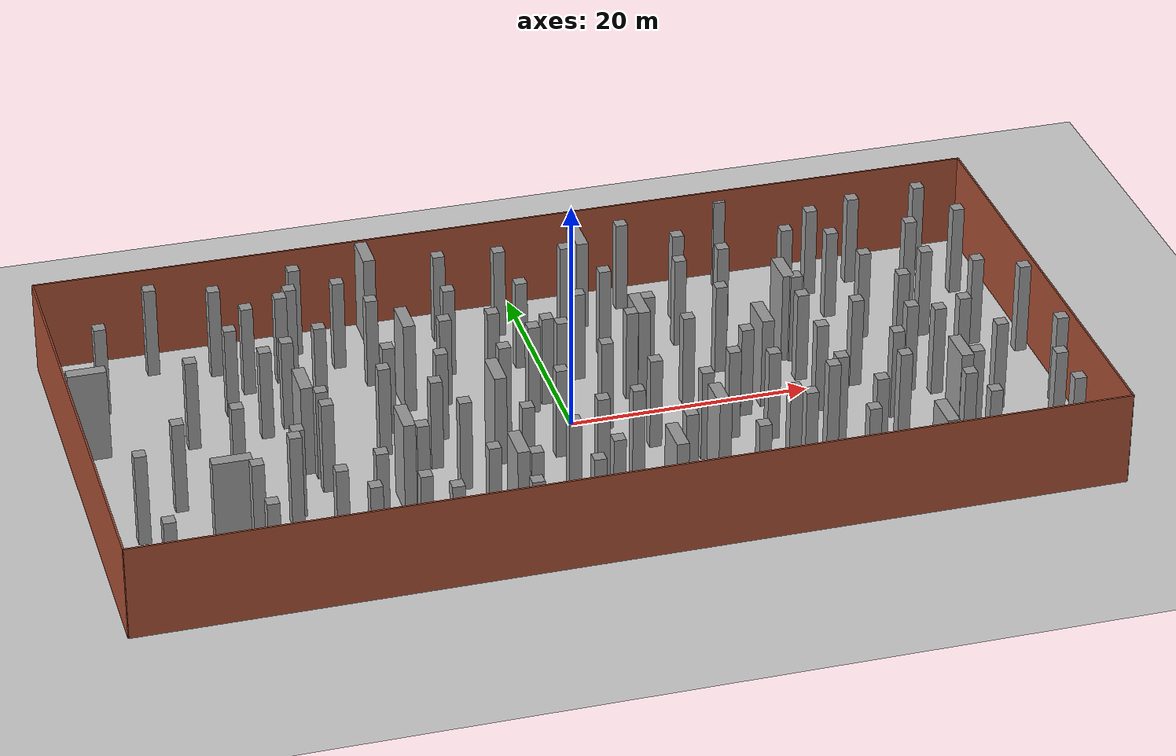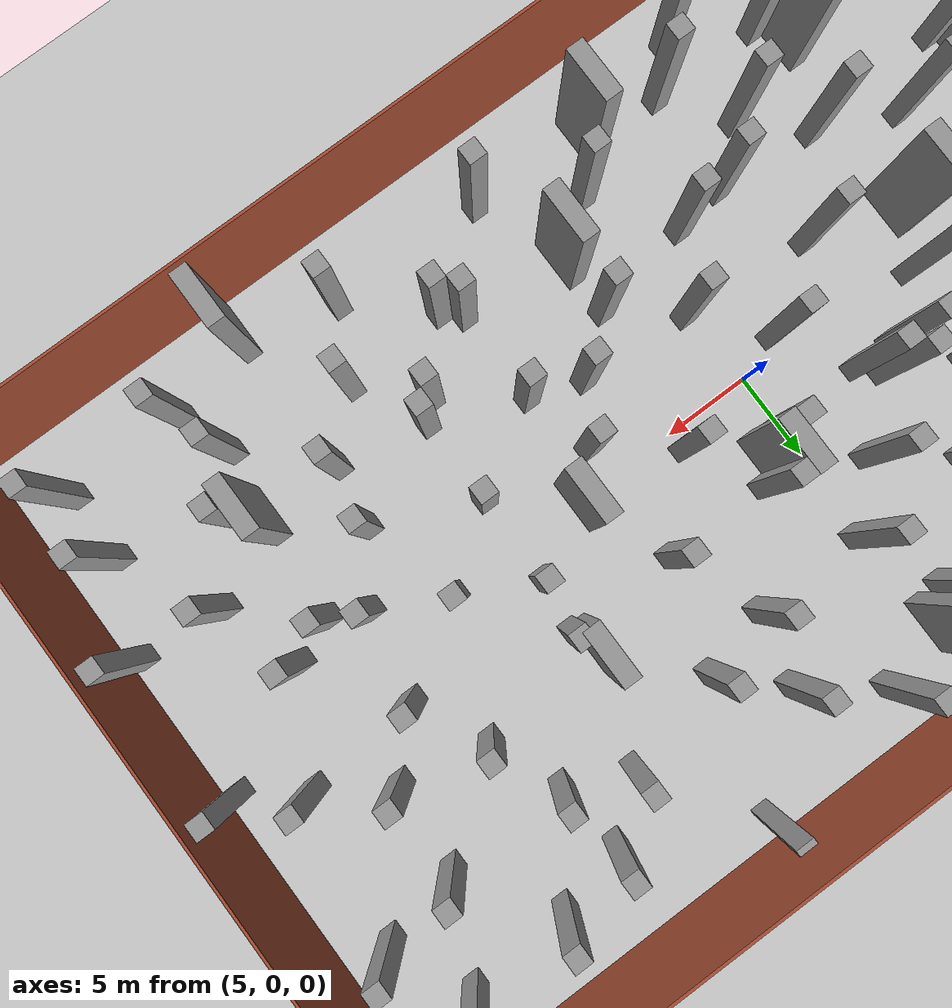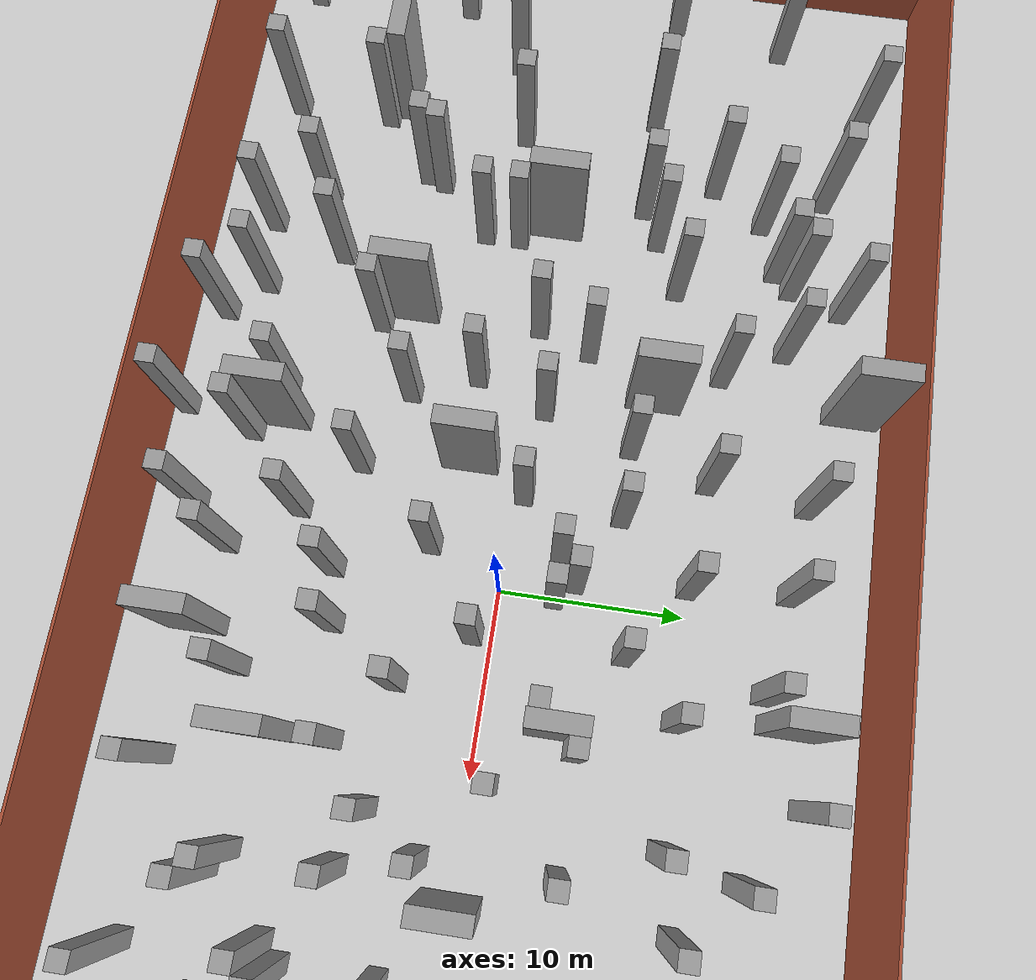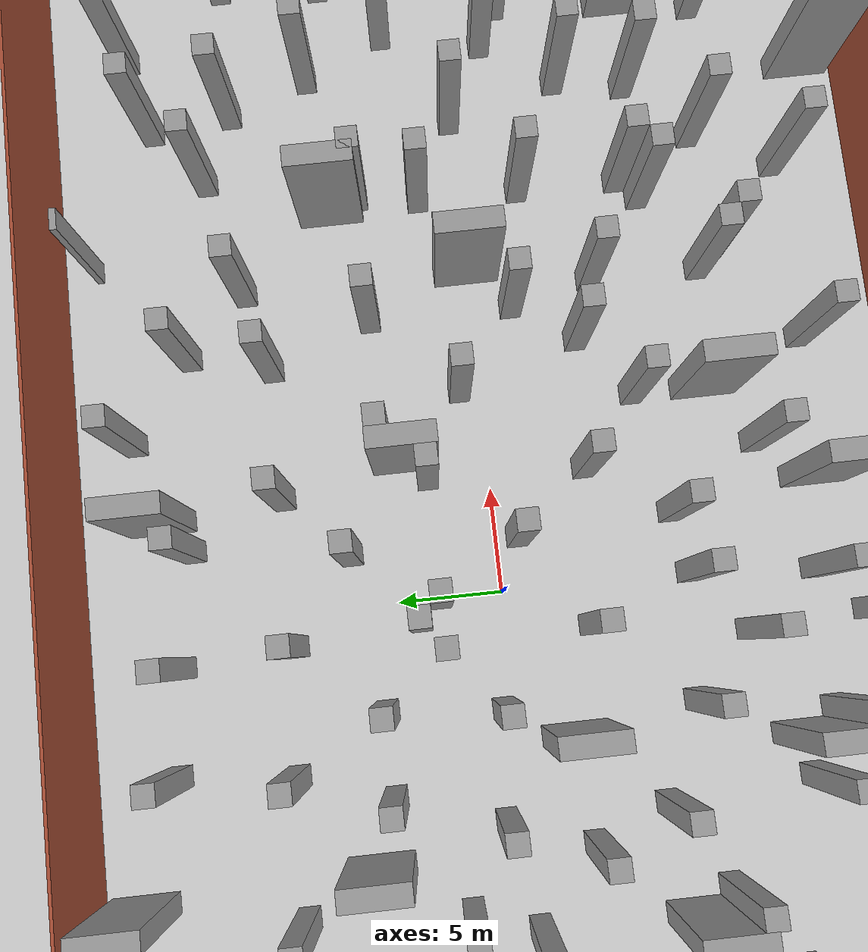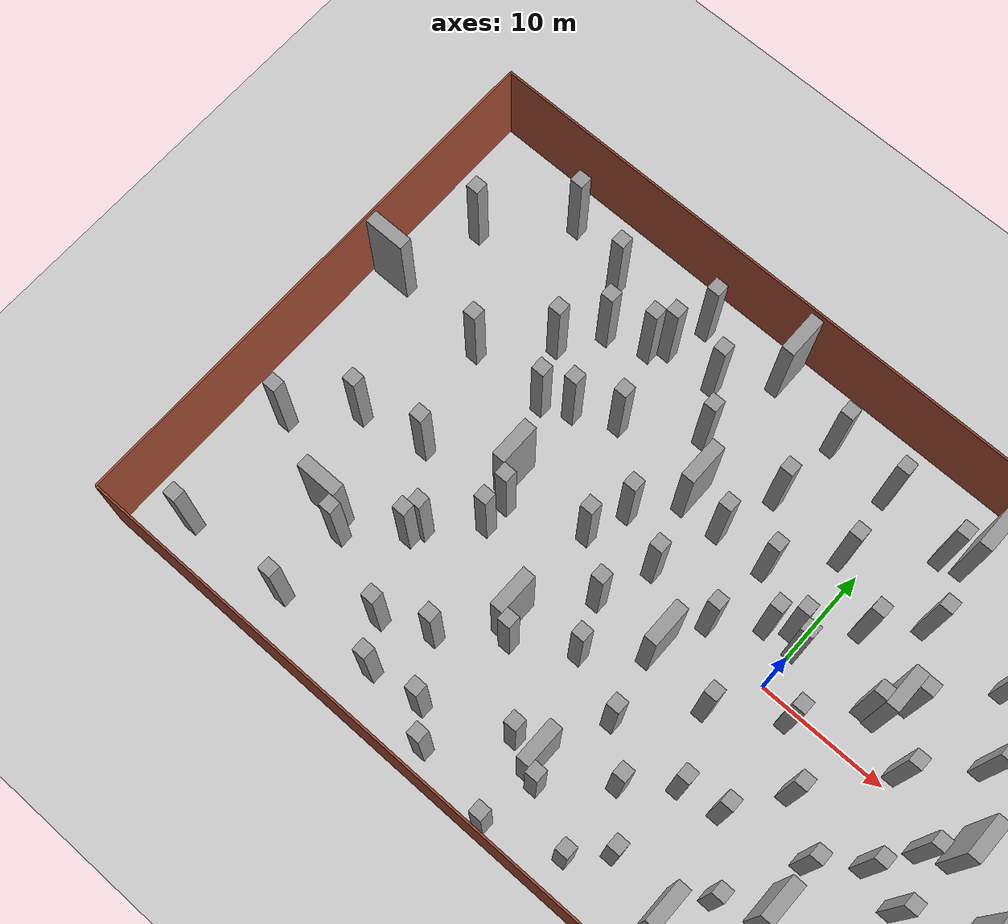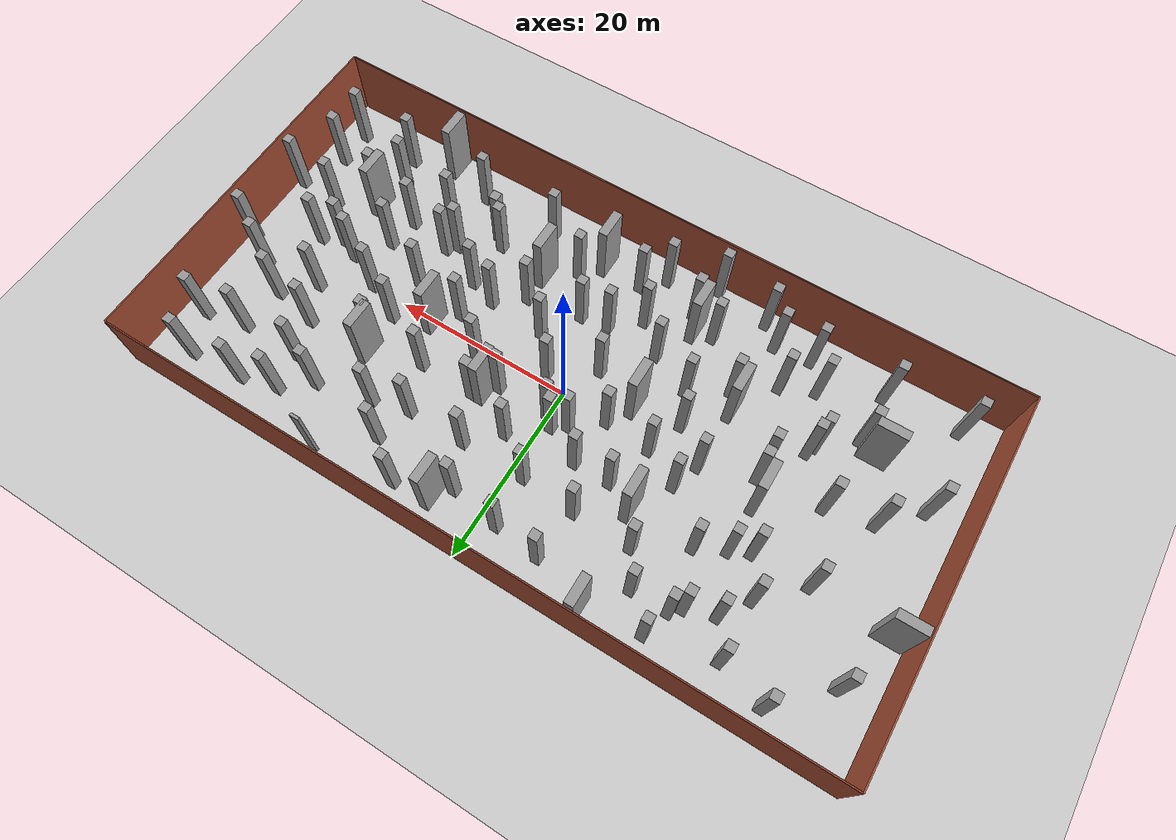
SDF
<sdf version="1.7">
 <world name="default">
  <light name="sun" type="directional">
   <pose>0 0 10 0 -0 0</pose>
   <diffuse>0.8 0.8 0.8 1</diffuse>
   <specular>0.2 0.2 0.2 1</specular>
   <attenuation>
    <range>1000</range>
    <constant>0.9</constant>
    <linear>0.01</linear>
    <quadratic>0.001</quadratic>
   </attenuation>
   <direction>-0.5 0.1 -0.9</direction>
   <spot><inner_angle>0</inner_angle><outer_angle>0</outer_angle><falloff>0</falloff></spot>
  </light>
  <model name="ground_plane">
   <static>1</static>
   <link name="link">
    <collision name="collision">
     <geometry><plane><normal>0 0 1</normal><size>100 100</size></plane></geometry>
     <surface>
      <contact><collide_bitmask>65535</collide_bitmask></contact>
      <friction><ode><mu>100</mu><mu2>50</mu2></ode></friction>
     </surface>
    </collision>
    <visual name="visual">
     <cast_shadows>0</cast_shadows>
     <geometry><plane><normal>0 0 1</normal><size>100 100</size></plane></geometry>
     <material>
      <script><uri>file://media/materials/scripts/gazebo.material</uri><name>Gazebo/Grey</name></script>
     </material>
    </visual>
   </link>
  </model>
  <gravity>0 0 -9.8</gravity>
  <magnetic_field>6e-06 2.3e-05 -4.2e-05</magnetic_field>
  <atmosphere type="adiabatic"/>
  <physics type="ode">
   <max_step_size>0.001</max_step_size>
   <real_time_factor>1</real_time_factor>
   <real_time_update_rate>1000</real_time_update_rate>
  </physics>
  <scene><ambient>0.4 0.4 0.4 1</ambient><background>0.7 0.7 0.7 1</background><shadows>1</shadows></scene>
  <spherical_coordinates>
   <surface_model>EARTH_WGS84</surface_model>
   <latitude_deg>0</latitude_deg>
   <longitude_deg>0</longitude_deg>
   <elevation>0</elevation>
   <heading_deg>0</heading_deg>
  </spherical_coordinates>
  <model name="sim_room_rect">
   <link name="Wall_14">
    <collision name="Wall_14_Collision">
     <geometry><box><size>40 0.15 8</size></box></geometry>
     <pose>0 0 4 0 -0 0</pose>
    </collision>
    <visual name="Wall_14_Visual">
     <pose>0 0 4 0 -0 0</pose>
     <geometry><box><size>40 0.15 8</size></box></geometry>
     <material>
      <script><uri>file://media/materials/scripts/gazebo.material</uri><name>Gazebo/Bricks</name></script>
      <ambient>1 1 1 1</ambient>
     </material>
     <meta><layer>0</layer></meta>
    </visual>
    <pose>40 -0 0 0 -0 -1.5708</pose>
   </link>
   <link name="Wall_15">
    <collision name="Wall_15_Collision">
     <geometry><box><size>80 0.15 8</size></box></geometry>
     <pose>0 0 4 0 -0 0</pose>
    </collision>
    <visual name="Wall_15_Visual">
     <pose>0 0 4 0 -0 0</pose>
     <geometry><box><size>80 0.15 8</size></box></geometry>
     <material>
      <script><uri>file://media/materials/scripts/gazebo.material</uri><name>Gazebo/Bricks</name></script>
      <ambient>1 1 1 1</ambient>
     </material>
     <meta><layer>0</layer></meta>
    </visual>
    <pose>0 -20 0 0 -0 3.14159</pose>
   </link>
   <link name="Wall_16">
    <collision name="Wall_16_Collision">
     <geometry><box><size>40 0.15 8</size></box></geometry>
     <pose>0 0 4 0 -0 0</pose>
    </collision>
    <visual name="Wall_16_Visual">
     <pose>0 0 4 0 -0 0</pose>
     <geometry><box><size>40 0.15 8</size></box></geometry>
     <material>
      <script><uri>file://media/materials/scripts/gazebo.material</uri><name>Gazebo/Bricks</name></script>
      <ambient>1 1 1 1</ambient>
     </material>
     <meta><layer>0</layer></meta>
    </visual>
    <pose>-40 -0 0 0 -0 1.5708</pose>
   </link>
   <link name="Wall_19">
    <collision name="Wall_19_Collision">
     <geometry><box><size>80 0.15 8</size></box></geometry>
     <pose>0 0 4 0 -0 0</pose>
    </collision>
    <visual name="Wall_19_Visual">
     <pose>0 0 4 0 -0 0</pose>
     <geometry><box><size>80 0.15 8</size></box></geometry>
     <material>
      <script><uri>file://media/materials/scripts/gazebo.material</uri><name>Gazebo/Bricks</name></script>
      <ambient>1 1 1 1</ambient>
     </material>
     <meta><layer>0</layer></meta>
    </visual>
    <pose>0 20 0 0 -0 0</pose>
   </link>
   <static>1</static>
  </model>
  <model name="unit_box_static_clone_1">
   <link name="link">
    <inertial>
     <mass>1</mass>
     <inertia>
      <ixx>0.166667</ixx>
      <ixy>0</ixy>
      <ixz>0</ixz>
      <iyy>0.166667</iyy>
      <iyz>0</iyz>
      <izz>0.166667</izz>
     </inertia>
    </inertial>
    <visual name="visual">
     <geometry><box><size>1 1 8.00001</size></box></geometry>
     <material>
      <script><name>Gazebo/Grey</name><uri>file://media/materials/scripts/gazebo.material</uri></script>
      <shader type="pixel"/>
     </material>
    </visual>
    <collision name="collision">
     <geometry><box><size>1 1 8.00001</size></box></geometry>
     <surface>
      <friction>
       <ode><mu>1</mu><mu2>1</mu2><fdir1>0 0 0</fdir1><slip1>0</slip1><slip2>0</slip2></ode>
       <torsional>
        <coefficient>1</coefficient>
        <patch_radius>0</patch_radius>
        <surface_radius>0</surface_radius>
        <use_patch_radius>1</use_patch_radius>
        <ode><slip>0</slip></ode>
       </torsional>
      </friction>
      <bounce><restitution_coefficient>0</restitution_coefficient><threshold>1e+06</threshold></bounce>
      <contact>
       <collide_without_contact>0</collide_without_contact>
       <collide_without_contact_bitmask>1</collide_without_contact_bitmask>
       <collide_bitmask>1</collide_bitmask>
       <ode>
        <soft_cfm>0</soft_cfm>
        <soft_erp>0.2</soft_erp>
        <kp>1e+13</kp>
        <kd>1</kd>
        <max_vel>0.01</max_vel>
        <min_depth>0</min_depth>
       </ode>
       <bullet>
        <split_impulse>1</split_impulse>
        <split_impulse_penetration_threshold>-0.01</split_impulse_penetration_threshold>
        <soft_cfm>0</soft_cfm>
        <soft_erp>0.2</soft_erp>
        <kp>1e+13</kp>
        <kd>1</kd>
       </bullet>
      </contact>
     </surface>
    </collision>
   </link>
   <static>1</static>
   <pose>-19 17 4 0 -0 0</pose>
  </model>
  <model name="unit_box_static_clone_3">
   <link name="link">
    <inertial>
     <mass>1</mass>
     <inertia>
      <ixx>0.166667</ixx>
      <ixy>0</ixy>
      <ixz>0</ixz>
      <iyy>0.166667</iyy>
      <iyz>0</iyz>
      <izz>0.166667</izz>
     </inertia>
    </inertial>
    <visual name="visual">
     <geometry><box><size>1 1 8.00001</size></box></geometry>
     <material>
      <script><name>Gazebo/Grey</name><uri>file://media/materials/scripts/gazebo.material</uri></script>
      <shader type="pixel"/>
     </material>
    </visual>
    <collision name="collision">
     <geometry><box><size>1 1 8.00001</size></box></geometry>
     <surface>
      <friction>
       <ode><mu>1</mu><mu2>1</mu2><fdir1>0 0 0</fdir1><slip1>0</slip1><slip2>0</slip2></ode>
       <torsional>
        <coefficient>1</coefficient>
        <patch_radius>0</patch_radius>
        <surface_radius>0</surface_radius>
        <use_patch_radius>1</use_patch_radius>
        <ode><slip>0</slip></ode>
       </torsional>
      </friction>
      <bounce><restitution_coefficient>0</restitution_coefficient><threshold>1e+06</threshold></bounce>
      <contact>
       <collide_without_contact>0</collide_without_contact>
       <collide_without_contact_bitmask>1</collide_without_contact_bitmask>
       <collide_bitmask>1</collide_bitmask>
       <ode>
        <soft_cfm>0</soft_cfm>
        <soft_erp>0.2</soft_erp>
        <kp>1e+13</kp>
        <kd>1</kd>
        <max_vel>0.01</max_vel>
        <min_depth>0</min_depth>
       </ode>
       <bullet>
        <split_impulse>1</split_impulse>
        <split_impulse_penetration_threshold>-0.01</split_impulse_penetration_threshold>
        <soft_cfm>0</soft_cfm>
        <soft_erp>0.2</soft_erp>
        <kp>1e+13</kp>
        <kd>1</kd>
       </bullet>
      </contact>
     </surface>
    </collision>
   </link>
   <static>1</static>
   <pose>-20 14 4 0 -0 0</pose>
  </model>
  <model name="unit_box_static_clone_4">
   <link name="link">
    <inertial>
     <mass>1</mass>
     <inertia>
      <ixx>0.166667</ixx>
      <ixy>0</ixy>
      <ixz>0</ixz>
      <iyy>0.166667</iyy>
      <iyz>0</iyz>
      <izz>0.166667</izz>
     </inertia>
    </inertial>
    <visual name="visual">
     <geometry><box><size>1 1 8.00001</size></box></geometry>
     <material>
      <script><name>Gazebo/Grey</name><uri>file://media/materials/scripts/gazebo.material</uri></script>
      <shader type="pixel"/>
     </material>
    </visual>
    <collision name="collision">
     <geometry><box><size>1 1 8.00001</size></box></geometry>
     <surface>
      <friction>
       <ode><mu>1</mu><mu2>1</mu2><fdir1>0 0 0</fdir1><slip1>0</slip1><slip2>0</slip2></ode>
       <torsional>
        <coefficient>1</coefficient>
        <patch_radius>0</patch_radius>
        <surface_radius>0</surface_radius>
        <use_patch_radius>1</use_patch_radius>
        <ode><slip>0</slip></ode>
       </torsional>
      </friction>
      <bounce><restitution_coefficient>0</restitution_coefficient><threshold>1e+06</threshold></bounce>
      <contact>
       <collide_without_contact>0</collide_without_contact>
       <collide_without_contact_bitmask>1</collide_without_contact_bitmask>
       <collide_bitmask>1</collide_bitmask>
       <ode>
        <soft_cfm>0</soft_cfm>
        <soft_erp>0.2</soft_erp>
        <kp>1e+13</kp>
        <kd>1</kd>
        <max_vel>0.01</max_vel>
        <min_depth>0</min_depth>
       </ode>
       <bullet>
        <split_impulse>1</split_impulse>
        <split_impulse_penetration_threshold>-0.01</split_impulse_penetration_threshold>
        <soft_cfm>0</soft_cfm>
        <soft_erp>0.2</soft_erp>
        <kp>1e+13</kp>
        <kd>1</kd>
       </bullet>
      </contact>
     </surface>
    </collision>
   </link>
   <static>1</static>
   <pose>-14 10.5646 4 0 -0 0</pose>
  </model>
  <model name="unit_box_static_clone_5">
   <link name="link">
    <inertial>
     <mass>1</mass>
     <inertia>
      <ixx>0.166667</ixx>
      <ixy>0</ixy>
      <ixz>0</ixz>
      <iyy>0.166667</iyy>
      <iyz>0</iyz>
      <izz>0.166667</izz>
     </inertia>
    </inertial>
    <visual name="visual">
     <geometry><box><size>1 1 8.00001</size></box></geometry>
     <material>
      <script><name>Gazebo/Grey</name><uri>file://media/materials/scripts/gazebo.material</uri></script>
      <shader type="pixel"/>
     </material>
    </visual>
    <collision name="collision">
     <geometry><box><size>1 1 8.00001</size></box></geometry>
     <surface>
      <friction>
       <ode><mu>1</mu><mu2>1</mu2><fdir1>0 0 0</fdir1><slip1>0</slip1><slip2>0</slip2></ode>
       <torsional>
        <coefficient>1</coefficient>
        <patch_radius>0</patch_radius>
        <surface_radius>0</surface_radius>
        <use_patch_radius>1</use_patch_radius>
        <ode><slip>0</slip></ode>
       </torsional>
      </friction>
      <bounce><restitution_coefficient>0</restitution_coefficient><threshold>1e+06</threshold></bounce>
      <contact>
       <collide_without_contact>0</collide_without_contact>
       <collide_without_contact_bitmask>1</collide_without_contact_bitmask>
       <collide_bitmask>1</collide_bitmask>
       <ode>
        <soft_cfm>0</soft_cfm>
        <soft_erp>0.2</soft_erp>
        <kp>1e+13</kp>
        <kd>1</kd>
        <max_vel>0.01</max_vel>
        <min_depth>0</min_depth>
       </ode>
       <bullet>
        <split_impulse>1</split_impulse>
        <split_impulse_penetration_threshold>-0.01</split_impulse_penetration_threshold>
        <soft_cfm>0</soft_cfm>
        <soft_erp>0.2</soft_erp>
        <kp>1e+13</kp>
        <kd>1</kd>
       </bullet>
      </contact>
     </surface>
    </collision>
   </link>
   <static>1</static>
   <pose>-7.56601 10.4516 4 0 -0 0</pose>
  </model>
  <model name="unit_box_static_clone_6">
   <link name="link">
    <inertial>
     <mass>1</mass>
     <inertia>
      <ixx>0.166667</ixx>
      <ixy>0</ixy>
      <ixz>0</ixz>
      <iyy>0.166667</iyy>
      <iyz>0</iyz>
      <izz>0.166667</izz>
     </inertia>
    </inertial>
    <visual name="visual">
     <geometry><box><size>1 1 8.00001</size></box></geometry>
     <material>
      <script><name>Gazebo/Grey</name><uri>file://media/materials/scripts/gazebo.material</uri></script>
      <shader type="pixel"/>
     </material>
    </visual>
    <collision name="collision">
     <geometry><box><size>1 1 8.00001</size></box></geometry>
     <surface>
      <friction>
       <ode><mu>1</mu><mu2>1</mu2><fdir1>0 0 0</fdir1><slip1>0</slip1><slip2>0</slip2></ode>
       <torsional>
        <coefficient>1</coefficient>
        <patch_radius>0</patch_radius>
        <surface_radius>0</surface_radius>
        <use_patch_radius>1</use_patch_radius>
        <ode><slip>0</slip></ode>
       </torsional>
      </friction>
      <bounce><restitution_coefficient>0</restitution_coefficient><threshold>1e+06</threshold></bounce>
      <contact>
       <collide_without_contact>0</collide_without_contact>
       <collide_without_contact_bitmask>1</collide_without_contact_bitmask>
       <collide_bitmask>1</collide_bitmask>
       <ode>
        <soft_cfm>0</soft_cfm>
        <soft_erp>0.2</soft_erp>
        <kp>1e+13</kp>
        <kd>1</kd>
        <max_vel>0.01</max_vel>
        <min_depth>0</min_depth>
       </ode>
       <bullet>
        <split_impulse>1</split_impulse>
        <split_impulse_penetration_threshold>-0.01</split_impulse_penetration_threshold>
        <soft_cfm>0</soft_cfm>
        <soft_erp>0.2</soft_erp>
        <kp>1e+13</kp>
        <kd>1</kd>
       </bullet>
      </contact>
     </surface>
    </collision>
   </link>
   <static>1</static>
   <pose>-5 6 4 0 -0 0</pose>
  </model>
  <model name="unit_box_static_clone_7">
   <link name="link">
    <inertial>
     <mass>1</mass>
     <inertia>
      <ixx>0.166667</ixx>
      <ixy>0</ixy>
      <ixz>0</ixz>
      <iyy>0.166667</iyy>
      <iyz>0</iyz>
      <izz>0.166667</izz>
     </inertia>
    </inertial>
    <visual name="visual">
     <geometry><box><size>1 1 8.00001</size></box></geometry>
     <material>
      <script><name>Gazebo/Grey</name><uri>file://media/materials/scripts/gazebo.material</uri></script>
      <shader type="pixel"/>
     </material>
    </visual>
    <collision name="collision">
     <geometry><box><size>1 1 8.00001</size></box></geometry>
     <surface>
      <friction>
       <ode><mu>1</mu><mu2>1</mu2><fdir1>0 0 0</fdir1><slip1>0</slip1><slip2>0</slip2></ode>
       <torsional>
        <coefficient>1</coefficient>
        <patch_radius>0</patch_radius>
        <surface_radius>0</surface_radius>
        <use_patch_radius>1</use_patch_radius>
        <ode><slip>0</slip></ode>
       </torsional>
      </friction>
      <bounce><restitution_coefficient>0</restitution_coefficient><threshold>1e+06</threshold></bounce>
      <contact>
       <collide_without_contact>0</collide_without_contact>
       <collide_without_contact_bitmask>1</collide_without_contact_bitmask>
       <collide_bitmask>1</collide_bitmask>
       <ode>
        <soft_cfm>0</soft_cfm>
        <soft_erp>0.2</soft_erp>
        <kp>1e+13</kp>
        <kd>1</kd>
        <max_vel>0.01</max_vel>
        <min_depth>0</min_depth>
       </ode>
       <bullet>
        <split_impulse>1</split_impulse>
        <split_impulse_penetration_threshold>-0.01</split_impulse_penetration_threshold>
        <soft_cfm>0</soft_cfm>
        <soft_erp>0.2</soft_erp>
        <kp>1e+13</kp>
        <kd>1</kd>
       </bullet>
      </contact>
     </surface>
    </collision>
   </link>
   <static>1</static>
   <pose>-9 6 4 0 -0 0</pose>
  </model>
  <model name="unit_box_static_clone_8">
   <link name="link">
    <inertial>
     <mass>1</mass>
     <inertia>
      <ixx>0.166667</ixx>
      <ixy>0</ixy>
      <ixz>0</ixz>
      <iyy>0.166667</iyy>
      <iyz>0</iyz>
      <izz>0.166667</izz>
     </inertia>
    </inertial>
    <visual name="visual">
     <geometry><box><size>1 1 8.00001</size></box></geometry>
     <material>
      <script><name>Gazebo/Grey</name><uri>file://media/materials/scripts/gazebo.material</uri></script>
      <shader type="pixel"/>
     </material>
    </visual>
    <collision name="collision">
     <geometry><box><size>1 1 8.00001</size></box></geometry>
     <surface>
      <friction>
       <ode><mu>1</mu><mu2>1</mu2><fdir1>0 0 0</fdir1><slip1>0</slip1><slip2>0</slip2></ode>
       <torsional>
        <coefficient>1</coefficient>
        <patch_radius>0</patch_radius>
        <surface_radius>0</surface_radius>
        <use_patch_radius>1</use_patch_radius>
        <ode><slip>0</slip></ode>
       </torsional>
      </friction>
      <bounce><restitution_coefficient>0</restitution_coefficient><threshold>1e+06</threshold></bounce>
      <contact>
       <collide_without_contact>0</collide_without_contact>
       <collide_without_contact_bitmask>1</collide_without_contact_bitmask>
       <collide_bitmask>1</collide_bitmask>
       <ode>
        <soft_cfm>0</soft_cfm>
        <soft_erp>0.2</soft_erp>
        <kp>1e+13</kp>
        <kd>1</kd>
        <max_vel>0.01</max_vel>
        <min_depth>0</min_depth>
       </ode>
       <bullet>
        <split_impulse>1</split_impulse>
        <split_impulse_penetration_threshold>-0.01</split_impulse_penetration_threshold>
        <soft_cfm>0</soft_cfm>
        <soft_erp>0.2</soft_erp>
        <kp>1e+13</kp>
        <kd>1</kd>
       </bullet>
      </contact>
     </surface>
    </collision>
   </link>
   <static>1</static>
   <pose>-19 7.4588 4 0 -0 0</pose>
  </model>
  <model name="unit_box_static_clone_9">
   <link name="link">
    <inertial>
     <mass>1</mass>
     <inertia>
      <ixx>0.166667</ixx>
      <ixy>0</ixy>
      <ixz>0</ixz>
      <iyy>0.166667</iyy>
      <iyz>0</iyz>
      <izz>0.166667</izz>
     </inertia>
    </inertial>
    <visual name="visual">
     <geometry><box><size>1 1 8.00001</size></box></geometry>
     <material>
      <script><name>Gazebo/Grey</name><uri>file://media/materials/scripts/gazebo.material</uri></script>
      <shader type="pixel"/>
     </material>
    </visual>
    <collision name="collision">
     <geometry><box><size>1 1 8.00001</size></box></geometry>
     <surface>
      <friction>
       <ode><mu>1</mu><mu2>1</mu2><fdir1>0 0 0</fdir1><slip1>0</slip1><slip2>0</slip2></ode>
       <torsional>
        <coefficient>1</coefficient>
        <patch_radius>0</patch_radius>
        <surface_radius>0</surface_radius>
        <use_patch_radius>1</use_patch_radius>
        <ode><slip>0</slip></ode>
       </torsional>
      </friction>
      <bounce><restitution_coefficient>0</restitution_coefficient><threshold>1e+06</threshold></bounce>
      <contact>
       <collide_without_contact>0</collide_without_contact>
       <collide_without_contact_bitmask>1</collide_without_contact_bitmask>
       <collide_bitmask>1</collide_bitmask>
       <ode>
        <soft_cfm>0</soft_cfm>
        <soft_erp>0.2</soft_erp>
        <kp>1e+13</kp>
        <kd>1</kd>
        <max_vel>0.01</max_vel>
        <min_depth>0</min_depth>
       </ode>
       <bullet>
        <split_impulse>1</split_impulse>
        <split_impulse_penetration_threshold>-0.01</split_impulse_penetration_threshold>
        <soft_cfm>0</soft_cfm>
        <soft_erp>0.2</soft_erp>
        <kp>1e+13</kp>
        <kd>1</kd>
       </bullet>
      </contact>
     </surface>
    </collision>
   </link>
   <static>1</static>
   <pose>-24 12 4 0 -0 0</pose>
  </model>
  <model name="unit_box_static_clone_10">
   <link name="link">
    <inertial>
     <mass>1</mass>
     <inertia>
      <ixx>0.166667</ixx>
      <ixy>0</ixy>
      <ixz>0</ixz>
      <iyy>0.166667</iyy>
      <iyz>0</iyz>
      <izz>0.166667</izz>
     </inertia>
    </inertial>
    <visual name="visual">
     <geometry><box><size>1 1 8.00001</size></box></geometry>
     <material>
      <script><name>Gazebo/Grey</name><uri>file://media/materials/scripts/gazebo.material</uri></script>
      <shader type="pixel"/>
     </material>
    </visual>
    <collision name="collision">
     <geometry><box><size>1 1 8.00001</size></box></geometry>
     <surface>
      <friction>
       <ode><mu>1</mu><mu2>1</mu2><fdir1>0 0 0</fdir1><slip1>0</slip1><slip2>0</slip2></ode>
       <torsional>
        <coefficient>1</coefficient>
        <patch_radius>0</patch_radius>
        <surface_radius>0</surface_radius>
        <use_patch_radius>1</use_patch_radius>
        <ode><slip>0</slip></ode>
       </torsional>
      </friction>
      <bounce><restitution_coefficient>0</restitution_coefficient><threshold>1e+06</threshold></bounce>
      <contact>
       <collide_without_contact>0</collide_without_contact>
       <collide_without_contact_bitmask>1</collide_without_contact_bitmask>
       <collide_bitmask>1</collide_bitmask>
       <ode>
        <soft_cfm>0</soft_cfm>
        <soft_erp>0.2</soft_erp>
        <kp>1e+13</kp>
        <kd>1</kd>
        <max_vel>0.01</max_vel>
        <min_depth>0</min_depth>
       </ode>
       <bullet>
        <split_impulse>1</split_impulse>
        <split_impulse_penetration_threshold>-0.01</split_impulse_penetration_threshold>
        <soft_cfm>0</soft_cfm>
        <soft_erp>0.2</soft_erp>
        <kp>1e+13</kp>
        <kd>1</kd>
       </bullet>
      </contact>
     </surface>
    </collision>
   </link>
   <static>1</static>
   <pose>-26 15.4497 4 0 -0 0</pose>
  </model>
  <model name="unit_box_static_clone_12">
   <link name="link">
    <inertial>
     <mass>1</mass>
     <inertia>
      <ixx>0.166667</ixx>
      <ixy>0</ixy>
      <ixz>0</ixz>
      <iyy>0.166667</iyy>
      <iyz>0</iyz>
      <izz>0.166667</izz>
     </inertia>
    </inertial>
    <visual name="visual">
     <geometry><box><size>1 1 8.00001</size></box></geometry>
     <material>
      <script><name>Gazebo/Grey</name><uri>file://media/materials/scripts/gazebo.material</uri></script>
      <shader type="pixel"/>
     </material>
    </visual>
    <collision name="collision">
     <geometry><box><size>1 1 8.00001</size></box></geometry>
     <surface>
      <friction>
       <ode><mu>1</mu><mu2>1</mu2><fdir1>0 0 0</fdir1><slip1>0</slip1><slip2>0</slip2></ode>
       <torsional>
        <coefficient>1</coefficient>
        <patch_radius>0</patch_radius>
        <surface_radius>0</surface_radius>
        <use_patch_radius>1</use_patch_radius>
        <ode><slip>0</slip></ode>
       </torsional>
      </friction>
      <bounce><restitution_coefficient>0</restitution_coefficient><threshold>1e+06</threshold></bounce>
      <contact>
       <collide_without_contact>0</collide_without_contact>
       <collide_without_contact_bitmask>1</collide_without_contact_bitmask>
       <collide_bitmask>1</collide_bitmask>
       <ode>
        <soft_cfm>0</soft_cfm>
        <soft_erp>0.2</soft_erp>
        <kp>1e+13</kp>
        <kd>1</kd>
        <max_vel>0.01</max_vel>
        <min_depth>0</min_depth>
       </ode>
       <bullet>
        <split_impulse>1</split_impulse>
        <split_impulse_penetration_threshold>-0.01</split_impulse_penetration_threshold>
        <soft_cfm>0</soft_cfm>
        <soft_erp>0.2</soft_erp>
        <kp>1e+13</kp>
        <kd>1</kd>
       </bullet>
      </contact>
     </surface>
    </collision>
   </link>
   <static>1</static>
   <pose>-14.4203 3 4 0 -0 0</pose>
  </model>
  <model name="unit_box_static_clone_13">
   <link name="link">
    <inertial>
     <mass>1</mass>
     <inertia>
      <ixx>0.166667</ixx>
      <ixy>0</ixy>
      <ixz>0</ixz>
      <iyy>0.166667</iyy>
      <iyz>0</iyz>
      <izz>0.166667</izz>
     </inertia>
    </inertial>
    <visual name="visual">
     <geometry><box><size>1 1 8.00001</size></box></geometry>
     <material>
      <script><name>Gazebo/Grey</name><uri>file://media/materials/scripts/gazebo.material</uri></script>
      <shader type="pixel"/>
     </material>
    </visual>
    <collision name="collision">
     <geometry><box><size>1 1 8.00001</size></box></geometry>
     <surface>
      <friction>
       <ode><mu>1</mu><mu2>1</mu2><fdir1>0 0 0</fdir1><slip1>0</slip1><slip2>0</slip2></ode>
       <torsional>
        <coefficient>1</coefficient>
        <patch_radius>0</patch_radius>
        <surface_radius>0</surface_radius>
        <use_patch_radius>1</use_patch_radius>
        <ode><slip>0</slip></ode>
       </torsional>
      </friction>
      <bounce><restitution_coefficient>0</restitution_coefficient><threshold>1e+06</threshold></bounce>
      <contact>
       <collide_without_contact>0</collide_without_contact>
       <collide_without_contact_bitmask>1</collide_without_contact_bitmask>
       <collide_bitmask>1</collide_bitmask>
       <ode>
        <soft_cfm>0</soft_cfm>
        <soft_erp>0.2</soft_erp>
        <kp>1e+13</kp>
        <kd>1</kd>
        <max_vel>0.01</max_vel>
        <min_depth>0</min_depth>
       </ode>
       <bullet>
        <split_impulse>1</split_impulse>
        <split_impulse_penetration_threshold>-0.01</split_impulse_penetration_threshold>
        <soft_cfm>0</soft_cfm>
        <soft_erp>0.2</soft_erp>
        <kp>1e+13</kp>
        <kd>1</kd>
       </bullet>
      </contact>
     </surface>
    </collision>
   </link>
   <static>1</static>
   <pose>-15.4873 0 4 0 -0 0</pose>
  </model>
  <model name="unit_box_static_clone_15">
   <link name="link">
    <inertial>
     <mass>1</mass>
     <inertia>
      <ixx>0.166667</ixx>
      <ixy>0</ixy>
      <ixz>0</ixz>
      <iyy>0.166667</iyy>
      <iyz>0</iyz>
      <izz>0.166667</izz>
     </inertia>
    </inertial>
    <visual name="visual">
     <geometry><box><size>1 1 8.00001</size></box></geometry>
     <material>
      <script><name>Gazebo/Grey</name><uri>file://media/materials/scripts/gazebo.material</uri></script>
      <shader type="pixel"/>
     </material>
    </visual>
    <collision name="collision">
     <geometry><box><size>1 1 8.00001</size></box></geometry>
     <surface>
      <friction>
       <ode><mu>1</mu><mu2>1</mu2><fdir1>0 0 0</fdir1><slip1>0</slip1><slip2>0</slip2></ode>
       <torsional>
        <coefficient>1</coefficient>
        <patch_radius>0</patch_radius>
        <surface_radius>0</surface_radius>
        <use_patch_radius>1</use_patch_radius>
        <ode><slip>0</slip></ode>
       </torsional>
      </friction>
      <bounce><restitution_coefficient>0</restitution_coefficient><threshold>1e+06</threshold></bounce>
      <contact>
       <collide_without_contact>0</collide_without_contact>
       <collide_without_contact_bitmask>1</collide_without_contact_bitmask>
       <collide_bitmask>1</collide_bitmask>
       <ode>
        <soft_cfm>0</soft_cfm>
        <soft_erp>0.2</soft_erp>
        <kp>1e+13</kp>
        <kd>1</kd>
        <max_vel>0.01</max_vel>
        <min_depth>0</min_depth>
       </ode>
       <bullet>
        <split_impulse>1</split_impulse>
        <split_impulse_penetration_threshold>-0.01</split_impulse_penetration_threshold>
        <soft_cfm>0</soft_cfm>
        <soft_erp>0.2</soft_erp>
        <kp>1e+13</kp>
        <kd>1</kd>
       </bullet>
      </contact>
     </surface>
    </collision>
   </link>
   <static>1</static>
   <pose>-14.5511 -9 4 0 -0 0</pose>
  </model>
  <model name="unit_box_static_clone_16">
   <link name="link">
    <inertial>
     <mass>1</mass>
     <inertia>
      <ixx>0.166667</ixx>
      <ixy>0</ixy>
      <ixz>0</ixz>
      <iyy>0.166667</iyy>
      <iyz>0</iyz>
      <izz>0.166667</izz>
     </inertia>
    </inertial>
    <visual name="visual">
     <geometry><box><size>1 1 8.00001</size></box></geometry>
     <material>
      <script><name>Gazebo/Grey</name><uri>file://media/materials/scripts/gazebo.material</uri></script>
      <shader type="pixel"/>
     </material>
    </visual>
    <collision name="collision">
     <geometry><box><size>1 1 8.00001</size></box></geometry>
     <surface>
      <friction>
       <ode><mu>1</mu><mu2>1</mu2><fdir1>0 0 0</fdir1><slip1>0</slip1><slip2>0</slip2></ode>
       <torsional>
        <coefficient>1</coefficient>
        <patch_radius>0</patch_radius>
        <surface_radius>0</surface_radius>
        <use_patch_radius>1</use_patch_radius>
        <ode><slip>0</slip></ode>
       </torsional>
      </friction>
      <bounce><restitution_coefficient>0</restitution_coefficient><threshold>1e+06</threshold></bounce>
      <contact>
       <collide_without_contact>0</collide_without_contact>
       <collide_without_contact_bitmask>1</collide_without_contact_bitmask>
       <collide_bitmask>1</collide_bitmask>
       <ode>
        <soft_cfm>0</soft_cfm>
        <soft_erp>0.2</soft_erp>
        <kp>1e+13</kp>
        <kd>1</kd>
        <max_vel>0.01</max_vel>
        <min_depth>0</min_depth>
       </ode>
       <bullet>
        <split_impulse>1</split_impulse>
        <split_impulse_penetration_threshold>-0.01</split_impulse_penetration_threshold>
        <soft_cfm>0</soft_cfm>
        <soft_erp>0.2</soft_erp>
        <kp>1e+13</kp>
        <kd>1</kd>
       </bullet>
      </contact>
     </surface>
    </collision>
   </link>
   <static>1</static>
   <pose>-10.537 -6.5798 4 0 -0 0</pose>
  </model>
  <model name="unit_box_static_clone_17">
   <link name="link">
    <inertial>
     <mass>1</mass>
     <inertia>
      <ixx>0.166667</ixx>
      <ixy>0</ixy>
      <ixz>0</ixz>
      <iyy>0.166667</iyy>
      <iyz>0</iyz>
      <izz>0.166667</izz>
     </inertia>
    </inertial>
    <visual name="visual">
     <geometry><box><size>1 1 8.00001</size></box></geometry>
     <material>
      <script><name>Gazebo/Grey</name><uri>file://media/materials/scripts/gazebo.material</uri></script>
      <shader type="pixel"/>
     </material>
    </visual>
    <collision name="collision">
     <geometry><box><size>1 1 8.00001</size></box></geometry>
     <surface>
      <friction>
       <ode><mu>1</mu><mu2>1</mu2><fdir1>0 0 0</fdir1><slip1>0</slip1><slip2>0</slip2></ode>
       <torsional>
        <coefficient>1</coefficient>
        <patch_radius>0</patch_radius>
        <surface_radius>0</surface_radius>
        <use_patch_radius>1</use_patch_radius>
        <ode><slip>0</slip></ode>
       </torsional>
      </friction>
      <bounce><restitution_coefficient>0</restitution_coefficient><threshold>1e+06</threshold></bounce>
      <contact>
       <collide_without_contact>0</collide_without_contact>
       <collide_without_contact_bitmask>1</collide_without_contact_bitmask>
       <collide_bitmask>1</collide_bitmask>
       <ode>
        <soft_cfm>0</soft_cfm>
        <soft_erp>0.2</soft_erp>
        <kp>1e+13</kp>
        <kd>1</kd>
        <max_vel>0.01</max_vel>
        <min_depth>0</min_depth>
       </ode>
       <bullet>
        <split_impulse>1</split_impulse>
        <split_impulse_penetration_threshold>-0.01</split_impulse_penetration_threshold>
        <soft_cfm>0</soft_cfm>
        <soft_erp>0.2</soft_erp>
        <kp>1e+13</kp>
        <kd>1</kd>
       </bullet>
      </contact>
     </surface>
    </collision>
   </link>
   <static>1</static>
   <pose>-10.5542 1 4 0 -0 0</pose>
  </model>
  <model name="unit_box_static_clone_18">
   <link name="link">
    <inertial>
     <mass>1</mass>
     <inertia>
      <ixx>0.166667</ixx>
      <ixy>0</ixy>
      <ixz>0</ixz>
      <iyy>0.166667</iyy>
      <iyz>0</iyz>
      <izz>0.166667</izz>
     </inertia>
    </inertial>
    <visual name="visual">
     <geometry><box><size>1 1 8.00001</size></box></geometry>
     <material>
      <script><name>Gazebo/Grey</name><uri>file://media/materials/scripts/gazebo.material</uri></script>
      <shader type="pixel"/>
     </material>
    </visual>
    <collision name="collision">
     <geometry><box><size>1 1 8.00001</size></box></geometry>
     <surface>
      <friction>
       <ode><mu>1</mu><mu2>1</mu2><fdir1>0 0 0</fdir1><slip1>0</slip1><slip2>0</slip2></ode>
       <torsional>
        <coefficient>1</coefficient>
        <patch_radius>0</patch_radius>
        <surface_radius>0</surface_radius>
        <use_patch_radius>1</use_patch_radius>
        <ode><slip>0</slip></ode>
       </torsional>
      </friction>
      <bounce><restitution_coefficient>0</restitution_coefficient><threshold>1e+06</threshold></bounce>
      <contact>
       <collide_without_contact>0</collide_without_contact>
       <collide_without_contact_bitmask>1</collide_without_contact_bitmask>
       <collide_bitmask>1</collide_bitmask>
       <ode>
        <soft_cfm>0</soft_cfm>
        <soft_erp>0.2</soft_erp>
        <kp>1e+13</kp>
        <kd>1</kd>
        <max_vel>0.01</max_vel>
        <min_depth>0</min_depth>
       </ode>
       <bullet>
        <split_impulse>1</split_impulse>
        <split_impulse_penetration_threshold>-0.01</split_impulse_penetration_threshold>
        <soft_cfm>0</soft_cfm>
        <soft_erp>0.2</soft_erp>
        <kp>1e+13</kp>
        <kd>1</kd>
       </bullet>
      </contact>
     </surface>
    </collision>
   </link>
   <static>1</static>
   <pose>-7 16 4 0 -0 0</pose>
  </model>
  <model name="unit_box_static_clone_19">
   <link name="link">
    <inertial>
     <mass>1</mass>
     <inertia>
      <ixx>0.166667</ixx>
      <ixy>0</ixy>
      <ixz>0</ixz>
      <iyy>0.166667</iyy>
      <iyz>0</iyz>
      <izz>0.166667</izz>
     </inertia>
    </inertial>
    <visual name="visual">
     <geometry><box><size>1 1 8.00001</size></box></geometry>
     <material>
      <script><name>Gazebo/Grey</name><uri>file://media/materials/scripts/gazebo.material</uri></script>
      <shader type="pixel"/>
     </material>
    </visual>
    <collision name="collision">
     <geometry><box><size>1 1 8.00001</size></box></geometry>
     <surface>
      <friction>
       <ode><mu>1</mu><mu2>1</mu2><fdir1>0 0 0</fdir1><slip1>0</slip1><slip2>0</slip2></ode>
       <torsional>
        <coefficient>1</coefficient>
        <patch_radius>0</patch_radius>
        <surface_radius>0</surface_radius>
        <use_patch_radius>1</use_patch_radius>
        <ode><slip>0</slip></ode>
       </torsional>
      </friction>
      <bounce><restitution_coefficient>0</restitution_coefficient><threshold>1e+06</threshold></bounce>
      <contact>
       <collide_without_contact>0</collide_without_contact>
       <collide_without_contact_bitmask>1</collide_without_contact_bitmask>
       <collide_bitmask>1</collide_bitmask>
       <ode>
        <soft_cfm>0</soft_cfm>
        <soft_erp>0.2</soft_erp>
        <kp>1e+13</kp>
        <kd>1</kd>
        <max_vel>0.01</max_vel>
        <min_depth>0</min_depth>
       </ode>
       <bullet>
        <split_impulse>1</split_impulse>
        <split_impulse_penetration_threshold>-0.01</split_impulse_penetration_threshold>
        <soft_cfm>0</soft_cfm>
        <soft_erp>0.2</soft_erp>
        <kp>1e+13</kp>
        <kd>1</kd>
       </bullet>
      </contact>
     </surface>
    </collision>
   </link>
   <static>1</static>
   <pose>-2 15.4448 4 0 -0 0</pose>
  </model>
  <model name="unit_box_static_clone_20">
   <link name="link">
    <inertial>
     <mass>1</mass>
     <inertia>
      <ixx>0.166667</ixx>
      <ixy>0</ixy>
      <ixz>0</ixz>
      <iyy>0.166667</iyy>
      <iyz>0</iyz>
      <izz>0.166667</izz>
     </inertia>
    </inertial>
    <visual name="visual">
     <geometry><box><size>1 1 8.00001</size></box></geometry>
     <material>
      <script><name>Gazebo/Grey</name><uri>file://media/materials/scripts/gazebo.material</uri></script>
      <shader type="pixel"/>
     </material>
    </visual>
    <collision name="collision">
     <geometry><box><size>1 1 8.00001</size></box></geometry>
     <surface>
      <friction>
       <ode><mu>1</mu><mu2>1</mu2><fdir1>0 0 0</fdir1><slip1>0</slip1><slip2>0</slip2></ode>
       <torsional>
        <coefficient>1</coefficient>
        <patch_radius>0</patch_radius>
        <surface_radius>0</surface_radius>
        <use_patch_radius>1</use_patch_radius>
        <ode><slip>0</slip></ode>
       </torsional>
      </friction>
      <bounce><restitution_coefficient>0</restitution_coefficient><threshold>1e+06</threshold></bounce>
      <contact>
       <collide_without_contact>0</collide_without_contact>
       <collide_without_contact_bitmask>1</collide_without_contact_bitmask>
       <collide_bitmask>1</collide_bitmask>
       <ode>
        <soft_cfm>0</soft_cfm>
        <soft_erp>0.2</soft_erp>
        <kp>1e+13</kp>
        <kd>1</kd>
        <max_vel>0.01</max_vel>
        <min_depth>0</min_depth>
       </ode>
       <bullet>
        <split_impulse>1</split_impulse>
        <split_impulse_penetration_threshold>-0.01</split_impulse_penetration_threshold>
        <soft_cfm>0</soft_cfm>
        <soft_erp>0.2</soft_erp>
        <kp>1e+13</kp>
        <kd>1</kd>
       </bullet>
      </contact>
     </surface>
    </collision>
   </link>
   <static>1</static>
   <pose>3.47476 14.545 4 0 -0 0</pose>
  </model>
  <model name="unit_box_static_clone_21">
   <link name="link">
    <inertial>
     <mass>1</mass>
     <inertia>
      <ixx>0.166667</ixx>
      <ixy>0</ixy>
      <ixz>0</ixz>
      <iyy>0.166667</iyy>
      <iyz>0</iyz>
      <izz>0.166667</izz>
     </inertia>
    </inertial>
    <visual name="visual">
     <geometry><box><size>1 1 8.00001</size></box></geometry>
     <material>
      <script><name>Gazebo/Grey</name><uri>file://media/materials/scripts/gazebo.material</uri></script>
      <shader type="pixel"/>
     </material>
    </visual>
    <collision name="collision">
     <geometry><box><size>1 1 8.00001</size></box></geometry>
     <surface>
      <friction>
       <ode><mu>1</mu><mu2>1</mu2><fdir1>0 0 0</fdir1><slip1>0</slip1><slip2>0</slip2></ode>
       <torsional>
        <coefficient>1</coefficient>
        <patch_radius>0</patch_radius>
        <surface_radius>0</surface_radius>
        <use_patch_radius>1</use_patch_radius>
        <ode><slip>0</slip></ode>
       </torsional>
      </friction>
      <bounce><restitution_coefficient>0</restitution_coefficient><threshold>1e+06</threshold></bounce>
      <contact>
       <collide_without_contact>0</collide_without_contact>
       <collide_without_contact_bitmask>1</collide_without_contact_bitmask>
       <collide_bitmask>1</collide_bitmask>
       <ode>
        <soft_cfm>0</soft_cfm>
        <soft_erp>0.2</soft_erp>
        <kp>1e+13</kp>
        <kd>1</kd>
        <max_vel>0.01</max_vel>
        <min_depth>0</min_depth>
       </ode>
       <bullet>
        <split_impulse>1</split_impulse>
        <split_impulse_penetration_threshold>-0.01</split_impulse_penetration_threshold>
        <soft_cfm>0</soft_cfm>
        <soft_erp>0.2</soft_erp>
        <kp>1e+13</kp>
        <kd>1</kd>
       </bullet>
      </contact>
     </surface>
    </collision>
   </link>
   <static>1</static>
   <pose>13 14 4 0 -0 0</pose>
  </model>
  <model name="unit_box_static_clone_22">
   <link name="link">
    <inertial>
     <mass>1</mass>
     <inertia>
      <ixx>0.166667</ixx>
      <ixy>0</ixy>
      <ixz>0</ixz>
      <iyy>0.166667</iyy>
      <iyz>0</iyz>
      <izz>0.166667</izz>
     </inertia>
    </inertial>
    <visual name="visual">
     <geometry><box><size>1 1 8.00001</size></box></geometry>
     <material>
      <script><name>Gazebo/Grey</name><uri>file://media/materials/scripts/gazebo.material</uri></script>
      <shader type="pixel"/>
     </material>
    </visual>
    <collision name="collision">
     <geometry><box><size>1 1 8.00001</size></box></geometry>
     <surface>
      <friction>
       <ode><mu>1</mu><mu2>1</mu2><fdir1>0 0 0</fdir1><slip1>0</slip1><slip2>0</slip2></ode>
       <torsional>
        <coefficient>1</coefficient>
        <patch_radius>0</patch_radius>
        <surface_radius>0</surface_radius>
        <use_patch_radius>1</use_patch_radius>
        <ode><slip>0</slip></ode>
       </torsional>
      </friction>
      <bounce><restitution_coefficient>0</restitution_coefficient><threshold>1e+06</threshold></bounce>
      <contact>
       <collide_without_contact>0</collide_without_contact>
       <collide_without_contact_bitmask>1</collide_without_contact_bitmask>
       <collide_bitmask>1</collide_bitmask>
       <ode>
        <soft_cfm>0</soft_cfm>
        <soft_erp>0.2</soft_erp>
        <kp>1e+13</kp>
        <kd>1</kd>
        <max_vel>0.01</max_vel>
        <min_depth>0</min_depth>
       </ode>
       <bullet>
        <split_impulse>1</split_impulse>
        <split_impulse_penetration_threshold>-0.01</split_impulse_penetration_threshold>
        <soft_cfm>0</soft_cfm>
        <soft_erp>0.2</soft_erp>
        <kp>1e+13</kp>
        <kd>1</kd>
       </bullet>
      </contact>
     </surface>
    </collision>
   </link>
   <static>1</static>
   <pose>7.81147 5.05751 4 0 -0 0</pose>
  </model>
  <model name="unit_box_static_clone_24">
   <link name="link">
    <inertial>
     <mass>1</mass>
     <inertia>
      <ixx>0.166667</ixx>
      <ixy>0</ixy>
      <ixz>0</ixz>
      <iyy>0.166667</iyy>
      <iyz>0</iyz>
      <izz>0.166667</izz>
     </inertia>
    </inertial>
    <visual name="visual">
     <geometry><box><size>1 1 8.00001</size></box></geometry>
     <material>
      <script><name>Gazebo/Grey</name><uri>file://media/materials/scripts/gazebo.material</uri></script>
      <shader type="pixel"/>
     </material>
    </visual>
    <collision name="collision">
     <geometry><box><size>1 1 8.00001</size></box></geometry>
     <surface>
      <friction>
       <ode><mu>1</mu><mu2>1</mu2><fdir1>0 0 0</fdir1><slip1>0</slip1><slip2>0</slip2></ode>
       <torsional>
        <coefficient>1</coefficient>
        <patch_radius>0</patch_radius>
        <surface_radius>0</surface_radius>
        <use_patch_radius>1</use_patch_radius>
        <ode><slip>0</slip></ode>
       </torsional>
      </friction>
      <bounce><restitution_coefficient>0</restitution_coefficient><threshold>1e+06</threshold></bounce>
      <contact>
       <collide_without_contact>0</collide_without_contact>
       <collide_without_contact_bitmask>1</collide_without_contact_bitmask>
       <collide_bitmask>1</collide_bitmask>
       <ode>
        <soft_cfm>0</soft_cfm>
        <soft_erp>0.2</soft_erp>
        <kp>1e+13</kp>
        <kd>1</kd>
        <max_vel>0.01</max_vel>
        <min_depth>0</min_depth>
       </ode>
       <bullet>
        <split_impulse>1</split_impulse>
        <split_impulse_penetration_threshold>-0.01</split_impulse_penetration_threshold>
        <soft_cfm>0</soft_cfm>
        <soft_erp>0.2</soft_erp>
        <kp>1e+13</kp>
        <kd>1</kd>
       </bullet>
      </contact>
     </surface>
    </collision>
   </link>
   <static>1</static>
   <pose>2.50825 7 4 0 -0 0</pose>
  </model>
  <model name="unit_box_static_clone_25">
   <link name="link">
    <inertial>
     <mass>1</mass>
     <inertia>
      <ixx>0.166667</ixx>
      <ixy>0</ixy>
      <ixz>0</ixz>
      <iyy>0.166667</iyy>
      <iyz>0</iyz>
      <izz>0.166667</izz>
     </inertia>
    </inertial>
    <visual name="visual">
     <geometry><box><size>1 1 8.00001</size></box></geometry>
     <material>
      <script><name>Gazebo/Grey</name><uri>file://media/materials/scripts/gazebo.material</uri></script>
      <shader type="pixel"/>
     </material>
    </visual>
    <collision name="collision">
     <geometry><box><size>1 1 8.00001</size></box></geometry>
     <surface>
      <friction>
       <ode><mu>1</mu><mu2>1</mu2><fdir1>0 0 0</fdir1><slip1>0</slip1><slip2>0</slip2></ode>
       <torsional>
        <coefficient>1</coefficient>
        <patch_radius>0</patch_radius>
        <surface_radius>0</surface_radius>
        <use_patch_radius>1</use_patch_radius>
        <ode><slip>0</slip></ode>
       </torsional>
      </friction>
      <bounce><restitution_coefficient>0</restitution_coefficient><threshold>1e+06</threshold></bounce>
      <contact>
       <collide_without_contact>0</collide_without_contact>
       <collide_without_contact_bitmask>1</collide_without_contact_bitmask>
       <collide_bitmask>1</collide_bitmask>
       <ode>
        <soft_cfm>0</soft_cfm>
        <soft_erp>0.2</soft_erp>
        <kp>1e+13</kp>
        <kd>1</kd>
        <max_vel>0.01</max_vel>
        <min_depth>0</min_depth>
       </ode>
       <bullet>
        <split_impulse>1</split_impulse>
        <split_impulse_penetration_threshold>-0.01</split_impulse_penetration_threshold>
        <soft_cfm>0</soft_cfm>
        <soft_erp>0.2</soft_erp>
        <kp>1e+13</kp>
        <kd>1</kd>
       </bullet>
      </contact>
     </surface>
    </collision>
   </link>
   <static>1</static>
   <pose>-1.57746 10 4 0 -0 0</pose>
  </model>
  <model name="unit_box_static_clone_26">
   <link name="link">
    <inertial>
     <mass>1</mass>
     <inertia>
      <ixx>0.166667</ixx>
      <ixy>0</ixy>
      <ixz>0</ixz>
      <iyy>0.166667</iyy>
      <iyz>0</iyz>
      <izz>0.166667</izz>
     </inertia>
    </inertial>
    <visual name="visual">
     <geometry><box><size>1 1 8.00001</size></box></geometry>
     <material>
      <script><name>Gazebo/Grey</name><uri>file://media/materials/scripts/gazebo.material</uri></script>
      <shader type="pixel"/>
     </material>
    </visual>
    <collision name="collision">
     <geometry><box><size>1 1 8.00001</size></box></geometry>
     <surface>
      <friction>
       <ode><mu>1</mu><mu2>1</mu2><fdir1>0 0 0</fdir1><slip1>0</slip1><slip2>0</slip2></ode>
       <torsional>
        <coefficient>1</coefficient>
        <patch_radius>0</patch_radius>
        <surface_radius>0</surface_radius>
        <use_patch_radius>1</use_patch_radius>
        <ode><slip>0</slip></ode>
       </torsional>
      </friction>
      <bounce><restitution_coefficient>0</restitution_coefficient><threshold>1e+06</threshold></bounce>
      <contact>
       <collide_without_contact>0</collide_without_contact>
       <collide_without_contact_bitmask>1</collide_without_contact_bitmask>
       <collide_bitmask>1</collide_bitmask>
       <ode>
        <soft_cfm>0</soft_cfm>
        <soft_erp>0.2</soft_erp>
        <kp>1e+13</kp>
        <kd>1</kd>
        <max_vel>0.01</max_vel>
        <min_depth>0</min_depth>
       </ode>
       <bullet>
        <split_impulse>1</split_impulse>
        <split_impulse_penetration_threshold>-0.01</split_impulse_penetration_threshold>
        <soft_cfm>0</soft_cfm>
        <soft_erp>0.2</soft_erp>
        <kp>1e+13</kp>
        <kd>1</kd>
       </bullet>
      </contact>
     </surface>
    </collision>
   </link>
   <static>1</static>
   <pose>-10 -13.5446 4 0 -0 0</pose>
  </model>
  <model name="unit_box_static_clone_27">
   <link name="link">
    <inertial>
     <mass>1</mass>
     <inertia>
      <ixx>0.166667</ixx>
      <ixy>0</ixy>
      <ixz>0</ixz>
      <iyy>0.166667</iyy>
      <iyz>0</iyz>
      <izz>0.166667</izz>
     </inertia>
    </inertial>
    <visual name="visual">
     <geometry><box><size>1 1 8.00001</size></box></geometry>
     <material>
      <script><name>Gazebo/Grey</name><uri>file://media/materials/scripts/gazebo.material</uri></script>
      <shader type="pixel"/>
     </material>
    </visual>
    <collision name="collision">
     <geometry><box><size>1 1 8.00001</size></box></geometry>
     <surface>
      <friction>
       <ode><mu>1</mu><mu2>1</mu2><fdir1>0 0 0</fdir1><slip1>0</slip1><slip2>0</slip2></ode>
       <torsional>
        <coefficient>1</coefficient>
        <patch_radius>0</patch_radius>
        <surface_radius>0</surface_radius>
        <use_patch_radius>1</use_patch_radius>
        <ode><slip>0</slip></ode>
       </torsional>
      </friction>
      <bounce><restitution_coefficient>0</restitution_coefficient><threshold>1e+06</threshold></bounce>
      <contact>
       <collide_without_contact>0</collide_without_contact>
       <collide_without_contact_bitmask>1</collide_without_contact_bitmask>
       <collide_bitmask>1</collide_bitmask>
       <ode>
        <soft_cfm>0</soft_cfm>
        <soft_erp>0.2</soft_erp>
        <kp>1e+13</kp>
        <kd>1</kd>
        <max_vel>0.01</max_vel>
        <min_depth>0</min_depth>
       </ode>
       <bullet>
        <split_impulse>1</split_impulse>
        <split_impulse_penetration_threshold>-0.01</split_impulse_penetration_threshold>
        <soft_cfm>0</soft_cfm>
        <soft_erp>0.2</soft_erp>
        <kp>1e+13</kp>
        <kd>1</kd>
       </bullet>
      </contact>
     </surface>
    </collision>
   </link>
   <static>1</static>
   <pose>-7 -15 4 0 -0 0</pose>
  </model>
  <model name="unit_box_static_clone_28">
   <link name="link">
    <inertial>
     <mass>1</mass>
     <inertia>
      <ixx>0.166667</ixx>
      <ixy>0</ixy>
      <ixz>0</ixz>
      <iyy>0.166667</iyy>
      <iyz>0</iyz>
      <izz>0.166667</izz>
     </inertia>
    </inertial>
    <visual name="visual">
     <geometry><box><size>1 1 8.00001</size></box></geometry>
     <material>
      <script><name>Gazebo/Grey</name><uri>file://media/materials/scripts/gazebo.material</uri></script>
      <shader type="pixel"/>
     </material>
    </visual>
    <collision name="collision">
     <geometry><box><size>1 1 8.00001</size></box></geometry>
     <surface>
      <friction>
       <ode><mu>1</mu><mu2>1</mu2><fdir1>0 0 0</fdir1><slip1>0</slip1><slip2>0</slip2></ode>
       <torsional>
        <coefficient>1</coefficient>
        <patch_radius>0</patch_radius>
        <surface_radius>0</surface_radius>
        <use_patch_radius>1</use_patch_radius>
        <ode><slip>0</slip></ode>
       </torsional>
      </friction>
      <bounce><restitution_coefficient>0</restitution_coefficient><threshold>1e+06</threshold></bounce>
      <contact>
       <collide_without_contact>0</collide_without_contact>
       <collide_without_contact_bitmask>1</collide_without_contact_bitmask>
       <collide_bitmask>1</collide_bitmask>
       <ode>
        <soft_cfm>0</soft_cfm>
        <soft_erp>0.2</soft_erp>
        <kp>1e+13</kp>
        <kd>1</kd>
        <max_vel>0.01</max_vel>
        <min_depth>0</min_depth>
       </ode>
       <bullet>
        <split_impulse>1</split_impulse>
        <split_impulse_penetration_threshold>-0.01</split_impulse_penetration_threshold>
        <soft_cfm>0</soft_cfm>
        <soft_erp>0.2</soft_erp>
        <kp>1e+13</kp>
        <kd>1</kd>
       </bullet>
      </contact>
     </surface>
    </collision>
   </link>
   <static>1</static>
   <pose>-0.448273 -15 4 0 -0 0</pose>
  </model>
  <model name="unit_box_static_clone_29">
   <link name="link">
    <inertial>
     <mass>1</mass>
     <inertia>
      <ixx>0.166667</ixx>
      <ixy>0</ixy>
      <ixz>0</ixz>
      <iyy>0.166667</iyy>
      <iyz>0</iyz>
      <izz>0.166667</izz>
     </inertia>
    </inertial>
    <visual name="visual">
     <geometry><box><size>1 1 8.00001</size></box></geometry>
     <material>
      <script><name>Gazebo/Grey</name><uri>file://media/materials/scripts/gazebo.material</uri></script>
      <shader type="pixel"/>
     </material>
    </visual>
    <collision name="collision">
     <geometry><box><size>1 1 8.00001</size></box></geometry>
     <surface>
      <friction>
       <ode><mu>1</mu><mu2>1</mu2><fdir1>0 0 0</fdir1><slip1>0</slip1><slip2>0</slip2></ode>
       <torsional>
        <coefficient>1</coefficient>
        <patch_radius>0</patch_radius>
        <surface_radius>0</surface_radius>
        <use_patch_radius>1</use_patch_radius>
        <ode><slip>0</slip></ode>
       </torsional>
      </friction>
      <bounce><restitution_coefficient>0</restitution_coefficient><threshold>1e+06</threshold></bounce>
      <contact>
       <collide_without_contact>0</collide_without_contact>
       <collide_without_contact_bitmask>1</collide_without_contact_bitmask>
       <collide_bitmask>1</collide_bitmask>
       <ode>
        <soft_cfm>0</soft_cfm>
        <soft_erp>0.2</soft_erp>
        <kp>1e+13</kp>
        <kd>1</kd>
        <max_vel>0.01</max_vel>
        <min_depth>0</min_depth>
       </ode>
       <bullet>
        <split_impulse>1</split_impulse>
        <split_impulse_penetration_threshold>-0.01</split_impulse_penetration_threshold>
        <soft_cfm>0</soft_cfm>
        <soft_erp>0.2</soft_erp>
        <kp>1e+13</kp>
        <kd>1</kd>
       </bullet>
      </contact>
     </surface>
    </collision>
   </link>
   <static>1</static>
   <pose>6 -13 4 0 -0 0</pose>
  </model>
  <model name="unit_box_static_clone_30">
   <link name="link">
    <inertial>
     <mass>1</mass>
     <inertia>
      <ixx>0.166667</ixx>
      <ixy>0</ixy>
      <ixz>0</ixz>
      <iyy>0.166667</iyy>
      <iyz>0</iyz>
      <izz>0.166667</izz>
     </inertia>
    </inertial>
    <visual name="visual">
     <geometry><box><size>1 1 8.00001</size></box></geometry>
     <material>
      <script><name>Gazebo/Grey</name><uri>file://media/materials/scripts/gazebo.material</uri></script>
      <shader type="pixel"/>
     </material>
    </visual>
    <collision name="collision">
     <geometry><box><size>1 1 8.00001</size></box></geometry>
     <surface>
      <friction>
       <ode><mu>1</mu><mu2>1</mu2><fdir1>0 0 0</fdir1><slip1>0</slip1><slip2>0</slip2></ode>
       <torsional>
        <coefficient>1</coefficient>
        <patch_radius>0</patch_radius>
        <surface_radius>0</surface_radius>
        <use_patch_radius>1</use_patch_radius>
        <ode><slip>0</slip></ode>
       </torsional>
      </friction>
      <bounce><restitution_coefficient>0</restitution_coefficient><threshold>1e+06</threshold></bounce>
      <contact>
       <collide_without_contact>0</collide_without_contact>
       <collide_without_contact_bitmask>1</collide_without_contact_bitmask>
       <collide_bitmask>1</collide_bitmask>
       <ode>
        <soft_cfm>0</soft_cfm>
        <soft_erp>0.2</soft_erp>
        <kp>1e+13</kp>
        <kd>1</kd>
        <max_vel>0.01</max_vel>
        <min_depth>0</min_depth>
       </ode>
       <bullet>
        <split_impulse>1</split_impulse>
        <split_impulse_penetration_threshold>-0.01</split_impulse_penetration_threshold>
        <soft_cfm>0</soft_cfm>
        <soft_erp>0.2</soft_erp>
        <kp>1e+13</kp>
        <kd>1</kd>
       </bullet>
      </contact>
     </surface>
    </collision>
   </link>
   <static>1</static>
   <pose>9 -7.40127 4 0 -0 0</pose>
  </model>
  <model name="unit_box_static_clone_31">
   <link name="link">
    <inertial>
     <mass>1</mass>
     <inertia>
      <ixx>0.166667</ixx>
      <ixy>0</ixy>
      <ixz>0</ixz>
      <iyy>0.166667</iyy>
      <iyz>0</iyz>
      <izz>0.166667</izz>
     </inertia>
    </inertial>
    <visual name="visual">
     <geometry><box><size>1 1 8.00001</size></box></geometry>
     <material>
      <script><name>Gazebo/Grey</name><uri>file://media/materials/scripts/gazebo.material</uri></script>
      <shader type="pixel"/>
     </material>
    </visual>
    <collision name="collision">
     <geometry><box><size>1 1 8.00001</size></box></geometry>
     <surface>
      <friction>
       <ode><mu>1</mu><mu2>1</mu2><fdir1>0 0 0</fdir1><slip1>0</slip1><slip2>0</slip2></ode>
       <torsional>
        <coefficient>1</coefficient>
        <patch_radius>0</patch_radius>
        <surface_radius>0</surface_radius>
        <use_patch_radius>1</use_patch_radius>
        <ode><slip>0</slip></ode>
       </torsional>
      </friction>
      <bounce><restitution_coefficient>0</restitution_coefficient><threshold>1e+06</threshold></bounce>
      <contact>
       <collide_without_contact>0</collide_without_contact>
       <collide_without_contact_bitmask>1</collide_without_contact_bitmask>
       <collide_bitmask>1</collide_bitmask>
       <ode>
        <soft_cfm>0</soft_cfm>
        <soft_erp>0.2</soft_erp>
        <kp>1e+13</kp>
        <kd>1</kd>
        <max_vel>0.01</max_vel>
        <min_depth>0</min_depth>
       </ode>
       <bullet>
        <split_impulse>1</split_impulse>
        <split_impulse_penetration_threshold>-0.01</split_impulse_penetration_threshold>
        <soft_cfm>0</soft_cfm>
        <soft_erp>0.2</soft_erp>
        <kp>1e+13</kp>
        <kd>1</kd>
       </bullet>
      </contact>
     </surface>
    </collision>
   </link>
   <static>1</static>
   <pose>10 1 4 0 -0 0</pose>
  </model>
  <model name="unit_box_static_clone_32">
   <link name="link">
    <inertial>
     <mass>1</mass>
     <inertia>
      <ixx>0.166667</ixx>
      <ixy>0</ixy>
      <ixz>0</ixz>
      <iyy>0.166667</iyy>
      <iyz>0</iyz>
      <izz>0.166667</izz>
     </inertia>
    </inertial>
    <visual name="visual">
     <geometry><box><size>1 1 8.00001</size></box></geometry>
     <material>
      <script><name>Gazebo/Grey</name><uri>file://media/materials/scripts/gazebo.material</uri></script>
      <shader type="pixel"/>
     </material>
    </visual>
    <collision name="collision">
     <geometry><box><size>1 1 8.00001</size></box></geometry>
     <surface>
      <friction>
       <ode><mu>1</mu><mu2>1</mu2><fdir1>0 0 0</fdir1><slip1>0</slip1><slip2>0</slip2></ode>
       <torsional>
        <coefficient>1</coefficient>
        <patch_radius>0</patch_radius>
        <surface_radius>0</surface_radius>
        <use_patch_radius>1</use_patch_radius>
        <ode><slip>0</slip></ode>
       </torsional>
      </friction>
      <bounce><restitution_coefficient>0</restitution_coefficient><threshold>1e+06</threshold></bounce>
      <contact>
       <collide_without_contact>0</collide_without_contact>
       <collide_without_contact_bitmask>1</collide_without_contact_bitmask>
       <collide_bitmask>1</collide_bitmask>
       <ode>
        <soft_cfm>0</soft_cfm>
        <soft_erp>0.2</soft_erp>
        <kp>1e+13</kp>
        <kd>1</kd>
        <max_vel>0.01</max_vel>
        <min_depth>0</min_depth>
       </ode>
       <bullet>
        <split_impulse>1</split_impulse>
        <split_impulse_penetration_threshold>-0.01</split_impulse_penetration_threshold>
        <soft_cfm>0</soft_cfm>
        <soft_erp>0.2</soft_erp>
        <kp>1e+13</kp>
        <kd>1</kd>
       </bullet>
      </contact>
     </surface>
    </collision>
   </link>
   <static>1</static>
   <pose>0 -9 4 0 -0 0</pose>
  </model>
  <model name="unit_box_static_clone_33">
   <link name="link">
    <inertial>
     <mass>1</mass>
     <inertia>
      <ixx>0.166667</ixx>
      <ixy>0</ixy>
      <ixz>0</ixz>
      <iyy>0.166667</iyy>
      <iyz>0</iyz>
      <izz>0.166667</izz>
     </inertia>
    </inertial>
    <visual name="visual">
     <geometry><box><size>1 1 8.00001</size></box></geometry>
     <material>
      <script><name>Gazebo/Grey</name><uri>file://media/materials/scripts/gazebo.material</uri></script>
      <shader type="pixel"/>
     </material>
    </visual>
    <collision name="collision">
     <geometry><box><size>1 1 8.00001</size></box></geometry>
     <surface>
      <friction>
       <ode><mu>1</mu><mu2>1</mu2><fdir1>0 0 0</fdir1><slip1>0</slip1><slip2>0</slip2></ode>
       <torsional>
        <coefficient>1</coefficient>
        <patch_radius>0</patch_radius>
        <surface_radius>0</surface_radius>
        <use_patch_radius>1</use_patch_radius>
        <ode><slip>0</slip></ode>
       </torsional>
      </friction>
      <bounce><restitution_coefficient>0</restitution_coefficient><threshold>1e+06</threshold></bounce>
      <contact>
       <collide_without_contact>0</collide_without_contact>
       <collide_without_contact_bitmask>1</collide_without_contact_bitmask>
       <collide_bitmask>1</collide_bitmask>
       <ode>
        <soft_cfm>0</soft_cfm>
        <soft_erp>0.2</soft_erp>
        <kp>1e+13</kp>
        <kd>1</kd>
        <max_vel>0.01</max_vel>
        <min_depth>0</min_depth>
       </ode>
       <bullet>
        <split_impulse>1</split_impulse>
        <split_impulse_penetration_threshold>-0.01</split_impulse_penetration_threshold>
        <soft_cfm>0</soft_cfm>
        <soft_erp>0.2</soft_erp>
        <kp>1e+13</kp>
        <kd>1</kd>
       </bullet>
      </contact>
     </surface>
    </collision>
   </link>
   <static>1</static>
   <pose>-6 -8.55558 4 0 -0 0</pose>
  </model>
  <model name="unit_box_static_clone_34">
   <link name="link">
    <inertial>
     <mass>1</mass>
     <inertia>
      <ixx>0.166667</ixx>
      <ixy>0</ixy>
      <ixz>0</ixz>
      <iyy>0.166667</iyy>
      <iyz>0</iyz>
      <izz>0.166667</izz>
     </inertia>
    </inertial>
    <visual name="visual">
     <geometry><box><size>1 1 8.00001</size></box></geometry>
     <material>
      <script><name>Gazebo/Grey</name><uri>file://media/materials/scripts/gazebo.material</uri></script>
      <shader type="pixel"/>
     </material>
    </visual>
    <collision name="collision">
     <geometry><box><size>1 1 8.00001</size></box></geometry>
     <surface>
      <friction>
       <ode><mu>1</mu><mu2>1</mu2><fdir1>0 0 0</fdir1><slip1>0</slip1><slip2>0</slip2></ode>
       <torsional>
        <coefficient>1</coefficient>
        <patch_radius>0</patch_radius>
        <surface_radius>0</surface_radius>
        <use_patch_radius>1</use_patch_radius>
        <ode><slip>0</slip></ode>
       </torsional>
      </friction>
      <bounce><restitution_coefficient>0</restitution_coefficient><threshold>1e+06</threshold></bounce>
      <contact>
       <collide_without_contact>0</collide_without_contact>
       <collide_without_contact_bitmask>1</collide_without_contact_bitmask>
       <collide_bitmask>1</collide_bitmask>
       <ode>
        <soft_cfm>0</soft_cfm>
        <soft_erp>0.2</soft_erp>
        <kp>1e+13</kp>
        <kd>1</kd>
        <max_vel>0.01</max_vel>
        <min_depth>0</min_depth>
       </ode>
       <bullet>
        <split_impulse>1</split_impulse>
        <split_impulse_penetration_threshold>-0.01</split_impulse_penetration_threshold>
        <soft_cfm>0</soft_cfm>
        <soft_erp>0.2</soft_erp>
        <kp>1e+13</kp>
        <kd>1</kd>
       </bullet>
      </contact>
     </surface>
    </collision>
   </link>
   <static>1</static>
   <pose>5.58496 -4.59929 4 0 -0 0</pose>
  </model>
  <model name="unit_box_static_clone_35">
   <link name="link">
    <inertial>
     <mass>1</mass>
     <inertia>
      <ixx>0.166667</ixx>
      <ixy>0</ixy>
      <ixz>0</ixz>
      <iyy>0.166667</iyy>
      <iyz>0</iyz>
      <izz>0.166667</izz>
     </inertia>
    </inertial>
    <visual name="visual">
     <geometry><box><size>1 1 8.00001</size></box></geometry>
     <material>
      <script><name>Gazebo/Grey</name><uri>file://media/materials/scripts/gazebo.material</uri></script>
      <shader type="pixel"/>
     </material>
    </visual>
    <collision name="collision">
     <geometry><box><size>1 1 8.00001</size></box></geometry>
     <surface>
      <friction>
       <ode><mu>1</mu><mu2>1</mu2><fdir1>0 0 0</fdir1><slip1>0</slip1><slip2>0</slip2></ode>
       <torsional>
        <coefficient>1</coefficient>
        <patch_radius>0</patch_radius>
        <surface_radius>0</surface_radius>
        <use_patch_radius>1</use_patch_radius>
        <ode><slip>0</slip></ode>
       </torsional>
      </friction>
      <bounce><restitution_coefficient>0</restitution_coefficient><threshold>1e+06</threshold></bounce>
      <contact>
       <collide_without_contact>0</collide_without_contact>
       <collide_without_contact_bitmask>1</collide_without_contact_bitmask>
       <collide_bitmask>1</collide_bitmask>
       <ode>
        <soft_cfm>0</soft_cfm>
        <soft_erp>0.2</soft_erp>
        <kp>1e+13</kp>
        <kd>1</kd>
        <max_vel>0.01</max_vel>
        <min_depth>0</min_depth>
       </ode>
       <bullet>
        <split_impulse>1</split_impulse>
        <split_impulse_penetration_threshold>-0.01</split_impulse_penetration_threshold>
        <soft_cfm>0</soft_cfm>
        <soft_erp>0.2</soft_erp>
        <kp>1e+13</kp>
        <kd>1</kd>
       </bullet>
      </contact>
     </surface>
    </collision>
   </link>
   <static>1</static>
   <pose>-2 -4 4 0 -0 0</pose>
  </model>
  <model name="unit_box_static_clone_36">
   <link name="link">
    <inertial>
     <mass>1</mass>
     <inertia>
      <ixx>0.166667</ixx>
      <ixy>0</ixy>
      <ixz>0</ixz>
      <iyy>0.166667</iyy>
      <iyz>0</iyz>
      <izz>0.166667</izz>
     </inertia>
    </inertial>
    <visual name="visual">
     <geometry><box><size>1 1 8.00001</size></box></geometry>
     <material>
      <script><name>Gazebo/Grey</name><uri>file://media/materials/scripts/gazebo.material</uri></script>
      <shader type="pixel"/>
     </material>
    </visual>
    <collision name="collision">
     <geometry><box><size>1 1 8.00001</size></box></geometry>
     <surface>
      <friction>
       <ode><mu>1</mu><mu2>1</mu2><fdir1>0 0 0</fdir1><slip1>0</slip1><slip2>0</slip2></ode>
       <torsional>
        <coefficient>1</coefficient>
        <patch_radius>0</patch_radius>
        <surface_radius>0</surface_radius>
        <use_patch_radius>1</use_patch_radius>
        <ode><slip>0</slip></ode>
       </torsional>
      </friction>
      <bounce><restitution_coefficient>0</restitution_coefficient><threshold>1e+06</threshold></bounce>
      <contact>
       <collide_without_contact>0</collide_without_contact>
       <collide_without_contact_bitmask>1</collide_without_contact_bitmask>
       <collide_bitmask>1</collide_bitmask>
       <ode>
        <soft_cfm>0</soft_cfm>
        <soft_erp>0.2</soft_erp>
        <kp>1e+13</kp>
        <kd>1</kd>
        <max_vel>0.01</max_vel>
        <min_depth>0</min_depth>
       </ode>
       <bullet>
        <split_impulse>1</split_impulse>
        <split_impulse_penetration_threshold>-0.01</split_impulse_penetration_threshold>
        <soft_cfm>0</soft_cfm>
        <soft_erp>0.2</soft_erp>
        <kp>1e+13</kp>
        <kd>1</kd>
       </bullet>
      </contact>
     </surface>
    </collision>
   </link>
   <static>1</static>
   <pose>12 10 4 0 -0 0</pose>
  </model>
  <model name="unit_box_static_clone_37">
   <link name="link">
    <inertial>
     <mass>1</mass>
     <inertia>
      <ixx>0.166667</ixx>
      <ixy>0</ixy>
      <ixz>0</ixz>
      <iyy>0.166667</iyy>
      <iyz>0</iyz>
      <izz>0.166667</izz>
     </inertia>
    </inertial>
    <visual name="visual">
     <geometry><box><size>1 0.315536 8.00001</size></box></geometry>
     <material>
      <script><name>Gazebo/Grey</name><uri>file://media/materials/scripts/gazebo.material</uri></script>
      <shader type="pixel"/>
     </material>
    </visual>
    <collision name="collision">
     <geometry><box><size>1 0.315536 8.00001</size></box></geometry>
     <surface>
      <friction>
       <ode><mu>1</mu><mu2>1</mu2><fdir1>0 0 0</fdir1><slip1>0</slip1><slip2>0</slip2></ode>
       <torsional>
        <coefficient>1</coefficient>
        <patch_radius>0</patch_radius>
        <surface_radius>0</surface_radius>
        <use_patch_radius>1</use_patch_radius>
        <ode><slip>0</slip></ode>
       </torsional>
      </friction>
      <bounce><restitution_coefficient>0</restitution_coefficient><threshold>1e+06</threshold></bounce>
      <contact>
       <collide_without_contact>0</collide_without_contact>
       <collide_without_contact_bitmask>1</collide_without_contact_bitmask>
       <collide_bitmask>1</collide_bitmask>
       <ode>
        <soft_cfm>0</soft_cfm>
        <soft_erp>0.2</soft_erp>
        <kp>1e+13</kp>
        <kd>1</kd>
        <max_vel>0.01</max_vel>
        <min_depth>0</min_depth>
       </ode>
       <bullet>
        <split_impulse>1</split_impulse>
        <split_impulse_penetration_threshold>-0.01</split_impulse_penetration_threshold>
        <soft_cfm>0</soft_cfm>
        <soft_erp>0.2</soft_erp>
        <kp>1e+13</kp>
        <kd>1</kd>
       </bullet>
      </contact>
     </surface>
    </collision>
   </link>
   <static>1</static>
   <pose>18 18.2071 4 0 -0 0</pose>
  </model>
  <model name="unit_box_static_clone_39">
   <link name="link">
    <inertial>
     <mass>1</mass>
     <inertia>
      <ixx>0.166667</ixx>
      <ixy>0</ixy>
      <ixz>0</ixz>
      <iyy>0.166667</iyy>
      <iyz>0</iyz>
      <izz>0.166667</izz>
     </inertia>
    </inertial>
    <visual name="visual">
     <geometry><box><size>1 1 8.00001</size></box></geometry>
     <material>
      <script><name>Gazebo/Grey</name><uri>file://media/materials/scripts/gazebo.material</uri></script>
      <shader type="pixel"/>
     </material>
    </visual>
    <collision name="collision">
     <geometry><box><size>1 1 8.00001</size></box></geometry>
     <surface>
      <friction>
       <ode><mu>1</mu><mu2>1</mu2><fdir1>0 0 0</fdir1><slip1>0</slip1><slip2>0</slip2></ode>
       <torsional>
        <coefficient>1</coefficient>
        <patch_radius>0</patch_radius>
        <surface_radius>0</surface_radius>
        <use_patch_radius>1</use_patch_radius>
        <ode><slip>0</slip></ode>
       </torsional>
      </friction>
      <bounce><restitution_coefficient>0</restitution_coefficient><threshold>1e+06</threshold></bounce>
      <contact>
       <collide_without_contact>0</collide_without_contact>
       <collide_without_contact_bitmask>1</collide_without_contact_bitmask>
       <collide_bitmask>1</collide_bitmask>
       <ode>
        <soft_cfm>0</soft_cfm>
        <soft_erp>0.2</soft_erp>
        <kp>1e+13</kp>
        <kd>1</kd>
        <max_vel>0.01</max_vel>
        <min_depth>0</min_depth>
       </ode>
       <bullet>
        <split_impulse>1</split_impulse>
        <split_impulse_penetration_threshold>-0.01</split_impulse_penetration_threshold>
        <soft_cfm>0</soft_cfm>
        <soft_erp>0.2</soft_erp>
        <kp>1e+13</kp>
        <kd>1</kd>
       </bullet>
      </contact>
     </surface>
    </collision>
   </link>
   <static>1</static>
   <pose>22 12.4901 4 0 -0 0</pose>
  </model>
  <model name="unit_box_static_clone_40">
   <link name="link">
    <inertial>
     <mass>1</mass>
     <inertia>
      <ixx>0.166667</ixx>
      <ixy>0</ixy>
      <ixz>0</ixz>
      <iyy>0.166667</iyy>
      <iyz>0</iyz>
      <izz>0.166667</izz>
     </inertia>
    </inertial>
    <visual name="visual">
     <geometry><box><size>1 1 8.00001</size></box></geometry>
     <material>
      <script><name>Gazebo/Grey</name><uri>file://media/materials/scripts/gazebo.material</uri></script>
      <shader type="pixel"/>
     </material>
    </visual>
    <collision name="collision">
     <geometry><box><size>1 1 8.00001</size></box></geometry>
     <surface>
      <friction>
       <ode><mu>1</mu><mu2>1</mu2><fdir1>0 0 0</fdir1><slip1>0</slip1><slip2>0</slip2></ode>
       <torsional>
        <coefficient>1</coefficient>
        <patch_radius>0</patch_radius>
        <surface_radius>0</surface_radius>
        <use_patch_radius>1</use_patch_radius>
        <ode><slip>0</slip></ode>
       </torsional>
      </friction>
      <bounce><restitution_coefficient>0</restitution_coefficient><threshold>1e+06</threshold></bounce>
      <contact>
       <collide_without_contact>0</collide_without_contact>
       <collide_without_contact_bitmask>1</collide_without_contact_bitmask>
       <collide_bitmask>1</collide_bitmask>
       <ode>
        <soft_cfm>0</soft_cfm>
        <soft_erp>0.2</soft_erp>
        <kp>1e+13</kp>
        <kd>1</kd>
        <max_vel>0.01</max_vel>
        <min_depth>0</min_depth>
       </ode>
       <bullet>
        <split_impulse>1</split_impulse>
        <split_impulse_penetration_threshold>-0.01</split_impulse_penetration_threshold>
        <soft_cfm>0</soft_cfm>
        <soft_erp>0.2</soft_erp>
        <kp>1e+13</kp>
        <kd>1</kd>
       </bullet>
      </contact>
     </surface>
    </collision>
   </link>
   <static>1</static>
   <pose>20.4005 5 4 0 -0 0</pose>
  </model>
  <model name="unit_box_static_clone_41">
   <link name="link">
    <inertial>
     <mass>1</mass>
     <inertia>
      <ixx>0.166667</ixx>
      <ixy>0</ixy>
      <ixz>0</ixz>
      <iyy>0.166667</iyy>
      <iyz>0</iyz>
      <izz>0.166667</izz>
     </inertia>
    </inertial>
    <visual name="visual">
     <geometry><box><size>1 1 8.00001</size></box></geometry>
     <material>
      <script><name>Gazebo/Grey</name><uri>file://media/materials/scripts/gazebo.material</uri></script>
      <shader type="pixel"/>
     </material>
    </visual>
    <collision name="collision">
     <geometry><box><size>1 1 8.00001</size></box></geometry>
     <surface>
      <friction>
       <ode><mu>1</mu><mu2>1</mu2><fdir1>0 0 0</fdir1><slip1>0</slip1><slip2>0</slip2></ode>
       <torsional>
        <coefficient>1</coefficient>
        <patch_radius>0</patch_radius>
        <surface_radius>0</surface_radius>
        <use_patch_radius>1</use_patch_radius>
        <ode><slip>0</slip></ode>
       </torsional>
      </friction>
      <bounce><restitution_coefficient>0</restitution_coefficient><threshold>1e+06</threshold></bounce>
      <contact>
       <collide_without_contact>0</collide_without_contact>
       <collide_without_contact_bitmask>1</collide_without_contact_bitmask>
       <collide_bitmask>1</collide_bitmask>
       <ode>
        <soft_cfm>0</soft_cfm>
        <soft_erp>0.2</soft_erp>
        <kp>1e+13</kp>
        <kd>1</kd>
        <max_vel>0.01</max_vel>
        <min_depth>0</min_depth>
       </ode>
       <bullet>
        <split_impulse>1</split_impulse>
        <split_impulse_penetration_threshold>-0.01</split_impulse_penetration_threshold>
        <soft_cfm>0</soft_cfm>
        <soft_erp>0.2</soft_erp>
        <kp>1e+13</kp>
        <kd>1</kd>
       </bullet>
      </contact>
     </surface>
    </collision>
   </link>
   <static>1</static>
   <pose>14 5 4 0 -0 0</pose>
  </model>
  <model name="unit_box_static_clone_42">
   <link name="link">
    <inertial>
     <mass>1</mass>
     <inertia>
      <ixx>0.166667</ixx>
      <ixy>0</ixy>
      <ixz>0</ixz>
      <iyy>0.166667</iyy>
      <iyz>0</iyz>
      <izz>0.166667</izz>
     </inertia>
    </inertial>
    <visual name="visual">
     <geometry><box><size>1 1 8.00001</size></box></geometry>
     <material>
      <script><name>Gazebo/Grey</name><uri>file://media/materials/scripts/gazebo.material</uri></script>
      <shader type="pixel"/>
     </material>
    </visual>
    <collision name="collision">
     <geometry><box><size>1 1 8.00001</size></box></geometry>
     <surface>
      <friction>
       <ode><mu>1</mu><mu2>1</mu2><fdir1>0 0 0</fdir1><slip1>0</slip1><slip2>0</slip2></ode>
       <torsional>
        <coefficient>1</coefficient>
        <patch_radius>0</patch_radius>
        <surface_radius>0</surface_radius>
        <use_patch_radius>1</use_patch_radius>
        <ode><slip>0</slip></ode>
       </torsional>
      </friction>
      <bounce><restitution_coefficient>0</restitution_coefficient><threshold>1e+06</threshold></bounce>
      <contact>
       <collide_without_contact>0</collide_without_contact>
       <collide_without_contact_bitmask>1</collide_without_contact_bitmask>
       <collide_bitmask>1</collide_bitmask>
       <ode>
        <soft_cfm>0</soft_cfm>
        <soft_erp>0.2</soft_erp>
        <kp>1e+13</kp>
        <kd>1</kd>
        <max_vel>0.01</max_vel>
        <min_depth>0</min_depth>
       </ode>
       <bullet>
        <split_impulse>1</split_impulse>
        <split_impulse_penetration_threshold>-0.01</split_impulse_penetration_threshold>
        <soft_cfm>0</soft_cfm>
        <soft_erp>0.2</soft_erp>
        <kp>1e+13</kp>
        <kd>1</kd>
       </bullet>
      </contact>
     </surface>
    </collision>
   </link>
   <static>1</static>
   <pose>14 -2 4 0 -0 0</pose>
  </model>
  <model name="unit_box_static_clone_43">
   <link name="link">
    <inertial>
     <mass>1</mass>
     <inertia>
      <ixx>0.166667</ixx>
      <ixy>0</ixy>
      <ixz>0</ixz>
      <iyy>0.166667</iyy>
      <iyz>0</iyz>
      <izz>0.166667</izz>
     </inertia>
    </inertial>
    <visual name="visual">
     <geometry><box><size>1 1 8.00001</size></box></geometry>
     <material>
      <script><name>Gazebo/Grey</name><uri>file://media/materials/scripts/gazebo.material</uri></script>
      <shader type="pixel"/>
     </material>
    </visual>
    <collision name="collision">
     <geometry><box><size>1 1 8.00001</size></box></geometry>
     <surface>
      <friction>
       <ode><mu>1</mu><mu2>1</mu2><fdir1>0 0 0</fdir1><slip1>0</slip1><slip2>0</slip2></ode>
       <torsional>
        <coefficient>1</coefficient>
        <patch_radius>0</patch_radius>
        <surface_radius>0</surface_radius>
        <use_patch_radius>1</use_patch_radius>
        <ode><slip>0</slip></ode>
       </torsional>
      </friction>
      <bounce><restitution_coefficient>0</restitution_coefficient><threshold>1e+06</threshold></bounce>
      <contact>
       <collide_without_contact>0</collide_without_contact>
       <collide_without_contact_bitmask>1</collide_without_contact_bitmask>
       <collide_bitmask>1</collide_bitmask>
       <ode>
        <soft_cfm>0</soft_cfm>
        <soft_erp>0.2</soft_erp>
        <kp>1e+13</kp>
        <kd>1</kd>
        <max_vel>0.01</max_vel>
        <min_depth>0</min_depth>
       </ode>
       <bullet>
        <split_impulse>1</split_impulse>
        <split_impulse_penetration_threshold>-0.01</split_impulse_penetration_threshold>
        <soft_cfm>0</soft_cfm>
        <soft_erp>0.2</soft_erp>
        <kp>1e+13</kp>
        <kd>1</kd>
       </bullet>
      </contact>
     </surface>
    </collision>
   </link>
   <static>1</static>
   <pose>24 0 4 0 -0 0</pose>
  </model>
  <model name="unit_box_static_clone_44">
   <link name="link">
    <inertial>
     <mass>1</mass>
     <inertia>
      <ixx>0.166667</ixx>
      <ixy>0</ixy>
      <ixz>0</ixz>
      <iyy>0.166667</iyy>
      <iyz>0</iyz>
      <izz>0.166667</izz>
     </inertia>
    </inertial>
    <visual name="visual">
     <geometry><box><size>1 1 8.00001</size></box></geometry>
     <material>
      <script><name>Gazebo/Grey</name><uri>file://media/materials/scripts/gazebo.material</uri></script>
      <shader type="pixel"/>
     </material>
    </visual>
    <collision name="collision">
     <geometry><box><size>1 1 8.00001</size></box></geometry>
     <surface>
      <friction>
       <ode><mu>1</mu><mu2>1</mu2><fdir1>0 0 0</fdir1><slip1>0</slip1><slip2>0</slip2></ode>
       <torsional>
        <coefficient>1</coefficient>
        <patch_radius>0</patch_radius>
        <surface_radius>0</surface_radius>
        <use_patch_radius>1</use_patch_radius>
        <ode><slip>0</slip></ode>
       </torsional>
      </friction>
      <bounce><restitution_coefficient>0</restitution_coefficient><threshold>1e+06</threshold></bounce>
      <contact>
       <collide_without_contact>0</collide_without_contact>
       <collide_without_contact_bitmask>1</collide_without_contact_bitmask>
       <collide_bitmask>1</collide_bitmask>
       <ode>
        <soft_cfm>0</soft_cfm>
        <soft_erp>0.2</soft_erp>
        <kp>1e+13</kp>
        <kd>1</kd>
        <max_vel>0.01</max_vel>
        <min_depth>0</min_depth>
       </ode>
       <bullet>
        <split_impulse>1</split_impulse>
        <split_impulse_penetration_threshold>-0.01</split_impulse_penetration_threshold>
        <soft_cfm>0</soft_cfm>
        <soft_erp>0.2</soft_erp>
        <kp>1e+13</kp>
        <kd>1</kd>
       </bullet>
      </contact>
     </surface>
    </collision>
   </link>
   <static>1</static>
   <pose>20 -3 4 0 -0 0</pose>
  </model>
  <model name="unit_box_static_clone_45">
   <link name="link">
    <inertial>
     <mass>1</mass>
     <inertia>
      <ixx>0.166667</ixx>
      <ixy>0</ixy>
      <ixz>0</ixz>
      <iyy>0.166667</iyy>
      <iyz>0</iyz>
      <izz>0.166667</izz>
     </inertia>
    </inertial>
    <visual name="visual">
     <geometry><box><size>1 1 8.00001</size></box></geometry>
     <material>
      <script><name>Gazebo/Grey</name><uri>file://media/materials/scripts/gazebo.material</uri></script>
      <shader type="pixel"/>
     </material>
    </visual>
    <collision name="collision">
     <geometry><box><size>1 1 8.00001</size></box></geometry>
     <surface>
      <friction>
       <ode><mu>1</mu><mu2>1</mu2><fdir1>0 0 0</fdir1><slip1>0</slip1><slip2>0</slip2></ode>
       <torsional>
        <coefficient>1</coefficient>
        <patch_radius>0</patch_radius>
        <surface_radius>0</surface_radius>
        <use_patch_radius>1</use_patch_radius>
        <ode><slip>0</slip></ode>
       </torsional>
      </friction>
      <bounce><restitution_coefficient>0</restitution_coefficient><threshold>1e+06</threshold></bounce>
      <contact>
       <collide_without_contact>0</collide_without_contact>
       <collide_without_contact_bitmask>1</collide_without_contact_bitmask>
       <collide_bitmask>1</collide_bitmask>
       <ode>
        <soft_cfm>0</soft_cfm>
        <soft_erp>0.2</soft_erp>
        <kp>1e+13</kp>
        <kd>1</kd>
        <max_vel>0.01</max_vel>
        <min_depth>0</min_depth>
       </ode>
       <bullet>
        <split_impulse>1</split_impulse>
        <split_impulse_penetration_threshold>-0.01</split_impulse_penetration_threshold>
        <soft_cfm>0</soft_cfm>
        <soft_erp>0.2</soft_erp>
        <kp>1e+13</kp>
        <kd>1</kd>
       </bullet>
      </contact>
     </surface>
    </collision>
   </link>
   <static>1</static>
   <pose>20 2 4 0 -0 0</pose>
  </model>
  <model name="unit_box_static_clone_46">
   <link name="link">
    <inertial>
     <mass>1</mass>
     <inertia>
      <ixx>0.166667</ixx>
      <ixy>0</ixy>
      <ixz>0</ixz>
      <iyy>0.166667</iyy>
      <iyz>0</iyz>
      <izz>0.166667</izz>
     </inertia>
    </inertial>
    <visual name="visual">
     <geometry><box><size>1 1 8.00001</size></box></geometry>
     <material>
      <script><name>Gazebo/Grey</name><uri>file://media/materials/scripts/gazebo.material</uri></script>
      <shader type="pixel"/>
     </material>
    </visual>
    <collision name="collision">
     <geometry><box><size>1 1 8.00001</size></box></geometry>
     <surface>
      <friction>
       <ode><mu>1</mu><mu2>1</mu2><fdir1>0 0 0</fdir1><slip1>0</slip1><slip2>0</slip2></ode>
       <torsional>
        <coefficient>1</coefficient>
        <patch_radius>0</patch_radius>
        <surface_radius>0</surface_radius>
        <use_patch_radius>1</use_patch_radius>
        <ode><slip>0</slip></ode>
       </torsional>
      </friction>
      <bounce><restitution_coefficient>0</restitution_coefficient><threshold>1e+06</threshold></bounce>
      <contact>
       <collide_without_contact>0</collide_without_contact>
       <collide_without_contact_bitmask>1</collide_without_contact_bitmask>
       <collide_bitmask>1</collide_bitmask>
       <ode>
        <soft_cfm>0</soft_cfm>
        <soft_erp>0.2</soft_erp>
        <kp>1e+13</kp>
        <kd>1</kd>
        <max_vel>0.01</max_vel>
        <min_depth>0</min_depth>
       </ode>
       <bullet>
        <split_impulse>1</split_impulse>
        <split_impulse_penetration_threshold>-0.01</split_impulse_penetration_threshold>
        <soft_cfm>0</soft_cfm>
        <soft_erp>0.2</soft_erp>
        <kp>1e+13</kp>
        <kd>1</kd>
       </bullet>
      </contact>
     </surface>
    </collision>
   </link>
   <static>1</static>
   <pose>25 15 4 0 -0 0</pose>
  </model>
  <model name="unit_box_static_clone_47">
   <link name="link">
    <inertial>
     <mass>1</mass>
     <inertia>
      <ixx>0.166667</ixx>
      <ixy>0</ixy>
      <ixz>0</ixz>
      <iyy>0.166667</iyy>
      <iyz>0</iyz>
      <izz>0.166667</izz>
     </inertia>
    </inertial>
    <visual name="visual">
     <geometry><box><size>1 1 8.00001</size></box></geometry>
     <material>
      <script><name>Gazebo/Grey</name><uri>file://media/materials/scripts/gazebo.material</uri></script>
      <shader type="pixel"/>
     </material>
    </visual>
    <collision name="collision">
     <geometry><box><size>1 1 8.00001</size></box></geometry>
     <surface>
      <friction>
       <ode><mu>1</mu><mu2>1</mu2><fdir1>0 0 0</fdir1><slip1>0</slip1><slip2>0</slip2></ode>
       <torsional>
        <coefficient>1</coefficient>
        <patch_radius>0</patch_radius>
        <surface_radius>0</surface_radius>
        <use_patch_radius>1</use_patch_radius>
        <ode><slip>0</slip></ode>
       </torsional>
      </friction>
      <bounce><restitution_coefficient>0</restitution_coefficient><threshold>1e+06</threshold></bounce>
      <contact>
       <collide_without_contact>0</collide_without_contact>
       <collide_without_contact_bitmask>1</collide_without_contact_bitmask>
       <collide_bitmask>1</collide_bitmask>
       <ode>
        <soft_cfm>0</soft_cfm>
        <soft_erp>0.2</soft_erp>
        <kp>1e+13</kp>
        <kd>1</kd>
        <max_vel>0.01</max_vel>
        <min_depth>0</min_depth>
       </ode>
       <bullet>
        <split_impulse>1</split_impulse>
        <split_impulse_penetration_threshold>-0.01</split_impulse_penetration_threshold>
        <soft_cfm>0</soft_cfm>
        <soft_erp>0.2</soft_erp>
        <kp>1e+13</kp>
        <kd>1</kd>
       </bullet>
      </contact>
     </surface>
    </collision>
   </link>
   <static>1</static>
   <pose>29 16 4 0 -0 0</pose>
  </model>
  <model name="unit_box_static_clone_49">
   <link name="link">
    <inertial>
     <mass>1</mass>
     <inertia>
      <ixx>0.166667</ixx>
      <ixy>0</ixy>
      <ixz>0</ixz>
      <iyy>0.166667</iyy>
      <iyz>0</iyz>
      <izz>0.166667</izz>
     </inertia>
    </inertial>
    <visual name="visual">
     <geometry><box><size>1 1 8.00001</size></box></geometry>
     <material>
      <script><name>Gazebo/Grey</name><uri>file://media/materials/scripts/gazebo.material</uri></script>
      <shader type="pixel"/>
     </material>
    </visual>
    <collision name="collision">
     <geometry><box><size>1 1 8.00001</size></box></geometry>
     <surface>
      <friction>
       <ode><mu>1</mu><mu2>1</mu2><fdir1>0 0 0</fdir1><slip1>0</slip1><slip2>0</slip2></ode>
       <torsional>
        <coefficient>1</coefficient>
        <patch_radius>0</patch_radius>
        <surface_radius>0</surface_radius>
        <use_patch_radius>1</use_patch_radius>
        <ode><slip>0</slip></ode>
       </torsional>
      </friction>
      <bounce><restitution_coefficient>0</restitution_coefficient><threshold>1e+06</threshold></bounce>
      <contact>
       <collide_without_contact>0</collide_without_contact>
       <collide_without_contact_bitmask>1</collide_without_contact_bitmask>
       <collide_bitmask>1</collide_bitmask>
       <ode>
        <soft_cfm>0</soft_cfm>
        <soft_erp>0.2</soft_erp>
        <kp>1e+13</kp>
        <kd>1</kd>
        <max_vel>0.01</max_vel>
        <min_depth>0</min_depth>
       </ode>
       <bullet>
        <split_impulse>1</split_impulse>
        <split_impulse_penetration_threshold>-0.01</split_impulse_penetration_threshold>
        <soft_cfm>0</soft_cfm>
        <soft_erp>0.2</soft_erp>
        <kp>1e+13</kp>
        <kd>1</kd>
       </bullet>
      </contact>
     </surface>
    </collision>
   </link>
   <static>1</static>
   <pose>25.4799 11 4 0 -0 0</pose>
  </model>
  <model name="unit_box_static_clone_50">
   <link name="link">
    <inertial>
     <mass>1</mass>
     <inertia>
      <ixx>0.166667</ixx>
      <ixy>0</ixy>
      <ixz>0</ixz>
      <iyy>0.166667</iyy>
      <iyz>0</iyz>
      <izz>0.166667</izz>
     </inertia>
    </inertial>
    <visual name="visual">
     <geometry><box><size>1 1 8.00001</size></box></geometry>
     <material>
      <script><name>Gazebo/Grey</name><uri>file://media/materials/scripts/gazebo.material</uri></script>
      <shader type="pixel"/>
     </material>
    </visual>
    <collision name="collision">
     <geometry><box><size>1 1 8.00001</size></box></geometry>
     <surface>
      <friction>
       <ode><mu>1</mu><mu2>1</mu2><fdir1>0 0 0</fdir1><slip1>0</slip1><slip2>0</slip2></ode>
       <torsional>
        <coefficient>1</coefficient>
        <patch_radius>0</patch_radius>
        <surface_radius>0</surface_radius>
        <use_patch_radius>1</use_patch_radius>
        <ode><slip>0</slip></ode>
       </torsional>
      </friction>
      <bounce><restitution_coefficient>0</restitution_coefficient><threshold>1e+06</threshold></bounce>
      <contact>
       <collide_without_contact>0</collide_without_contact>
       <collide_without_contact_bitmask>1</collide_without_contact_bitmask>
       <collide_bitmask>1</collide_bitmask>
       <ode>
        <soft_cfm>0</soft_cfm>
        <soft_erp>0.2</soft_erp>
        <kp>1e+13</kp>
        <kd>1</kd>
        <max_vel>0.01</max_vel>
        <min_depth>0</min_depth>
       </ode>
       <bullet>
        <split_impulse>1</split_impulse>
        <split_impulse_penetration_threshold>-0.01</split_impulse_penetration_threshold>
        <soft_cfm>0</soft_cfm>
        <soft_erp>0.2</soft_erp>
        <kp>1e+13</kp>
        <kd>1</kd>
       </bullet>
      </contact>
     </surface>
    </collision>
   </link>
   <static>1</static>
   <pose>27 7 4 0 -0 0</pose>
  </model>
  <model name="unit_box_static_clone_51">
   <link name="link">
    <inertial>
     <mass>1</mass>
     <inertia>
      <ixx>0.166667</ixx>
      <ixy>0</ixy>
      <ixz>0</ixz>
      <iyy>0.166667</iyy>
      <iyz>0</iyz>
      <izz>0.166667</izz>
     </inertia>
    </inertial>
    <visual name="visual">
     <geometry><box><size>1 1 8.00001</size></box></geometry>
     <material>
      <script><name>Gazebo/Grey</name><uri>file://media/materials/scripts/gazebo.material</uri></script>
      <shader type="pixel"/>
     </material>
    </visual>
    <collision name="collision">
     <geometry><box><size>1 1 8.00001</size></box></geometry>
     <surface>
      <friction>
       <ode><mu>1</mu><mu2>1</mu2><fdir1>0 0 0</fdir1><slip1>0</slip1><slip2>0</slip2></ode>
       <torsional>
        <coefficient>1</coefficient>
        <patch_radius>0</patch_radius>
        <surface_radius>0</surface_radius>
        <use_patch_radius>1</use_patch_radius>
        <ode><slip>0</slip></ode>
       </torsional>
      </friction>
      <bounce><restitution_coefficient>0</restitution_coefficient><threshold>1e+06</threshold></bounce>
      <contact>
       <collide_without_contact>0</collide_without_contact>
       <collide_without_contact_bitmask>1</collide_without_contact_bitmask>
       <collide_bitmask>1</collide_bitmask>
       <ode>
        <soft_cfm>0</soft_cfm>
        <soft_erp>0.2</soft_erp>
        <kp>1e+13</kp>
        <kd>1</kd>
        <max_vel>0.01</max_vel>
        <min_depth>0</min_depth>
       </ode>
       <bullet>
        <split_impulse>1</split_impulse>
        <split_impulse_penetration_threshold>-0.01</split_impulse_penetration_threshold>
        <soft_cfm>0</soft_cfm>
        <soft_erp>0.2</soft_erp>
        <kp>1e+13</kp>
        <kd>1</kd>
       </bullet>
      </contact>
     </surface>
    </collision>
   </link>
   <static>1</static>
   <pose>29 3 4 0 -0 0</pose>
  </model>
  <model name="unit_box_static_clone_52">
   <link name="link">
    <inertial>
     <mass>1</mass>
     <inertia>
      <ixx>0.166667</ixx>
      <ixy>0</ixy>
      <ixz>0</ixz>
      <iyy>0.166667</iyy>
      <iyz>0</iyz>
      <izz>0.166667</izz>
     </inertia>
    </inertial>
    <visual name="visual">
     <geometry><box><size>1 1 8.00001</size></box></geometry>
     <material>
      <script><name>Gazebo/Grey</name><uri>file://media/materials/scripts/gazebo.material</uri></script>
      <shader type="pixel"/>
     </material>
    </visual>
    <collision name="collision">
     <geometry><box><size>1 1 8.00001</size></box></geometry>
     <surface>
      <friction>
       <ode><mu>1</mu><mu2>1</mu2><fdir1>0 0 0</fdir1><slip1>0</slip1><slip2>0</slip2></ode>
       <torsional>
        <coefficient>1</coefficient>
        <patch_radius>0</patch_radius>
        <surface_radius>0</surface_radius>
        <use_patch_radius>1</use_patch_radius>
        <ode><slip>0</slip></ode>
       </torsional>
      </friction>
      <bounce><restitution_coefficient>0</restitution_coefficient><threshold>1e+06</threshold></bounce>
      <contact>
       <collide_without_contact>0</collide_without_contact>
       <collide_without_contact_bitmask>1</collide_without_contact_bitmask>
       <collide_bitmask>1</collide_bitmask>
       <ode>
        <soft_cfm>0</soft_cfm>
        <soft_erp>0.2</soft_erp>
        <kp>1e+13</kp>
        <kd>1</kd>
        <max_vel>0.01</max_vel>
        <min_depth>0</min_depth>
       </ode>
       <bullet>
        <split_impulse>1</split_impulse>
        <split_impulse_penetration_threshold>-0.01</split_impulse_penetration_threshold>
        <soft_cfm>0</soft_cfm>
        <soft_erp>0.2</soft_erp>
        <kp>1e+13</kp>
        <kd>1</kd>
       </bullet>
      </contact>
     </surface>
    </collision>
   </link>
   <static>1</static>
   <pose>28 -2 4 0 -0 0</pose>
  </model>
  <model name="unit_box_static_clone_53">
   <link name="link">
    <inertial>
     <mass>1</mass>
     <inertia>
      <ixx>0.166667</ixx>
      <ixy>0</ixy>
      <ixz>0</ixz>
      <iyy>0.166667</iyy>
      <iyz>0</iyz>
      <izz>0.166667</izz>
     </inertia>
    </inertial>
    <visual name="visual">
     <geometry><box><size>1 1 8.00001</size></box></geometry>
     <material>
      <script><name>Gazebo/Grey</name><uri>file://media/materials/scripts/gazebo.material</uri></script>
      <shader type="pixel"/>
     </material>
    </visual>
    <collision name="collision">
     <geometry><box><size>1 1 8.00001</size></box></geometry>
     <surface>
      <friction>
       <ode><mu>1</mu><mu2>1</mu2><fdir1>0 0 0</fdir1><slip1>0</slip1><slip2>0</slip2></ode>
       <torsional>
        <coefficient>1</coefficient>
        <patch_radius>0</patch_radius>
        <surface_radius>0</surface_radius>
        <use_patch_radius>1</use_patch_radius>
        <ode><slip>0</slip></ode>
       </torsional>
      </friction>
      <bounce><restitution_coefficient>0</restitution_coefficient><threshold>1e+06</threshold></bounce>
      <contact>
       <collide_without_contact>0</collide_without_contact>
       <collide_without_contact_bitmask>1</collide_without_contact_bitmask>
       <collide_bitmask>1</collide_bitmask>
       <ode>
        <soft_cfm>0</soft_cfm>
        <soft_erp>0.2</soft_erp>
        <kp>1e+13</kp>
        <kd>1</kd>
        <max_vel>0.01</max_vel>
        <min_depth>0</min_depth>
       </ode>
       <bullet>
        <split_impulse>1</split_impulse>
        <split_impulse_penetration_threshold>-0.01</split_impulse_penetration_threshold>
        <soft_cfm>0</soft_cfm>
        <soft_erp>0.2</soft_erp>
        <kp>1e+13</kp>
        <kd>1</kd>
       </bullet>
      </contact>
     </surface>
    </collision>
   </link>
   <static>1</static>
   <pose>25.5768 -5.51361 4 0 -0 0</pose>
  </model>
  <model name="unit_box_static_clone_54">
   <link name="link">
    <inertial>
     <mass>1</mass>
     <inertia>
      <ixx>0.166667</ixx>
      <ixy>0</ixy>
      <ixz>0</ixz>
      <iyy>0.166667</iyy>
      <iyz>0</iyz>
      <izz>0.166667</izz>
     </inertia>
    </inertial>
    <visual name="visual">
     <geometry><box><size>1 1 8.00001</size></box></geometry>
     <material>
      <script><name>Gazebo/Grey</name><uri>file://media/materials/scripts/gazebo.material</uri></script>
      <shader type="pixel"/>
     </material>
    </visual>
    <collision name="collision">
     <geometry><box><size>1 1 8.00001</size></box></geometry>
     <surface>
      <friction>
       <ode><mu>1</mu><mu2>1</mu2><fdir1>0 0 0</fdir1><slip1>0</slip1><slip2>0</slip2></ode>
       <torsional>
        <coefficient>1</coefficient>
        <patch_radius>0</patch_radius>
        <surface_radius>0</surface_radius>
        <use_patch_radius>1</use_patch_radius>
        <ode><slip>0</slip></ode>
       </torsional>
      </friction>
      <bounce><restitution_coefficient>0</restitution_coefficient><threshold>1e+06</threshold></bounce>
      <contact>
       <collide_without_contact>0</collide_without_contact>
       <collide_without_contact_bitmask>1</collide_without_contact_bitmask>
       <collide_bitmask>1</collide_bitmask>
       <ode>
        <soft_cfm>0</soft_cfm>
        <soft_erp>0.2</soft_erp>
        <kp>1e+13</kp>
        <kd>1</kd>
        <max_vel>0.01</max_vel>
        <min_depth>0</min_depth>
       </ode>
       <bullet>
        <split_impulse>1</split_impulse>
        <split_impulse_penetration_threshold>-0.01</split_impulse_penetration_threshold>
        <soft_cfm>0</soft_cfm>
        <soft_erp>0.2</soft_erp>
        <kp>1e+13</kp>
        <kd>1</kd>
       </bullet>
      </contact>
     </surface>
    </collision>
   </link>
   <static>1</static>
   <pose>20 -8 4 0 -0 0</pose>
  </model>
  <model name="unit_box_static_clone_55">
   <link name="link">
    <inertial>
     <mass>1</mass>
     <inertia>
      <ixx>0.166667</ixx>
      <ixy>0</ixy>
      <ixz>0</ixz>
      <iyy>0.166667</iyy>
      <iyz>0</iyz>
      <izz>0.166667</izz>
     </inertia>
    </inertial>
    <visual name="visual">
     <geometry><box><size>1 1 8.00001</size></box></geometry>
     <material>
      <script><name>Gazebo/Grey</name><uri>file://media/materials/scripts/gazebo.material</uri></script>
      <shader type="pixel"/>
     </material>
    </visual>
    <collision name="collision">
     <geometry><box><size>1 1 8.00001</size></box></geometry>
     <surface>
      <friction>
       <ode><mu>1</mu><mu2>1</mu2><fdir1>0 0 0</fdir1><slip1>0</slip1><slip2>0</slip2></ode>
       <torsional>
        <coefficient>1</coefficient>
        <patch_radius>0</patch_radius>
        <surface_radius>0</surface_radius>
        <use_patch_radius>1</use_patch_radius>
        <ode><slip>0</slip></ode>
       </torsional>
      </friction>
      <bounce><restitution_coefficient>0</restitution_coefficient><threshold>1e+06</threshold></bounce>
      <contact>
       <collide_without_contact>0</collide_without_contact>
       <collide_without_contact_bitmask>1</collide_without_contact_bitmask>
       <collide_bitmask>1</collide_bitmask>
       <ode>
        <soft_cfm>0</soft_cfm>
        <soft_erp>0.2</soft_erp>
        <kp>1e+13</kp>
        <kd>1</kd>
        <max_vel>0.01</max_vel>
        <min_depth>0</min_depth>
       </ode>
       <bullet>
        <split_impulse>1</split_impulse>
        <split_impulse_penetration_threshold>-0.01</split_impulse_penetration_threshold>
        <soft_cfm>0</soft_cfm>
        <soft_erp>0.2</soft_erp>
        <kp>1e+13</kp>
        <kd>1</kd>
       </bullet>
      </contact>
     </surface>
    </collision>
   </link>
   <static>1</static>
   <pose>12 -5 4 0 -0 0</pose>
  </model>
  <model name="unit_box_static_clone_56">
   <link name="link">
    <inertial>
     <mass>1</mass>
     <inertia>
      <ixx>0.166667</ixx>
      <ixy>0</ixy>
      <ixz>0</ixz>
      <iyy>0.166667</iyy>
      <iyz>0</iyz>
      <izz>0.166667</izz>
     </inertia>
    </inertial>
    <visual name="visual">
     <geometry><box><size>1 1 8.00001</size></box></geometry>
     <material>
      <script><name>Gazebo/Grey</name><uri>file://media/materials/scripts/gazebo.material</uri></script>
      <shader type="pixel"/>
     </material>
    </visual>
    <collision name="collision">
     <geometry><box><size>1 1 8.00001</size></box></geometry>
     <surface>
      <friction>
       <ode><mu>1</mu><mu2>1</mu2><fdir1>0 0 0</fdir1><slip1>0</slip1><slip2>0</slip2></ode>
       <torsional>
        <coefficient>1</coefficient>
        <patch_radius>0</patch_radius>
        <surface_radius>0</surface_radius>
        <use_patch_radius>1</use_patch_radius>
        <ode><slip>0</slip></ode>
       </torsional>
      </friction>
      <bounce><restitution_coefficient>0</restitution_coefficient><threshold>1e+06</threshold></bounce>
      <contact>
       <collide_without_contact>0</collide_without_contact>
       <collide_without_contact_bitmask>1</collide_without_contact_bitmask>
       <collide_bitmask>1</collide_bitmask>
       <ode>
        <soft_cfm>0</soft_cfm>
        <soft_erp>0.2</soft_erp>
        <kp>1e+13</kp>
        <kd>1</kd>
        <max_vel>0.01</max_vel>
        <min_depth>0</min_depth>
       </ode>
       <bullet>
        <split_impulse>1</split_impulse>
        <split_impulse_penetration_threshold>-0.01</split_impulse_penetration_threshold>
        <soft_cfm>0</soft_cfm>
        <soft_erp>0.2</soft_erp>
        <kp>1e+13</kp>
        <kd>1</kd>
       </bullet>
      </contact>
     </surface>
    </collision>
   </link>
   <static>1</static>
   <pose>15 -11.5062 4 0 -0 0</pose>
  </model>
  <model name="unit_box_static_clone_57">
   <link name="link">
    <inertial>
     <mass>1</mass>
     <inertia>
      <ixx>0.166667</ixx>
      <ixy>0</ixy>
      <ixz>0</ixz>
      <iyy>0.166667</iyy>
      <iyz>0</iyz>
      <izz>0.166667</izz>
     </inertia>
    </inertial>
    <visual name="visual">
     <geometry><box><size>1 1 8.00001</size></box></geometry>
     <material>
      <script><name>Gazebo/Grey</name><uri>file://media/materials/scripts/gazebo.material</uri></script>
      <shader type="pixel"/>
     </material>
    </visual>
    <collision name="collision">
     <geometry><box><size>1 1 8.00001</size></box></geometry>
     <surface>
      <friction>
       <ode><mu>1</mu><mu2>1</mu2><fdir1>0 0 0</fdir1><slip1>0</slip1><slip2>0</slip2></ode>
       <torsional>
        <coefficient>1</coefficient>
        <patch_radius>0</patch_radius>
        <surface_radius>0</surface_radius>
        <use_patch_radius>1</use_patch_radius>
        <ode><slip>0</slip></ode>
       </torsional>
      </friction>
      <bounce><restitution_coefficient>0</restitution_coefficient><threshold>1e+06</threshold></bounce>
      <contact>
       <collide_without_contact>0</collide_without_contact>
       <collide_without_contact_bitmask>1</collide_without_contact_bitmask>
       <collide_bitmask>1</collide_bitmask>
       <ode>
        <soft_cfm>0</soft_cfm>
        <soft_erp>0.2</soft_erp>
        <kp>1e+13</kp>
        <kd>1</kd>
        <max_vel>0.01</max_vel>
        <min_depth>0</min_depth>
       </ode>
       <bullet>
        <split_impulse>1</split_impulse>
        <split_impulse_penetration_threshold>-0.01</split_impulse_penetration_threshold>
        <soft_cfm>0</soft_cfm>
        <soft_erp>0.2</soft_erp>
        <kp>1e+13</kp>
        <kd>1</kd>
       </bullet>
      </contact>
     </surface>
    </collision>
   </link>
   <static>1</static>
   <pose>25 -9 4 0 -0 0</pose>
  </model>
  <model name="unit_box_static_clone_58">
   <link name="link">
    <inertial>
     <mass>1</mass>
     <inertia>
      <ixx>0.166667</ixx>
      <ixy>0</ixy>
      <ixz>0</ixz>
      <iyy>0.166667</iyy>
      <iyz>0</iyz>
      <izz>0.166667</izz>
     </inertia>
    </inertial>
    <visual name="visual">
     <geometry><box><size>1 1 8.00001</size></box></geometry>
     <material>
      <script><name>Gazebo/Grey</name><uri>file://media/materials/scripts/gazebo.material</uri></script>
      <shader type="pixel"/>
     </material>
    </visual>
    <collision name="collision">
     <geometry><box><size>1 1 8.00001</size></box></geometry>
     <surface>
      <friction>
       <ode><mu>1</mu><mu2>1</mu2><fdir1>0 0 0</fdir1><slip1>0</slip1><slip2>0</slip2></ode>
       <torsional>
        <coefficient>1</coefficient>
        <patch_radius>0</patch_radius>
        <surface_radius>0</surface_radius>
        <use_patch_radius>1</use_patch_radius>
        <ode><slip>0</slip></ode>
       </torsional>
      </friction>
      <bounce><restitution_coefficient>0</restitution_coefficient><threshold>1e+06</threshold></bounce>
      <contact>
       <collide_without_contact>0</collide_without_contact>
       <collide_without_contact_bitmask>1</collide_without_contact_bitmask>
       <collide_bitmask>1</collide_bitmask>
       <ode>
        <soft_cfm>0</soft_cfm>
        <soft_erp>0.2</soft_erp>
        <kp>1e+13</kp>
        <kd>1</kd>
        <max_vel>0.01</max_vel>
        <min_depth>0</min_depth>
       </ode>
       <bullet>
        <split_impulse>1</split_impulse>
        <split_impulse_penetration_threshold>-0.01</split_impulse_penetration_threshold>
        <soft_cfm>0</soft_cfm>
        <soft_erp>0.2</soft_erp>
        <kp>1e+13</kp>
        <kd>1</kd>
       </bullet>
      </contact>
     </surface>
    </collision>
   </link>
   <static>1</static>
   <pose>29 -13 4 0 -0 0</pose>
  </model>
  <model name="unit_box_static_clone_59">
   <link name="link">
    <inertial>
     <mass>1</mass>
     <inertia>
      <ixx>0.166667</ixx>
      <ixy>0</ixy>
      <ixz>0</ixz>
      <iyy>0.166667</iyy>
      <iyz>0</iyz>
      <izz>0.166667</izz>
     </inertia>
    </inertial>
    <visual name="visual">
     <geometry><box><size>1 1 8.00001</size></box></geometry>
     <material>
      <script><name>Gazebo/Grey</name><uri>file://media/materials/scripts/gazebo.material</uri></script>
      <shader type="pixel"/>
     </material>
    </visual>
    <collision name="collision">
     <geometry><box><size>1 1 8.00001</size></box></geometry>
     <surface>
      <friction>
       <ode><mu>1</mu><mu2>1</mu2><fdir1>0 0 0</fdir1><slip1>0</slip1><slip2>0</slip2></ode>
       <torsional>
        <coefficient>1</coefficient>
        <patch_radius>0</patch_radius>
        <surface_radius>0</surface_radius>
        <use_patch_radius>1</use_patch_radius>
        <ode><slip>0</slip></ode>
       </torsional>
      </friction>
      <bounce><restitution_coefficient>0</restitution_coefficient><threshold>1e+06</threshold></bounce>
      <contact>
       <collide_without_contact>0</collide_without_contact>
       <collide_without_contact_bitmask>1</collide_without_contact_bitmask>
       <collide_bitmask>1</collide_bitmask>
       <ode>
        <soft_cfm>0</soft_cfm>
        <soft_erp>0.2</soft_erp>
        <kp>1e+13</kp>
        <kd>1</kd>
        <max_vel>0.01</max_vel>
        <min_depth>0</min_depth>
       </ode>
       <bullet>
        <split_impulse>1</split_impulse>
        <split_impulse_penetration_threshold>-0.01</split_impulse_penetration_threshold>
        <soft_cfm>0</soft_cfm>
        <soft_erp>0.2</soft_erp>
        <kp>1e+13</kp>
        <kd>1</kd>
       </bullet>
      </contact>
     </surface>
    </collision>
   </link>
   <static>1</static>
   <pose>30.7 -10 4 0 -0 0</pose>
  </model>
  <model name="unit_box_static_clone_60">
   <link name="link">
    <inertial>
     <mass>1</mass>
     <inertia>
      <ixx>0.166667</ixx>
      <ixy>0</ixy>
      <ixz>0</ixz>
      <iyy>0.166667</iyy>
      <iyz>0</iyz>
      <izz>0.166667</izz>
     </inertia>
    </inertial>
    <visual name="visual">
     <geometry><box><size>1 1 8.00001</size></box></geometry>
     <material>
      <script><name>Gazebo/Grey</name><uri>file://media/materials/scripts/gazebo.material</uri></script>
      <shader type="pixel"/>
     </material>
    </visual>
    <collision name="collision">
     <geometry><box><size>1 1 8.00001</size></box></geometry>
     <surface>
      <friction>
       <ode><mu>1</mu><mu2>1</mu2><fdir1>0 0 0</fdir1><slip1>0</slip1><slip2>0</slip2></ode>
       <torsional>
        <coefficient>1</coefficient>
        <patch_radius>0</patch_radius>
        <surface_radius>0</surface_radius>
        <use_patch_radius>1</use_patch_radius>
        <ode><slip>0</slip></ode>
       </torsional>
      </friction>
      <bounce><restitution_coefficient>0</restitution_coefficient><threshold>1e+06</threshold></bounce>
      <contact>
       <collide_without_contact>0</collide_without_contact>
       <collide_without_contact_bitmask>1</collide_without_contact_bitmask>
       <collide_bitmask>1</collide_bitmask>
       <ode>
        <soft_cfm>0</soft_cfm>
        <soft_erp>0.2</soft_erp>
        <kp>1e+13</kp>
        <kd>1</kd>
        <max_vel>0.01</max_vel>
        <min_depth>0</min_depth>
       </ode>
       <bullet>
        <split_impulse>1</split_impulse>
        <split_impulse_penetration_threshold>-0.01</split_impulse_penetration_threshold>
        <soft_cfm>0</soft_cfm>
        <soft_erp>0.2</soft_erp>
        <kp>1e+13</kp>
        <kd>1</kd>
       </bullet>
      </contact>
     </surface>
    </collision>
   </link>
   <static>1</static>
   <pose>20 -16 4 0 -0 0</pose>
  </model>
  <model name="unit_box_static_clone_61">
   <link name="link">
    <inertial>
     <mass>1</mass>
     <inertia>
      <ixx>0.166667</ixx>
      <ixy>0</ixy>
      <ixz>0</ixz>
      <iyy>0.166667</iyy>
      <iyz>0</iyz>
      <izz>0.166667</izz>
     </inertia>
    </inertial>
    <visual name="visual">
     <geometry><box><size>1 1 8.00001</size></box></geometry>
     <material>
      <script><name>Gazebo/Grey</name><uri>file://media/materials/scripts/gazebo.material</uri></script>
      <shader type="pixel"/>
     </material>
    </visual>
    <collision name="collision">
     <geometry><box><size>1 1 8.00001</size></box></geometry>
     <surface>
      <friction>
       <ode><mu>1</mu><mu2>1</mu2><fdir1>0 0 0</fdir1><slip1>0</slip1><slip2>0</slip2></ode>
       <torsional>
        <coefficient>1</coefficient>
        <patch_radius>0</patch_radius>
        <surface_radius>0</surface_radius>
        <use_patch_radius>1</use_patch_radius>
        <ode><slip>0</slip></ode>
       </torsional>
      </friction>
      <bounce><restitution_coefficient>0</restitution_coefficient><threshold>1e+06</threshold></bounce>
      <contact>
       <collide_without_contact>0</collide_without_contact>
       <collide_without_contact_bitmask>1</collide_without_contact_bitmask>
       <collide_bitmask>1</collide_bitmask>
       <ode>
        <soft_cfm>0</soft_cfm>
        <soft_erp>0.2</soft_erp>
        <kp>1e+13</kp>
        <kd>1</kd>
        <max_vel>0.01</max_vel>
        <min_depth>0</min_depth>
       </ode>
       <bullet>
        <split_impulse>1</split_impulse>
        <split_impulse_penetration_threshold>-0.01</split_impulse_penetration_threshold>
        <soft_cfm>0</soft_cfm>
        <soft_erp>0.2</soft_erp>
        <kp>1e+13</kp>
        <kd>1</kd>
       </bullet>
      </contact>
     </surface>
    </collision>
   </link>
   <static>1</static>
   <pose>11 -16 4 0 -0 0</pose>
  </model>
  <model name="unit_box_static_clone_66">
   <link name="link">
    <inertial>
     <mass>1</mass>
     <inertia>
      <ixx>0.166667</ixx>
      <ixy>0</ixy>
      <ixz>0</ixz>
      <iyy>0.166667</iyy>
      <iyz>0</iyz>
      <izz>0.166667</izz>
     </inertia>
    </inertial>
    <visual name="visual">
     <geometry><box><size>1 1 8.00001</size></box></geometry>
     <material>
      <script><name>Gazebo/Grey</name><uri>file://media/materials/scripts/gazebo.material</uri></script>
      <shader type="pixel"/>
     </material>
    </visual>
    <collision name="collision">
     <geometry><box><size>1 1 8.00001</size></box></geometry>
     <surface>
      <friction>
       <ode><mu>1</mu><mu2>1</mu2><fdir1>0 0 0</fdir1><slip1>0</slip1><slip2>0</slip2></ode>
       <torsional>
        <coefficient>1</coefficient>
        <patch_radius>0</patch_radius>
        <surface_radius>0</surface_radius>
        <use_patch_radius>1</use_patch_radius>
        <ode><slip>0</slip></ode>
       </torsional>
      </friction>
      <bounce><restitution_coefficient>0</restitution_coefficient><threshold>1e+06</threshold></bounce>
      <contact>
       <collide_without_contact>0</collide_without_contact>
       <collide_without_contact_bitmask>1</collide_without_contact_bitmask>
       <collide_bitmask>1</collide_bitmask>
       <ode>
        <soft_cfm>0</soft_cfm>
        <soft_erp>0.2</soft_erp>
        <kp>1e+13</kp>
        <kd>1</kd>
        <max_vel>0.01</max_vel>
        <min_depth>0</min_depth>
       </ode>
       <bullet>
        <split_impulse>1</split_impulse>
        <split_impulse_penetration_threshold>-0.01</split_impulse_penetration_threshold>
        <soft_cfm>0</soft_cfm>
        <soft_erp>0.2</soft_erp>
        <kp>1e+13</kp>
        <kd>1</kd>
       </bullet>
      </contact>
     </surface>
    </collision>
   </link>
   <static>1</static>
   <pose>-22 6 4 0 -0 0</pose>
  </model>
  <model name="unit_box_static_clone_67">
   <link name="link">
    <inertial>
     <mass>1</mass>
     <inertia>
      <ixx>0.166667</ixx>
      <ixy>0</ixy>
      <ixz>0</ixz>
      <iyy>0.166667</iyy>
      <iyz>0</iyz>
      <izz>0.166667</izz>
     </inertia>
    </inertial>
    <visual name="visual">
     <geometry><box><size>1 1 8.00001</size></box></geometry>
     <material>
      <script><name>Gazebo/Grey</name><uri>file://media/materials/scripts/gazebo.material</uri></script>
      <shader type="pixel"/>
     </material>
    </visual>
    <collision name="collision">
     <geometry><box><size>1 1 8.00001</size></box></geometry>
     <surface>
      <friction>
       <ode><mu>1</mu><mu2>1</mu2><fdir1>0 0 0</fdir1><slip1>0</slip1><slip2>0</slip2></ode>
       <torsional>
        <coefficient>1</coefficient>
        <patch_radius>0</patch_radius>
        <surface_radius>0</surface_radius>
        <use_patch_radius>1</use_patch_radius>
        <ode><slip>0</slip></ode>
       </torsional>
      </friction>
      <bounce><restitution_coefficient>0</restitution_coefficient><threshold>1e+06</threshold></bounce>
      <contact>
       <collide_without_contact>0</collide_without_contact>
       <collide_without_contact_bitmask>1</collide_without_contact_bitmask>
       <collide_bitmask>1</collide_bitmask>
       <ode>
        <soft_cfm>0</soft_cfm>
        <soft_erp>0.2</soft_erp>
        <kp>1e+13</kp>
        <kd>1</kd>
        <max_vel>0.01</max_vel>
        <min_depth>0</min_depth>
       </ode>
       <bullet>
        <split_impulse>1</split_impulse>
        <split_impulse_penetration_threshold>-0.01</split_impulse_penetration_threshold>
        <soft_cfm>0</soft_cfm>
        <soft_erp>0.2</soft_erp>
        <kp>1e+13</kp>
        <kd>1</kd>
       </bullet>
      </contact>
     </surface>
    </collision>
   </link>
   <static>1</static>
   <pose>-24 5 4 0 -0 0</pose>
  </model>
  <model name="unit_box_static_clone_68">
   <link name="link">
    <inertial>
     <mass>1</mass>
     <inertia>
      <ixx>0.166667</ixx>
      <ixy>0</ixy>
      <ixz>0</ixz>
      <iyy>0.166667</iyy>
      <iyz>0</iyz>
      <izz>0.166667</izz>
     </inertia>
    </inertial>
    <visual name="visual">
     <geometry><box><size>1 1 8.00001</size></box></geometry>
     <material>
      <script><name>Gazebo/Grey</name><uri>file://media/materials/scripts/gazebo.material</uri></script>
      <shader type="pixel"/>
     </material>
    </visual>
    <collision name="collision">
     <geometry><box><size>1 1 8.00001</size></box></geometry>
     <surface>
      <friction>
       <ode><mu>1</mu><mu2>1</mu2><fdir1>0 0 0</fdir1><slip1>0</slip1><slip2>0</slip2></ode>
       <torsional>
        <coefficient>1</coefficient>
        <patch_radius>0</patch_radius>
        <surface_radius>0</surface_radius>
        <use_patch_radius>1</use_patch_radius>
        <ode><slip>0</slip></ode>
       </torsional>
      </friction>
      <bounce><restitution_coefficient>0</restitution_coefficient><threshold>1e+06</threshold></bounce>
      <contact>
       <collide_without_contact>0</collide_without_contact>
       <collide_without_contact_bitmask>1</collide_without_contact_bitmask>
       <collide_bitmask>1</collide_bitmask>
       <ode>
        <soft_cfm>0</soft_cfm>
        <soft_erp>0.2</soft_erp>
        <kp>1e+13</kp>
        <kd>1</kd>
        <max_vel>0.01</max_vel>
        <min_depth>0</min_depth>
       </ode>
       <bullet>
        <split_impulse>1</split_impulse>
        <split_impulse_penetration_threshold>-0.01</split_impulse_penetration_threshold>
        <soft_cfm>0</soft_cfm>
        <soft_erp>0.2</soft_erp>
        <kp>1e+13</kp>
        <kd>1</kd>
       </bullet>
      </contact>
     </surface>
    </collision>
   </link>
   <static>1</static>
   <pose>-21 -2 4 0 -0 0</pose>
  </model>
  <model name="unit_box_static_clone_69">
   <link name="link">
    <inertial>
     <mass>1</mass>
     <inertia>
      <ixx>0.166667</ixx>
      <ixy>0</ixy>
      <ixz>0</ixz>
      <iyy>0.166667</iyy>
      <iyz>0</iyz>
      <izz>0.166667</izz>
     </inertia>
    </inertial>
    <visual name="visual">
     <geometry><box><size>1 1 8.00001</size></box></geometry>
     <material>
      <script><name>Gazebo/Grey</name><uri>file://media/materials/scripts/gazebo.material</uri></script>
      <shader type="pixel"/>
     </material>
    </visual>
    <collision name="collision">
     <geometry><box><size>1 1 8.00001</size></box></geometry>
     <surface>
      <friction>
       <ode><mu>1</mu><mu2>1</mu2><fdir1>0 0 0</fdir1><slip1>0</slip1><slip2>0</slip2></ode>
       <torsional>
        <coefficient>1</coefficient>
        <patch_radius>0</patch_radius>
        <surface_radius>0</surface_radius>
        <use_patch_radius>1</use_patch_radius>
        <ode><slip>0</slip></ode>
       </torsional>
      </friction>
      <bounce><restitution_coefficient>0</restitution_coefficient><threshold>1e+06</threshold></bounce>
      <contact>
       <collide_without_contact>0</collide_without_contact>
       <collide_without_contact_bitmask>1</collide_without_contact_bitmask>
       <collide_bitmask>1</collide_bitmask>
       <ode>
        <soft_cfm>0</soft_cfm>
        <soft_erp>0.2</soft_erp>
        <kp>1e+13</kp>
        <kd>1</kd>
        <max_vel>0.01</max_vel>
        <min_depth>0</min_depth>
       </ode>
       <bullet>
        <split_impulse>1</split_impulse>
        <split_impulse_penetration_threshold>-0.01</split_impulse_penetration_threshold>
        <soft_cfm>0</soft_cfm>
        <soft_erp>0.2</soft_erp>
        <kp>1e+13</kp>
        <kd>1</kd>
       </bullet>
      </contact>
     </surface>
    </collision>
   </link>
   <static>1</static>
   <pose>-21 -4 4 0 -0 0</pose>
  </model>
  <model name="unit_box_static_clone_70">
   <link name="link">
    <inertial>
     <mass>1</mass>
     <inertia>
      <ixx>0.166667</ixx>
      <ixy>0</ixy>
      <ixz>0</ixz>
      <iyy>0.166667</iyy>
      <iyz>0</iyz>
      <izz>0.166667</izz>
     </inertia>
    </inertial>
    <visual name="visual">
     <geometry><box><size>1 1 8.00001</size></box></geometry>
     <material>
      <script><name>Gazebo/Grey</name><uri>file://media/materials/scripts/gazebo.material</uri></script>
      <shader type="pixel"/>
     </material>
    </visual>
    <collision name="collision">
     <geometry><box><size>1 1 8.00001</size></box></geometry>
     <surface>
      <friction>
       <ode><mu>1</mu><mu2>1</mu2><fdir1>0 0 0</fdir1><slip1>0</slip1><slip2>0</slip2></ode>
       <torsional>
        <coefficient>1</coefficient>
        <patch_radius>0</patch_radius>
        <surface_radius>0</surface_radius>
        <use_patch_radius>1</use_patch_radius>
        <ode><slip>0</slip></ode>
       </torsional>
      </friction>
      <bounce><restitution_coefficient>0</restitution_coefficient><threshold>1e+06</threshold></bounce>
      <contact>
       <collide_without_contact>0</collide_without_contact>
       <collide_without_contact_bitmask>1</collide_without_contact_bitmask>
       <collide_bitmask>1</collide_bitmask>
       <ode>
        <soft_cfm>0</soft_cfm>
        <soft_erp>0.2</soft_erp>
        <kp>1e+13</kp>
        <kd>1</kd>
        <max_vel>0.01</max_vel>
        <min_depth>0</min_depth>
       </ode>
       <bullet>
        <split_impulse>1</split_impulse>
        <split_impulse_penetration_threshold>-0.01</split_impulse_penetration_threshold>
        <soft_cfm>0</soft_cfm>
        <soft_erp>0.2</soft_erp>
        <kp>1e+13</kp>
        <kd>1</kd>
       </bullet>
      </contact>
     </surface>
    </collision>
   </link>
   <static>1</static>
   <pose>-8 -19 4 0 -0 0</pose>
  </model>
  <model name="unit_box_static_clone_71">
   <link name="link">
    <inertial>
     <mass>1</mass>
     <inertia>
      <ixx>0.166667</ixx>
      <ixy>0</ixy>
      <ixz>0</ixz>
      <iyy>0.166667</iyy>
      <iyz>0</iyz>
      <izz>0.166667</izz>
     </inertia>
    </inertial>
    <visual name="visual">
     <geometry><box><size>1 1 8.00001</size></box></geometry>
     <material>
      <script><name>Gazebo/Grey</name><uri>file://media/materials/scripts/gazebo.material</uri></script>
      <shader type="pixel"/>
     </material>
    </visual>
    <collision name="collision">
     <geometry><box><size>1 1 8.00001</size></box></geometry>
     <surface>
      <friction>
       <ode><mu>1</mu><mu2>1</mu2><fdir1>0 0 0</fdir1><slip1>0</slip1><slip2>0</slip2></ode>
       <torsional>
        <coefficient>1</coefficient>
        <patch_radius>0</patch_radius>
        <surface_radius>0</surface_radius>
        <use_patch_radius>1</use_patch_radius>
        <ode><slip>0</slip></ode>
       </torsional>
      </friction>
      <bounce><restitution_coefficient>0</restitution_coefficient><threshold>1e+06</threshold></bounce>
      <contact>
       <collide_without_contact>0</collide_without_contact>
       <collide_without_contact_bitmask>1</collide_without_contact_bitmask>
       <collide_bitmask>1</collide_bitmask>
       <ode>
        <soft_cfm>0</soft_cfm>
        <soft_erp>0.2</soft_erp>
        <kp>1e+13</kp>
        <kd>1</kd>
        <max_vel>0.01</max_vel>
        <min_depth>0</min_depth>
       </ode>
       <bullet>
        <split_impulse>1</split_impulse>
        <split_impulse_penetration_threshold>-0.01</split_impulse_penetration_threshold>
        <soft_cfm>0</soft_cfm>
        <soft_erp>0.2</soft_erp>
        <kp>1e+13</kp>
        <kd>1</kd>
       </bullet>
      </contact>
     </surface>
    </collision>
   </link>
   <static>1</static>
   <pose>-2.63994 -17.2294 4 0 -0 0</pose>
  </model>
  <model name="unit_box_static_clone_15_clone">
   <link name="link">
    <inertial>
     <mass>1</mass>
     <inertia>
      <ixx>0.166667</ixx>
      <ixy>0</ixy>
      <ixz>0</ixz>
      <iyy>0.166667</iyy>
      <iyz>0</iyz>
      <izz>0.166667</izz>
     </inertia>
    </inertial>
    <visual name="visual">
     <geometry><box><size>1 1 8.00001</size></box></geometry>
     <material>
      <script><name>Gazebo/Grey</name><uri>file://media/materials/scripts/gazebo.material</uri></script>
      <shader type="pixel"/>
     </material>
    </visual>
    <collision name="collision">
     <geometry><box><size>1 1 8.00001</size></box></geometry>
     <surface>
      <friction>
       <ode><mu>1</mu><mu2>1</mu2><fdir1>0 0 0</fdir1><slip1>0</slip1><slip2>0</slip2></ode>
       <torsional>
        <coefficient>1</coefficient>
        <patch_radius>0</patch_radius>
        <surface_radius>0</surface_radius>
        <use_patch_radius>1</use_patch_radius>
        <ode><slip>0</slip></ode>
       </torsional>
      </friction>
      <bounce><restitution_coefficient>0</restitution_coefficient><threshold>1e+06</threshold></bounce>
      <contact>
       <collide_without_contact>0</collide_without_contact>
       <collide_without_contact_bitmask>1</collide_without_contact_bitmask>
       <collide_bitmask>1</collide_bitmask>
       <ode>
        <soft_cfm>0</soft_cfm>
        <soft_erp>0.2</soft_erp>
        <kp>1e+13</kp>
        <kd>1</kd>
        <max_vel>0.01</max_vel>
        <min_depth>0</min_depth>
       </ode>
       <bullet>
        <split_impulse>1</split_impulse>
        <split_impulse_penetration_threshold>-0.01</split_impulse_penetration_threshold>
        <soft_cfm>0</soft_cfm>
        <soft_erp>0.2</soft_erp>
        <kp>1e+13</kp>
        <kd>1</kd>
       </bullet>
      </contact>
     </surface>
    </collision>
   </link>
   <static>1</static>
   <pose>-24 -7 4 0 -0 0</pose>
  </model>
  <model name="unit_box_static_clone_15_clone_0">
   <link name="link">
    <inertial>
     <mass>1</mass>
     <inertia>
      <ixx>0.166667</ixx>
      <ixy>0</ixy>
      <ixz>0</ixz>
      <iyy>0.166667</iyy>
      <iyz>0</iyz>
      <izz>0.166667</izz>
     </inertia>
    </inertial>
    <visual name="visual">
     <geometry><box><size>1 1 8.00001</size></box></geometry>
     <material>
      <script><name>Gazebo/Grey</name><uri>file://media/materials/scripts/gazebo.material</uri></script>
      <shader type="pixel"/>
     </material>
    </visual>
    <collision name="collision">
     <geometry><box><size>1 1 8.00001</size></box></geometry>
     <surface>
      <friction>
       <ode><mu>1</mu><mu2>1</mu2><fdir1>0 0 0</fdir1><slip1>0</slip1><slip2>0</slip2></ode>
       <torsional>
        <coefficient>1</coefficient>
        <patch_radius>0</patch_radius>
        <surface_radius>0</surface_radius>
        <use_patch_radius>1</use_patch_radius>
        <ode><slip>0</slip></ode>
       </torsional>
      </friction>
      <bounce><restitution_coefficient>0</restitution_coefficient><threshold>1e+06</threshold></bounce>
      <contact>
       <collide_without_contact>0</collide_without_contact>
       <collide_without_contact_bitmask>1</collide_without_contact_bitmask>
       <collide_bitmask>1</collide_bitmask>
       <ode>
        <soft_cfm>0</soft_cfm>
        <soft_erp>0.2</soft_erp>
        <kp>1e+13</kp>
        <kd>1</kd>
        <max_vel>0.01</max_vel>
        <min_depth>0</min_depth>
       </ode>
       <bullet>
        <split_impulse>1</split_impulse>
        <split_impulse_penetration_threshold>-0.01</split_impulse_penetration_threshold>
        <soft_cfm>0</soft_cfm>
        <soft_erp>0.2</soft_erp>
        <kp>1e+13</kp>
        <kd>1</kd>
       </bullet>
      </contact>
     </surface>
    </collision>
   </link>
   <static>1</static>
   <pose>-24.4054 -8 4 0 -0 0</pose>
  </model>
  <model name="unit_box_static_clone_15_clone_2">
   <link name="link">
    <inertial>
     <mass>1</mass>
     <inertia>
      <ixx>0.166667</ixx>
      <ixy>0</ixy>
      <ixz>0</ixz>
      <iyy>0.166667</iyy>
      <iyz>0</iyz>
      <izz>0.166667</izz>
     </inertia>
    </inertial>
    <visual name="visual">
     <geometry><box><size>1 1 8.00001</size></box></geometry>
     <material>
      <script><name>Gazebo/Grey</name><uri>file://media/materials/scripts/gazebo.material</uri></script>
      <shader type="pixel"/>
     </material>
    </visual>
    <collision name="collision">
     <geometry><box><size>1 1 8.00001</size></box></geometry>
     <surface>
      <friction>
       <ode><mu>1</mu><mu2>1</mu2><fdir1>0 0 0</fdir1><slip1>0</slip1><slip2>0</slip2></ode>
       <torsional>
        <coefficient>1</coefficient>
        <patch_radius>0</patch_radius>
        <surface_radius>0</surface_radius>
        <use_patch_radius>1</use_patch_radius>
        <ode><slip>0</slip></ode>
       </torsional>
      </friction>
      <bounce><restitution_coefficient>0</restitution_coefficient><threshold>1e+06</threshold></bounce>
      <contact>
       <collide_without_contact>0</collide_without_contact>
       <collide_without_contact_bitmask>1</collide_without_contact_bitmask>
       <collide_bitmask>1</collide_bitmask>
       <ode>
        <soft_cfm>0</soft_cfm>
        <soft_erp>0.2</soft_erp>
        <kp>1e+13</kp>
        <kd>1</kd>
        <max_vel>0.01</max_vel>
        <min_depth>0</min_depth>
       </ode>
       <bullet>
        <split_impulse>1</split_impulse>
        <split_impulse_penetration_threshold>-0.01</split_impulse_penetration_threshold>
        <soft_cfm>0</soft_cfm>
        <soft_erp>0.2</soft_erp>
        <kp>1e+13</kp>
        <kd>1</kd>
       </bullet>
      </contact>
     </surface>
    </collision>
   </link>
   <static>1</static>
   <pose>-14 -18 4 0 -0 0</pose>
  </model>
  <model name="unit_box_static_clone_15_clone_3">
   <link name="link">
    <inertial>
     <mass>1</mass>
     <inertia>
      <ixx>0.166667</ixx>
      <ixy>0</ixy>
      <ixz>0</ixz>
      <iyy>0.166667</iyy>
      <iyz>0</iyz>
      <izz>0.166667</izz>
     </inertia>
    </inertial>
    <visual name="visual">
     <geometry><box><size>1 1 8.00001</size></box></geometry>
     <material>
      <script><name>Gazebo/Grey</name><uri>file://media/materials/scripts/gazebo.material</uri></script>
      <shader type="pixel"/>
     </material>
    </visual>
    <collision name="collision">
     <geometry><box><size>1 1 8.00001</size></box></geometry>
     <surface>
      <friction>
       <ode><mu>1</mu><mu2>1</mu2><fdir1>0 0 0</fdir1><slip1>0</slip1><slip2>0</slip2></ode>
       <torsional>
        <coefficient>1</coefficient>
        <patch_radius>0</patch_radius>
        <surface_radius>0</surface_radius>
        <use_patch_radius>1</use_patch_radius>
        <ode><slip>0</slip></ode>
       </torsional>
      </friction>
      <bounce><restitution_coefficient>0</restitution_coefficient><threshold>1e+06</threshold></bounce>
      <contact>
       <collide_without_contact>0</collide_without_contact>
       <collide_without_contact_bitmask>1</collide_without_contact_bitmask>
       <collide_bitmask>1</collide_bitmask>
       <ode>
        <soft_cfm>0</soft_cfm>
        <soft_erp>0.2</soft_erp>
        <kp>1e+13</kp>
        <kd>1</kd>
        <max_vel>0.01</max_vel>
        <min_depth>0</min_depth>
       </ode>
       <bullet>
        <split_impulse>1</split_impulse>
        <split_impulse_penetration_threshold>-0.01</split_impulse_penetration_threshold>
        <soft_cfm>0</soft_cfm>
        <soft_erp>0.2</soft_erp>
        <kp>1e+13</kp>
        <kd>1</kd>
       </bullet>
      </contact>
     </surface>
    </collision>
   </link>
   <static>1</static>
   <pose>-16 -16 4 0 -0 0</pose>
  </model>
  <model name="unit_box_static_clone_15_clone_4">
   <link name="link">
    <inertial>
     <mass>1</mass>
     <inertia>
      <ixx>0.166667</ixx>
      <ixy>0</ixy>
      <ixz>0</ixz>
      <iyy>0.166667</iyy>
      <iyz>0</iyz>
      <izz>0.166667</izz>
     </inertia>
    </inertial>
    <visual name="visual">
     <geometry><box><size>1 1 8.00001</size></box></geometry>
     <material>
      <script><name>Gazebo/Grey</name><uri>file://media/materials/scripts/gazebo.material</uri></script>
      <shader type="pixel"/>
     </material>
    </visual>
    <collision name="collision">
     <geometry><box><size>1 1 8.00001</size></box></geometry>
     <surface>
      <friction>
       <ode><mu>1</mu><mu2>1</mu2><fdir1>0 0 0</fdir1><slip1>0</slip1><slip2>0</slip2></ode>
       <torsional>
        <coefficient>1</coefficient>
        <patch_radius>0</patch_radius>
        <surface_radius>0</surface_radius>
        <use_patch_radius>1</use_patch_radius>
        <ode><slip>0</slip></ode>
       </torsional>
      </friction>
      <bounce><restitution_coefficient>0</restitution_coefficient><threshold>1e+06</threshold></bounce>
      <contact>
       <collide_without_contact>0</collide_without_contact>
       <collide_without_contact_bitmask>1</collide_without_contact_bitmask>
       <collide_bitmask>1</collide_bitmask>
       <ode>
        <soft_cfm>0</soft_cfm>
        <soft_erp>0.2</soft_erp>
        <kp>1e+13</kp>
        <kd>1</kd>
        <max_vel>0.01</max_vel>
        <min_depth>0</min_depth>
       </ode>
       <bullet>
        <split_impulse>1</split_impulse>
        <split_impulse_penetration_threshold>-0.01</split_impulse_penetration_threshold>
        <soft_cfm>0</soft_cfm>
        <soft_erp>0.2</soft_erp>
        <kp>1e+13</kp>
        <kd>1</kd>
       </bullet>
      </contact>
     </surface>
    </collision>
   </link>
   <static>1</static>
   <pose>-18.4963 -12 4 0 -0 0</pose>
  </model>
  <model name="unit_box_static_clone_15_clone_5">
   <link name="link">
    <inertial>
     <mass>1</mass>
     <inertia>
      <ixx>0.166667</ixx>
      <ixy>0</ixy>
      <ixz>0</ixz>
      <iyy>0.166667</iyy>
      <iyz>0</iyz>
      <izz>0.166667</izz>
     </inertia>
    </inertial>
    <visual name="visual">
     <geometry><box><size>1 1 8.00001</size></box></geometry>
     <material>
      <script><name>Gazebo/Grey</name><uri>file://media/materials/scripts/gazebo.material</uri></script>
      <shader type="pixel"/>
     </material>
    </visual>
    <collision name="collision">
     <geometry><box><size>1 1 8.00001</size></box></geometry>
     <surface>
      <friction>
       <ode><mu>1</mu><mu2>1</mu2><fdir1>0 0 0</fdir1><slip1>0</slip1><slip2>0</slip2></ode>
       <torsional>
        <coefficient>1</coefficient>
        <patch_radius>0</patch_radius>
        <surface_radius>0</surface_radius>
        <use_patch_radius>1</use_patch_radius>
        <ode><slip>0</slip></ode>
       </torsional>
      </friction>
      <bounce><restitution_coefficient>0</restitution_coefficient><threshold>1e+06</threshold></bounce>
      <contact>
       <collide_without_contact>0</collide_without_contact>
       <collide_without_contact_bitmask>1</collide_without_contact_bitmask>
       <collide_bitmask>1</collide_bitmask>
       <ode>
        <soft_cfm>0</soft_cfm>
        <soft_erp>0.2</soft_erp>
        <kp>1e+13</kp>
        <kd>1</kd>
        <max_vel>0.01</max_vel>
        <min_depth>0</min_depth>
       </ode>
       <bullet>
        <split_impulse>1</split_impulse>
        <split_impulse_penetration_threshold>-0.01</split_impulse_penetration_threshold>
        <soft_cfm>0</soft_cfm>
        <soft_erp>0.2</soft_erp>
        <kp>1e+13</kp>
        <kd>1</kd>
       </bullet>
      </contact>
     </surface>
    </collision>
   </link>
   <static>1</static>
   <pose>-22 -13.5196 4 0 -0 0</pose>
  </model>
  <model name="unit_box_static_clone_37_clone">
   <link name="link">
    <inertial>
     <mass>1</mass>
     <inertia>
      <ixx>0.166667</ixx>
      <ixy>0</ixy>
      <ixz>0</ixz>
      <iyy>0.166667</iyy>
      <iyz>0</iyz>
      <izz>0.166667</izz>
     </inertia>
    </inertial>
    <visual name="visual">
     <geometry><box><size>1 3.16921 8.00001</size></box></geometry>
     <material>
      <script><name>Gazebo/Grey</name><uri>file://media/materials/scripts/gazebo.material</uri></script>
      <shader type="pixel"/>
     </material>
    </visual>
    <collision name="collision">
     <geometry><box><size>1 3.16921 8.00001</size></box></geometry>
     <surface>
      <friction>
       <ode><mu>1</mu><mu2>1</mu2><fdir1>0 0 0</fdir1><slip1>0</slip1><slip2>0</slip2></ode>
       <torsional>
        <coefficient>1</coefficient>
        <patch_radius>0</patch_radius>
        <surface_radius>0</surface_radius>
        <use_patch_radius>1</use_patch_radius>
        <ode><slip>0</slip></ode>
       </torsional>
      </friction>
      <bounce><restitution_coefficient>0</restitution_coefficient><threshold>1e+06</threshold></bounce>
      <contact>
       <collide_without_contact>0</collide_without_contact>
       <collide_without_contact_bitmask>1</collide_without_contact_bitmask>
       <collide_bitmask>1</collide_bitmask>
       <ode>
        <soft_cfm>0</soft_cfm>
        <soft_erp>0.2</soft_erp>
        <kp>1e+13</kp>
        <kd>1</kd>
        <max_vel>0.01</max_vel>
        <min_depth>0</min_depth>
       </ode>
       <bullet>
        <split_impulse>1</split_impulse>
        <split_impulse_penetration_threshold>-0.01</split_impulse_penetration_threshold>
        <soft_cfm>0</soft_cfm>
        <soft_erp>0.2</soft_erp>
        <kp>1e+13</kp>
        <kd>1</kd>
       </bullet>
      </contact>
     </surface>
    </collision>
   </link>
   <static>1</static>
   <pose>-6.98283 -2.6849 4 0 -0 0</pose>
  </model>
  <model name="unit_box_static_clone_37_clone_0">
   <link name="link">
    <inertial>
     <mass>1</mass>
     <inertia>
      <ixx>0.166667</ixx>
      <ixy>0</ixy>
      <ixz>0</ixz>
      <iyy>0.166667</iyy>
      <iyz>0</iyz>
      <izz>0.166667</izz>
     </inertia>
    </inertial>
    <visual name="visual">
     <geometry><box><size>1 3.16921 8.00001</size></box></geometry>
     <material>
      <script><name>Gazebo/Grey</name><uri>file://media/materials/scripts/gazebo.material</uri></script>
      <shader type="pixel"/>
     </material>
    </visual>
    <collision name="collision">
     <geometry><box><size>1 3.16921 8.00001</size></box></geometry>
     <surface>
      <friction>
       <ode><mu>1</mu><mu2>1</mu2><fdir1>0 0 0</fdir1><slip1>0</slip1><slip2>0</slip2></ode>
       <torsional>
        <coefficient>1</coefficient>
        <patch_radius>0</patch_radius>
        <surface_radius>0</surface_radius>
        <use_patch_radius>1</use_patch_radius>
        <ode><slip>0</slip></ode>
       </torsional>
      </friction>
      <bounce><restitution_coefficient>0</restitution_coefficient><threshold>1e+06</threshold></bounce>
      <contact>
       <collide_without_contact>0</collide_without_contact>
       <collide_without_contact_bitmask>1</collide_without_contact_bitmask>
       <collide_bitmask>1</collide_bitmask>
       <ode>
        <soft_cfm>0</soft_cfm>
        <soft_erp>0.2</soft_erp>
        <kp>1e+13</kp>
        <kd>1</kd>
        <max_vel>0.01</max_vel>
        <min_depth>0</min_depth>
       </ode>
       <bullet>
        <split_impulse>1</split_impulse>
        <split_impulse_penetration_threshold>-0.01</split_impulse_penetration_threshold>
        <soft_cfm>0</soft_cfm>
        <soft_erp>0.2</soft_erp>
        <kp>1e+13</kp>
        <kd>1</kd>
       </bullet>
      </contact>
     </surface>
    </collision>
   </link>
   <static>1</static>
   <pose>6.81109 3.99226 4 0 -0 0</pose>
  </model>
  <model name="unit_box_static_clone_37_clone_1">
   <link name="link">
    <inertial>
     <mass>1</mass>
     <inertia>
      <ixx>0.166667</ixx>
      <ixy>0</ixy>
      <ixz>0</ixz>
      <iyy>0.166667</iyy>
      <iyz>0</iyz>
      <izz>0.166667</izz>
     </inertia>
    </inertial>
    <visual name="visual">
     <geometry><box><size>1 3.16921 8.00001</size></box></geometry>
     <material>
      <script><name>Gazebo/Grey</name><uri>file://media/materials/scripts/gazebo.material</uri></script>
      <shader type="pixel"/>
     </material>
    </visual>
    <collision name="collision">
     <geometry><box><size>1 3.16921 8.00001</size></box></geometry>
     <surface>
      <friction>
       <ode><mu>1</mu><mu2>1</mu2><fdir1>0 0 0</fdir1><slip1>0</slip1><slip2>0</slip2></ode>
       <torsional>
        <coefficient>1</coefficient>
        <patch_radius>0</patch_radius>
        <surface_radius>0</surface_radius>
        <use_patch_radius>1</use_patch_radius>
        <ode><slip>0</slip></ode>
       </torsional>
      </friction>
      <bounce><restitution_coefficient>0</restitution_coefficient><threshold>1e+06</threshold></bounce>
      <contact>
       <collide_without_contact>0</collide_without_contact>
       <collide_without_contact_bitmask>1</collide_without_contact_bitmask>
       <collide_bitmask>1</collide_bitmask>
       <ode>
        <soft_cfm>0</soft_cfm>
        <soft_erp>0.2</soft_erp>
        <kp>1e+13</kp>
        <kd>1</kd>
        <max_vel>0.01</max_vel>
        <min_depth>0</min_depth>
       </ode>
       <bullet>
        <split_impulse>1</split_impulse>
        <split_impulse_penetration_threshold>-0.01</split_impulse_penetration_threshold>
        <soft_cfm>0</soft_cfm>
        <soft_erp>0.2</soft_erp>
        <kp>1e+13</kp>
        <kd>1</kd>
       </bullet>
      </contact>
     </surface>
    </collision>
   </link>
   <static>1</static>
   <pose>-12 7 4 0 -0 0</pose>
  </model>
  <model name="unit_box_static_clone_37_clone_2">
   <link name="link">
    <inertial>
     <mass>1</mass>
     <inertia>
      <ixx>0.166667</ixx>
      <ixy>0</ixy>
      <ixz>0</ixz>
      <iyy>0.166667</iyy>
      <iyz>0</iyz>
      <izz>0.166667</izz>
     </inertia>
    </inertial>
    <visual name="visual">
     <geometry><box><size>1 3.16921 8.00001</size></box></geometry>
     <material>
      <script><name>Gazebo/Grey</name><uri>file://media/materials/scripts/gazebo.material</uri></script>
      <shader type="pixel"/>
     </material>
    </visual>
    <collision name="collision">
     <geometry><box><size>1 3.16921 8.00001</size></box></geometry>
     <surface>
      <friction>
       <ode><mu>1</mu><mu2>1</mu2><fdir1>0 0 0</fdir1><slip1>0</slip1><slip2>0</slip2></ode>
       <torsional>
        <coefficient>1</coefficient>
        <patch_radius>0</patch_radius>
        <surface_radius>0</surface_radius>
        <use_patch_radius>1</use_patch_radius>
        <ode><slip>0</slip></ode>
       </torsional>
      </friction>
      <bounce><restitution_coefficient>0</restitution_coefficient><threshold>1e+06</threshold></bounce>
      <contact>
       <collide_without_contact>0</collide_without_contact>
       <collide_without_contact_bitmask>1</collide_without_contact_bitmask>
       <collide_bitmask>1</collide_bitmask>
       <ode>
        <soft_cfm>0</soft_cfm>
        <soft_erp>0.2</soft_erp>
        <kp>1e+13</kp>
        <kd>1</kd>
        <max_vel>0.01</max_vel>
        <min_depth>0</min_depth>
       </ode>
       <bullet>
        <split_impulse>1</split_impulse>
        <split_impulse_penetration_threshold>-0.01</split_impulse_penetration_threshold>
        <soft_cfm>0</soft_cfm>
        <soft_erp>0.2</soft_erp>
        <kp>1e+13</kp>
        <kd>1</kd>
       </bullet>
      </contact>
     </surface>
    </collision>
   </link>
   <static>1</static>
   <pose>9 -11 4 0 -0 0</pose>
  </model>
  <model name="unit_box_static_clone_37_clone_3">
   <link name="link">
    <inertial>
     <mass>1</mass>
     <inertia>
      <ixx>0.166667</ixx>
      <ixy>0</ixy>
      <ixz>0</ixz>
      <iyy>0.166667</iyy>
      <iyz>0</iyz>
      <izz>0.166667</izz>
     </inertia>
    </inertial>
    <visual name="visual">
     <geometry><box><size>1 3.16921 8.00001</size></box></geometry>
     <material>
      <script><name>Gazebo/Grey</name><uri>file://media/materials/scripts/gazebo.material</uri></script>
      <shader type="pixel"/>
     </material>
    </visual>
    <collision name="collision">
     <geometry><box><size>1 3.16921 8.00001</size></box></geometry>
     <surface>
      <friction>
       <ode><mu>1</mu><mu2>1</mu2><fdir1>0 0 0</fdir1><slip1>0</slip1><slip2>0</slip2></ode>
       <torsional>
        <coefficient>1</coefficient>
        <patch_radius>0</patch_radius>
        <surface_radius>0</surface_radius>
        <use_patch_radius>1</use_patch_radius>
        <ode><slip>0</slip></ode>
       </torsional>
      </friction>
      <bounce><restitution_coefficient>0</restitution_coefficient><threshold>1e+06</threshold></bounce>
      <contact>
       <collide_without_contact>0</collide_without_contact>
       <collide_without_contact_bitmask>1</collide_without_contact_bitmask>
       <collide_bitmask>1</collide_bitmask>
       <ode>
        <soft_cfm>0</soft_cfm>
        <soft_erp>0.2</soft_erp>
        <kp>1e+13</kp>
        <kd>1</kd>
        <max_vel>0.01</max_vel>
        <min_depth>0</min_depth>
       </ode>
       <bullet>
        <split_impulse>1</split_impulse>
        <split_impulse_penetration_threshold>-0.01</split_impulse_penetration_threshold>
        <soft_cfm>0</soft_cfm>
        <soft_erp>0.2</soft_erp>
        <kp>1e+13</kp>
        <kd>1</kd>
       </bullet>
      </contact>
     </surface>
    </collision>
   </link>
   <static>1</static>
   <pose>-12.668 18.0845 4 0 -0 0</pose>
  </model>
  <model name="unit_box_static_clone_37_clone_4">
   <link name="link">
    <inertial>
     <mass>1</mass>
     <inertia>
      <ixx>0.166667</ixx>
      <ixy>0</ixy>
      <ixz>0</ixz>
      <iyy>0.166667</iyy>
      <iyz>0</iyz>
      <izz>0.166667</izz>
     </inertia>
    </inertial>
    <visual name="visual">
     <geometry><box><size>1 3.16921 8.00001</size></box></geometry>
     <material>
      <script><name>Gazebo/Grey</name><uri>file://media/materials/scripts/gazebo.material</uri></script>
      <shader type="pixel"/>
     </material>
    </visual>
    <collision name="collision">
     <geometry><box><size>1 3.16921 8.00001</size></box></geometry>
     <surface>
      <friction>
       <ode><mu>1</mu><mu2>1</mu2><fdir1>0 0 0</fdir1><slip1>0</slip1><slip2>0</slip2></ode>
       <torsional>
        <coefficient>1</coefficient>
        <patch_radius>0</patch_radius>
        <surface_radius>0</surface_radius>
        <use_patch_radius>1</use_patch_radius>
        <ode><slip>0</slip></ode>
       </torsional>
      </friction>
      <bounce><restitution_coefficient>0</restitution_coefficient><threshold>1e+06</threshold></bounce>
      <contact>
       <collide_without_contact>0</collide_without_contact>
       <collide_without_contact_bitmask>1</collide_without_contact_bitmask>
       <collide_bitmask>1</collide_bitmask>
       <ode>
        <soft_cfm>0</soft_cfm>
        <soft_erp>0.2</soft_erp>
        <kp>1e+13</kp>
        <kd>1</kd>
        <max_vel>0.01</max_vel>
        <min_depth>0</min_depth>
       </ode>
       <bullet>
        <split_impulse>1</split_impulse>
        <split_impulse_penetration_threshold>-0.01</split_impulse_penetration_threshold>
        <soft_cfm>0</soft_cfm>
        <soft_erp>0.2</soft_erp>
        <kp>1e+13</kp>
        <kd>1</kd>
       </bullet>
      </contact>
     </surface>
    </collision>
   </link>
   <static>1</static>
   <pose>-15.5283 -7.4841 4 0 -0 0</pose>
  </model>
  <model name="unit_box_static_clone_37_clone_5">
   <link name="link">
    <inertial>
     <mass>1</mass>
     <inertia>
      <ixx>0.166667</ixx>
      <ixy>0</ixy>
      <ixz>0</ixz>
      <iyy>0.166667</iyy>
      <iyz>0</iyz>
      <izz>0.166667</izz>
     </inertia>
    </inertial>
    <visual name="visual">
     <geometry><box><size>1 3.16921 8.00001</size></box></geometry>
     <material>
      <script><name>Gazebo/Grey</name><uri>file://media/materials/scripts/gazebo.material</uri></script>
      <shader type="pixel"/>
     </material>
    </visual>
    <collision name="collision">
     <geometry><box><size>1 3.16921 8.00001</size></box></geometry>
     <surface>
      <friction>
       <ode><mu>1</mu><mu2>1</mu2><fdir1>0 0 0</fdir1><slip1>0</slip1><slip2>0</slip2></ode>
       <torsional>
        <coefficient>1</coefficient>
        <patch_radius>0</patch_radius>
        <surface_radius>0</surface_radius>
        <use_patch_radius>1</use_patch_radius>
        <ode><slip>0</slip></ode>
       </torsional>
      </friction>
      <bounce><restitution_coefficient>0</restitution_coefficient><threshold>1e+06</threshold></bounce>
      <contact>
       <collide_without_contact>0</collide_without_contact>
       <collide_without_contact_bitmask>1</collide_without_contact_bitmask>
       <collide_bitmask>1</collide_bitmask>
       <ode>
        <soft_cfm>0</soft_cfm>
        <soft_erp>0.2</soft_erp>
        <kp>1e+13</kp>
        <kd>1</kd>
        <max_vel>0.01</max_vel>
        <min_depth>0</min_depth>
       </ode>
       <bullet>
        <split_impulse>1</split_impulse>
        <split_impulse_penetration_threshold>-0.01</split_impulse_penetration_threshold>
        <soft_cfm>0</soft_cfm>
        <soft_erp>0.2</soft_erp>
        <kp>1e+13</kp>
        <kd>1</kd>
       </bullet>
      </contact>
     </surface>
    </collision>
   </link>
   <static>1</static>
   <pose>-22 0 4 0 -0 0</pose>
  </model>
  <model name="unit_box_static_clone_37_clone_6">
   <link name="link">
    <inertial>
     <mass>1</mass>
     <inertia>
      <ixx>0.166667</ixx>
      <ixy>0</ixy>
      <ixz>0</ixz>
      <iyy>0.166667</iyy>
      <iyz>0</iyz>
      <izz>0.166667</izz>
     </inertia>
    </inertial>
    <visual name="visual">
     <geometry><box><size>1 3.16921 8.00001</size></box></geometry>
     <material>
      <script><name>Gazebo/Grey</name><uri>file://media/materials/scripts/gazebo.material</uri></script>
      <shader type="pixel"/>
     </material>
    </visual>
    <collision name="collision">
     <geometry><box><size>1 3.16921 8.00001</size></box></geometry>
     <surface>
      <friction>
       <ode><mu>1</mu><mu2>1</mu2><fdir1>0 0 0</fdir1><slip1>0</slip1><slip2>0</slip2></ode>
       <torsional>
        <coefficient>1</coefficient>
        <patch_radius>0</patch_radius>
        <surface_radius>0</surface_radius>
        <use_patch_radius>1</use_patch_radius>
        <ode><slip>0</slip></ode>
       </torsional>
      </friction>
      <bounce><restitution_coefficient>0</restitution_coefficient><threshold>1e+06</threshold></bounce>
      <contact>
       <collide_without_contact>0</collide_without_contact>
       <collide_without_contact_bitmask>1</collide_without_contact_bitmask>
       <collide_bitmask>1</collide_bitmask>
       <ode>
        <soft_cfm>0</soft_cfm>
        <soft_erp>0.2</soft_erp>
        <kp>1e+13</kp>
        <kd>1</kd>
        <max_vel>0.01</max_vel>
        <min_depth>0</min_depth>
       </ode>
       <bullet>
        <split_impulse>1</split_impulse>
        <split_impulse_penetration_threshold>-0.01</split_impulse_penetration_threshold>
        <soft_cfm>0</soft_cfm>
        <soft_erp>0.2</soft_erp>
        <kp>1e+13</kp>
        <kd>1</kd>
       </bullet>
      </contact>
     </surface>
    </collision>
   </link>
   <static>1</static>
   <pose>16 0 4 0 -0 0</pose>
  </model>
  <model name="unit_box_static_clone_37_clone_7">
   <link name="link">
    <inertial>
     <mass>1</mass>
     <inertia>
      <ixx>0.166667</ixx>
      <ixy>0</ixy>
      <ixz>0</ixz>
      <iyy>0.166667</iyy>
      <iyz>0</iyz>
      <izz>0.166667</izz>
     </inertia>
    </inertial>
    <visual name="visual">
     <geometry><box><size>1 3.16921 8.00001</size></box></geometry>
     <material>
      <script><name>Gazebo/Grey</name><uri>file://media/materials/scripts/gazebo.material</uri></script>
      <shader type="pixel"/>
     </material>
    </visual>
    <collision name="collision">
     <geometry><box><size>1 3.16921 8.00001</size></box></geometry>
     <surface>
      <friction>
       <ode><mu>1</mu><mu2>1</mu2><fdir1>0 0 0</fdir1><slip1>0</slip1><slip2>0</slip2></ode>
       <torsional>
        <coefficient>1</coefficient>
        <patch_radius>0</patch_radius>
        <surface_radius>0</surface_radius>
        <use_patch_radius>1</use_patch_radius>
        <ode><slip>0</slip></ode>
       </torsional>
      </friction>
      <bounce><restitution_coefficient>0</restitution_coefficient><threshold>1e+06</threshold></bounce>
      <contact>
       <collide_without_contact>0</collide_without_contact>
       <collide_without_contact_bitmask>1</collide_without_contact_bitmask>
       <collide_bitmask>1</collide_bitmask>
       <ode>
        <soft_cfm>0</soft_cfm>
        <soft_erp>0.2</soft_erp>
        <kp>1e+13</kp>
        <kd>1</kd>
        <max_vel>0.01</max_vel>
        <min_depth>0</min_depth>
       </ode>
       <bullet>
        <split_impulse>1</split_impulse>
        <split_impulse_penetration_threshold>-0.01</split_impulse_penetration_threshold>
        <soft_cfm>0</soft_cfm>
        <soft_erp>0.2</soft_erp>
        <kp>1e+13</kp>
        <kd>1</kd>
       </bullet>
      </contact>
     </surface>
    </collision>
   </link>
   <static>1</static>
   <pose>4.06553 -15.7347 4 0 -0 0</pose>
  </model>
  <model name="unit_box_static_clone_37_clone_8">
   <link name="link">
    <inertial>
     <mass>1</mass>
     <inertia>
      <ixx>0.166667</ixx>
      <ixy>0</ixy>
      <ixz>0</ixz>
      <iyy>0.166667</iyy>
      <iyz>0</iyz>
      <izz>0.166667</izz>
     </inertia>
    </inertial>
    <visual name="visual">
     <geometry><box><size>1 3.16921 8.00001</size></box></geometry>
     <material>
      <script><name>Gazebo/Grey</name><uri>file://media/materials/scripts/gazebo.material</uri></script>
      <shader type="pixel"/>
     </material>
    </visual>
    <collision name="collision">
     <geometry><box><size>1 3.16921 8.00001</size></box></geometry>
     <surface>
      <friction>
       <ode><mu>1</mu><mu2>1</mu2><fdir1>0 0 0</fdir1><slip1>0</slip1><slip2>0</slip2></ode>
       <torsional>
        <coefficient>1</coefficient>
        <patch_radius>0</patch_radius>
        <surface_radius>0</surface_radius>
        <use_patch_radius>1</use_patch_radius>
        <ode><slip>0</slip></ode>
       </torsional>
      </friction>
      <bounce><restitution_coefficient>0</restitution_coefficient><threshold>1e+06</threshold></bounce>
      <contact>
       <collide_without_contact>0</collide_without_contact>
       <collide_without_contact_bitmask>1</collide_without_contact_bitmask>
       <collide_bitmask>1</collide_bitmask>
       <ode>
        <soft_cfm>0</soft_cfm>
        <soft_erp>0.2</soft_erp>
        <kp>1e+13</kp>
        <kd>1</kd>
        <max_vel>0.01</max_vel>
        <min_depth>0</min_depth>
       </ode>
       <bullet>
        <split_impulse>1</split_impulse>
        <split_impulse_penetration_threshold>-0.01</split_impulse_penetration_threshold>
        <soft_cfm>0</soft_cfm>
        <soft_erp>0.2</soft_erp>
        <kp>1e+13</kp>
        <kd>1</kd>
       </bullet>
      </contact>
     </surface>
    </collision>
   </link>
   <static>1</static>
   <pose>-8 -13.5511 4 0 -0 0</pose>
  </model>
  <model name="unit_box_static_clone_37_clone_9">
   <link name="link">
    <inertial>
     <mass>1</mass>
     <inertia>
      <ixx>0.166667</ixx>
      <ixy>0</ixy>
      <ixz>0</ixz>
      <iyy>0.166667</iyy>
      <iyz>0</iyz>
      <izz>0.166667</izz>
     </inertia>
    </inertial>
    <visual name="visual">
     <geometry><box><size>1 3.16921 8.00001</size></box></geometry>
     <material>
      <script><name>Gazebo/Grey</name><uri>file://media/materials/scripts/gazebo.material</uri></script>
      <shader type="pixel"/>
     </material>
    </visual>
    <collision name="collision">
     <geometry><box><size>1 3.16921 8.00001</size></box></geometry>
     <surface>
      <friction>
       <ode><mu>1</mu><mu2>1</mu2><fdir1>0 0 0</fdir1><slip1>0</slip1><slip2>0</slip2></ode>
       <torsional>
        <coefficient>1</coefficient>
        <patch_radius>0</patch_radius>
        <surface_radius>0</surface_radius>
        <use_patch_radius>1</use_patch_radius>
        <ode><slip>0</slip></ode>
       </torsional>
      </friction>
      <bounce><restitution_coefficient>0</restitution_coefficient><threshold>1e+06</threshold></bounce>
      <contact>
       <collide_without_contact>0</collide_without_contact>
       <collide_without_contact_bitmask>1</collide_without_contact_bitmask>
       <collide_bitmask>1</collide_bitmask>
       <ode>
        <soft_cfm>0</soft_cfm>
        <soft_erp>0.2</soft_erp>
        <kp>1e+13</kp>
        <kd>1</kd>
        <max_vel>0.01</max_vel>
        <min_depth>0</min_depth>
       </ode>
       <bullet>
        <split_impulse>1</split_impulse>
        <split_impulse_penetration_threshold>-0.01</split_impulse_penetration_threshold>
        <soft_cfm>0</soft_cfm>
        <soft_erp>0.2</soft_erp>
        <kp>1e+13</kp>
        <kd>1</kd>
       </bullet>
      </contact>
     </surface>
    </collision>
   </link>
   <static>1</static>
   <pose>5 16 4 0 -0 0</pose>
  </model>
  <model name="unit_box_static_clone_37_clone_10">
   <link name="link">
    <inertial>
     <mass>1</mass>
     <inertia>
      <ixx>0.166667</ixx>
      <ixy>0</ixy>
      <ixz>0</ixz>
      <iyy>0.166667</iyy>
      <iyz>0</iyz>
      <izz>0.166667</izz>
     </inertia>
    </inertial>
    <visual name="visual">
     <geometry><box><size>1 3.16921 8.00001</size></box></geometry>
     <material>
      <script><name>Gazebo/Grey</name><uri>file://media/materials/scripts/gazebo.material</uri></script>
      <shader type="pixel"/>
     </material>
    </visual>
    <collision name="collision">
     <geometry><box><size>1 3.16921 8.00001</size></box></geometry>
     <surface>
      <friction>
       <ode><mu>1</mu><mu2>1</mu2><fdir1>0 0 0</fdir1><slip1>0</slip1><slip2>0</slip2></ode>
       <torsional>
        <coefficient>1</coefficient>
        <patch_radius>0</patch_radius>
        <surface_radius>0</surface_radius>
        <use_patch_radius>1</use_patch_radius>
        <ode><slip>0</slip></ode>
       </torsional>
      </friction>
      <bounce><restitution_coefficient>0</restitution_coefficient><threshold>1e+06</threshold></bounce>
      <contact>
       <collide_without_contact>0</collide_without_contact>
       <collide_without_contact_bitmask>1</collide_without_contact_bitmask>
       <collide_bitmask>1</collide_bitmask>
       <ode>
        <soft_cfm>0</soft_cfm>
        <soft_erp>0.2</soft_erp>
        <kp>1e+13</kp>
        <kd>1</kd>
        <max_vel>0.01</max_vel>
        <min_depth>0</min_depth>
       </ode>
       <bullet>
        <split_impulse>1</split_impulse>
        <split_impulse_penetration_threshold>-0.01</split_impulse_penetration_threshold>
        <soft_cfm>0</soft_cfm>
        <soft_erp>0.2</soft_erp>
        <kp>1e+13</kp>
        <kd>1</kd>
       </bullet>
      </contact>
     </surface>
    </collision>
   </link>
   <static>1</static>
   <pose>29.6427 -9.24853 4 0 -0 0</pose>
  </model>
  <model name="unit_box_static_clone_37_clone_11">
   <link name="link">
    <inertial>
     <mass>1</mass>
     <inertia>
      <ixx>0.166667</ixx>
      <ixy>0</ixy>
      <ixz>0</ixz>
      <iyy>0.166667</iyy>
      <iyz>0</iyz>
      <izz>0.166667</izz>
     </inertia>
    </inertial>
    <visual name="visual">
     <geometry><box><size>1 3.16921 8.00001</size></box></geometry>
     <material>
      <script><name>Gazebo/Grey</name><uri>file://media/materials/scripts/gazebo.material</uri></script>
      <shader type="pixel"/>
     </material>
    </visual>
    <collision name="collision">
     <geometry><box><size>1 3.16921 8.00001</size></box></geometry>
     <surface>
      <friction>
       <ode><mu>1</mu><mu2>1</mu2><fdir1>0 0 0</fdir1><slip1>0</slip1><slip2>0</slip2></ode>
       <torsional>
        <coefficient>1</coefficient>
        <patch_radius>0</patch_radius>
        <surface_radius>0</surface_radius>
        <use_patch_radius>1</use_patch_radius>
        <ode><slip>0</slip></ode>
       </torsional>
      </friction>
      <bounce><restitution_coefficient>0</restitution_coefficient><threshold>1e+06</threshold></bounce>
      <contact>
       <collide_without_contact>0</collide_without_contact>
       <collide_without_contact_bitmask>1</collide_without_contact_bitmask>
       <collide_bitmask>1</collide_bitmask>
       <ode>
        <soft_cfm>0</soft_cfm>
        <soft_erp>0.2</soft_erp>
        <kp>1e+13</kp>
        <kd>1</kd>
        <max_vel>0.01</max_vel>
        <min_depth>0</min_depth>
       </ode>
       <bullet>
        <split_impulse>1</split_impulse>
        <split_impulse_penetration_threshold>-0.01</split_impulse_penetration_threshold>
        <soft_cfm>0</soft_cfm>
        <soft_erp>0.2</soft_erp>
        <kp>1e+13</kp>
        <kd>1</kd>
       </bullet>
      </contact>
     </surface>
    </collision>
   </link>
   <static>1</static>
   <pose>19.8002 6.38006 4 0 -0 0</pose>
  </model>
  <model name="unit_box_static_clone_37_clone_clone">
   <link name="link">
    <inertial>
     <mass>1</mass>
     <inertia>
      <ixx>0.166667</ixx>
      <ixy>0</ixy>
      <ixz>0</ixz>
      <iyy>0.166667</iyy>
      <iyz>0</iyz>
      <izz>0.166667</izz>
     </inertia>
    </inertial>
    <visual name="visual">
     <geometry><box><size>1 3.16921 8.00001</size></box></geometry>
     <material>
      <script><name>Gazebo/Grey</name><uri>file://media/materials/scripts/gazebo.material</uri></script>
      <shader type="pixel"/>
     </material>
    </visual>
    <collision name="collision">
     <geometry><box><size>1 3.16921 8.00001</size></box></geometry>
     <surface>
      <friction>
       <ode><mu>1</mu><mu2>1</mu2><fdir1>0 0 0</fdir1><slip1>0</slip1><slip2>0</slip2></ode>
       <torsional>
        <coefficient>1</coefficient>
        <patch_radius>0</patch_radius>
        <surface_radius>0</surface_radius>
        <use_patch_radius>1</use_patch_radius>
        <ode><slip>0</slip></ode>
       </torsional>
      </friction>
      <bounce><restitution_coefficient>0</restitution_coefficient><threshold>1e+06</threshold></bounce>
      <contact>
       <collide_without_contact>0</collide_without_contact>
       <collide_without_contact_bitmask>1</collide_without_contact_bitmask>
       <collide_bitmask>1</collide_bitmask>
       <ode>
        <soft_cfm>0</soft_cfm>
        <soft_erp>0.2</soft_erp>
        <kp>1e+13</kp>
        <kd>1</kd>
        <max_vel>0.01</max_vel>
        <min_depth>0</min_depth>
       </ode>
       <bullet>
        <split_impulse>1</split_impulse>
        <split_impulse_penetration_threshold>-0.01</split_impulse_penetration_threshold>
        <soft_cfm>0</soft_cfm>
        <soft_erp>0.2</soft_erp>
        <kp>1e+13</kp>
        <kd>1</kd>
       </bullet>
      </contact>
     </surface>
    </collision>
   </link>
   <static>1</static>
   <pose>25.2419 -18.1013 4 0 -0 0</pose>
  </model>
  <model name="unit_box_static_clone_35_clone">
   <link name="link">
    <inertial>
     <mass>1</mass>
     <inertia>
      <ixx>0.166667</ixx>
      <ixy>0</ixy>
      <ixz>0</ixz>
      <iyy>0.166667</iyy>
      <iyz>0</iyz>
      <izz>0.166667</izz>
     </inertia>
    </inertial>
    <visual name="visual">
     <geometry><box><size>1 1 8.00001</size></box></geometry>
     <material>
      <script><name>Gazebo/Grey</name><uri>file://media/materials/scripts/gazebo.material</uri></script>
      <shader type="pixel"/>
     </material>
    </visual>
    <collision name="collision">
     <geometry><box><size>1 1 8.00001</size></box></geometry>
     <surface>
      <friction>
       <ode><mu>1</mu><mu2>1</mu2><fdir1>0 0 0</fdir1><slip1>0</slip1><slip2>0</slip2></ode>
       <torsional>
        <coefficient>1</coefficient>
        <patch_radius>0</patch_radius>
        <surface_radius>0</surface_radius>
        <use_patch_radius>1</use_patch_radius>
        <ode><slip>0</slip></ode>
       </torsional>
      </friction>
      <bounce><restitution_coefficient>0</restitution_coefficient><threshold>1e+06</threshold></bounce>
      <contact>
       <collide_without_contact>0</collide_without_contact>
       <collide_without_contact_bitmask>1</collide_without_contact_bitmask>
       <collide_bitmask>1</collide_bitmask>
       <ode>
        <soft_cfm>0</soft_cfm>
        <soft_erp>0.2</soft_erp>
        <kp>1e+13</kp>
        <kd>1</kd>
        <max_vel>0.01</max_vel>
        <min_depth>0</min_depth>
       </ode>
       <bullet>
        <split_impulse>1</split_impulse>
        <split_impulse_penetration_threshold>-0.01</split_impulse_penetration_threshold>
        <soft_cfm>0</soft_cfm>
        <soft_erp>0.2</soft_erp>
        <kp>1e+13</kp>
        <kd>1</kd>
       </bullet>
      </contact>
     </surface>
    </collision>
   </link>
   <static>1</static>
   <pose>-2.40699 3 4 0 -0 0</pose>
  </model>
  <model name="unit_box_static_clone_35_clone_0">
   <link name="link">
    <inertial>
     <mass>1</mass>
     <inertia>
      <ixx>0.166667</ixx>
      <ixy>0</ixy>
      <ixz>0</ixz>
      <iyy>0.166667</iyy>
      <iyz>0</iyz>
      <izz>0.166667</izz>
     </inertia>
    </inertial>
    <visual name="visual">
     <geometry><box><size>1 1 8.00001</size></box></geometry>
     <material>
      <script><name>Gazebo/Grey</name><uri>file://media/materials/scripts/gazebo.material</uri></script>
      <shader type="pixel"/>
     </material>
    </visual>
    <collision name="collision">
     <geometry><box><size>1 1 8.00001</size></box></geometry>
     <surface>
      <friction>
       <ode><mu>1</mu><mu2>1</mu2><fdir1>0 0 0</fdir1><slip1>0</slip1><slip2>0</slip2></ode>
       <torsional>
        <coefficient>1</coefficient>
        <patch_radius>0</patch_radius>
        <surface_radius>0</surface_radius>
        <use_patch_radius>1</use_patch_radius>
        <ode><slip>0</slip></ode>
       </torsional>
      </friction>
      <bounce><restitution_coefficient>0</restitution_coefficient><threshold>1e+06</threshold></bounce>
      <contact>
       <collide_without_contact>0</collide_without_contact>
       <collide_without_contact_bitmask>1</collide_without_contact_bitmask>
       <collide_bitmask>1</collide_bitmask>
       <ode>
        <soft_cfm>0</soft_cfm>
        <soft_erp>0.2</soft_erp>
        <kp>1e+13</kp>
        <kd>1</kd>
        <max_vel>0.01</max_vel>
        <min_depth>0</min_depth>
       </ode>
       <bullet>
        <split_impulse>1</split_impulse>
        <split_impulse_penetration_threshold>-0.01</split_impulse_penetration_threshold>
        <soft_cfm>0</soft_cfm>
        <soft_erp>0.2</soft_erp>
        <kp>1e+13</kp>
        <kd>1</kd>
       </bullet>
      </contact>
     </surface>
    </collision>
   </link>
   <static>1</static>
   <pose>-1 4 4 0 -0 0</pose>
  </model>
  <model name="unit_box_static_clone_35_clone_1">
   <link name="link">
    <inertial>
     <mass>1</mass>
     <inertia>
      <ixx>0.166667</ixx>
      <ixy>0</ixy>
      <ixz>0</ixz>
      <iyy>0.166667</iyy>
      <iyz>0</iyz>
      <izz>0.166667</izz>
     </inertia>
    </inertial>
    <visual name="visual">
     <geometry><box><size>1 1 8.00001</size></box></geometry>
     <material>
      <script><name>Gazebo/Grey</name><uri>file://media/materials/scripts/gazebo.material</uri></script>
      <shader type="pixel"/>
     </material>
    </visual>
    <collision name="collision">
     <geometry><box><size>1 1 8.00001</size></box></geometry>
     <surface>
      <friction>
       <ode><mu>1</mu><mu2>1</mu2><fdir1>0 0 0</fdir1><slip1>0</slip1><slip2>0</slip2></ode>
       <torsional>
        <coefficient>1</coefficient>
        <patch_radius>0</patch_radius>
        <surface_radius>0</surface_radius>
        <use_patch_radius>1</use_patch_radius>
        <ode><slip>0</slip></ode>
       </torsional>
      </friction>
      <bounce><restitution_coefficient>0</restitution_coefficient><threshold>1e+06</threshold></bounce>
      <contact>
       <collide_without_contact>0</collide_without_contact>
       <collide_without_contact_bitmask>1</collide_without_contact_bitmask>
       <collide_bitmask>1</collide_bitmask>
       <ode>
        <soft_cfm>0</soft_cfm>
        <soft_erp>0.2</soft_erp>
        <kp>1e+13</kp>
        <kd>1</kd>
        <max_vel>0.01</max_vel>
        <min_depth>0</min_depth>
       </ode>
       <bullet>
        <split_impulse>1</split_impulse>
        <split_impulse_penetration_threshold>-0.01</split_impulse_penetration_threshold>
        <soft_cfm>0</soft_cfm>
        <soft_erp>0.2</soft_erp>
        <kp>1e+13</kp>
        <kd>1</kd>
       </bullet>
      </contact>
     </surface>
    </collision>
   </link>
   <static>1</static>
   <pose>0 3 4 0 -0 0</pose>
  </model>
  <model name="unit_box_static_clone_35_clone_2">
   <link name="link">
    <inertial>
     <mass>1</mass>
     <inertia>
      <ixx>0.166667</ixx>
      <ixy>0</ixy>
      <ixz>0</ixz>
      <iyy>0.166667</iyy>
      <iyz>0</iyz>
      <izz>0.166667</izz>
     </inertia>
    </inertial>
    <visual name="visual">
     <geometry><box><size>1 1 8.00001</size></box></geometry>
     <material>
      <script><name>Gazebo/Grey</name><uri>file://media/materials/scripts/gazebo.material</uri></script>
      <shader type="pixel"/>
     </material>
    </visual>
    <collision name="collision">
     <geometry><box><size>1 1 8.00001</size></box></geometry>
     <surface>
      <friction>
       <ode><mu>1</mu><mu2>1</mu2><fdir1>0 0 0</fdir1><slip1>0</slip1><slip2>0</slip2></ode>
       <torsional>
        <coefficient>1</coefficient>
        <patch_radius>0</patch_radius>
        <surface_radius>0</surface_radius>
        <use_patch_radius>1</use_patch_radius>
        <ode><slip>0</slip></ode>
       </torsional>
      </friction>
      <bounce><restitution_coefficient>0</restitution_coefficient><threshold>1e+06</threshold></bounce>
      <contact>
       <collide_without_contact>0</collide_without_contact>
       <collide_without_contact_bitmask>1</collide_without_contact_bitmask>
       <collide_bitmask>1</collide_bitmask>
       <ode>
        <soft_cfm>0</soft_cfm>
        <soft_erp>0.2</soft_erp>
        <kp>1e+13</kp>
        <kd>1</kd>
        <max_vel>0.01</max_vel>
        <min_depth>0</min_depth>
       </ode>
       <bullet>
        <split_impulse>1</split_impulse>
        <split_impulse_penetration_threshold>-0.01</split_impulse_penetration_threshold>
        <soft_cfm>0</soft_cfm>
        <soft_erp>0.2</soft_erp>
        <kp>1e+13</kp>
        <kd>1</kd>
       </bullet>
      </contact>
     </surface>
    </collision>
   </link>
   <static>1</static>
   <pose>5.81745 3 4 0 -0 0</pose>
  </model>
  <model name="unit_box_static_clone_35_clone_3">
   <link name="link">
    <inertial>
     <mass>1</mass>
     <inertia>
      <ixx>0.166667</ixx>
      <ixy>0</ixy>
      <ixz>0</ixz>
      <iyy>0.166667</iyy>
      <iyz>0</iyz>
      <izz>0.166667</izz>
     </inertia>
    </inertial>
    <visual name="visual">
     <geometry><box><size>1 1 8.00001</size></box></geometry>
     <material>
      <script><name>Gazebo/Grey</name><uri>file://media/materials/scripts/gazebo.material</uri></script>
      <shader type="pixel"/>
     </material>
    </visual>
    <collision name="collision">
     <geometry><box><size>1 1 8.00001</size></box></geometry>
     <surface>
      <friction>
       <ode><mu>1</mu><mu2>1</mu2><fdir1>0 0 0</fdir1><slip1>0</slip1><slip2>0</slip2></ode>
       <torsional>
        <coefficient>1</coefficient>
        <patch_radius>0</patch_radius>
        <surface_radius>0</surface_radius>
        <use_patch_radius>1</use_patch_radius>
        <ode><slip>0</slip></ode>
       </torsional>
      </friction>
      <bounce><restitution_coefficient>0</restitution_coefficient><threshold>1e+06</threshold></bounce>
      <contact>
       <collide_without_contact>0</collide_without_contact>
       <collide_without_contact_bitmask>1</collide_without_contact_bitmask>
       <collide_bitmask>1</collide_bitmask>
       <ode>
        <soft_cfm>0</soft_cfm>
        <soft_erp>0.2</soft_erp>
        <kp>1e+13</kp>
        <kd>1</kd>
        <max_vel>0.01</max_vel>
        <min_depth>0</min_depth>
       </ode>
       <bullet>
        <split_impulse>1</split_impulse>
        <split_impulse_penetration_threshold>-0.01</split_impulse_penetration_threshold>
        <soft_cfm>0</soft_cfm>
        <soft_erp>0.2</soft_erp>
        <kp>1e+13</kp>
        <kd>1</kd>
       </bullet>
      </contact>
     </surface>
    </collision>
   </link>
   <static>1</static>
   <pose>3 -8.49586 4 0 -0 0</pose>
  </model>
  <model name="unit_box_static_clone_35_clone_4">
   <link name="link">
    <inertial>
     <mass>1</mass>
     <inertia>
      <ixx>0.166667</ixx>
      <ixy>0</ixy>
      <ixz>0</ixz>
      <iyy>0.166667</iyy>
      <iyz>0</iyz>
      <izz>0.166667</izz>
     </inertia>
    </inertial>
    <visual name="visual">
     <geometry><box><size>1 1 8.00001</size></box></geometry>
     <material>
      <script><name>Gazebo/Grey</name><uri>file://media/materials/scripts/gazebo.material</uri></script>
      <shader type="pixel"/>
     </material>
    </visual>
    <collision name="collision">
     <geometry><box><size>1 1 8.00001</size></box></geometry>
     <surface>
      <friction>
       <ode><mu>1</mu><mu2>1</mu2><fdir1>0 0 0</fdir1><slip1>0</slip1><slip2>0</slip2></ode>
       <torsional>
        <coefficient>1</coefficient>
        <patch_radius>0</patch_radius>
        <surface_radius>0</surface_radius>
        <use_patch_radius>1</use_patch_radius>
        <ode><slip>0</slip></ode>
       </torsional>
      </friction>
      <bounce><restitution_coefficient>0</restitution_coefficient><threshold>1e+06</threshold></bounce>
      <contact>
       <collide_without_contact>0</collide_without_contact>
       <collide_without_contact_bitmask>1</collide_without_contact_bitmask>
       <collide_bitmask>1</collide_bitmask>
       <ode>
        <soft_cfm>0</soft_cfm>
        <soft_erp>0.2</soft_erp>
        <kp>1e+13</kp>
        <kd>1</kd>
        <max_vel>0.01</max_vel>
        <min_depth>0</min_depth>
       </ode>
       <bullet>
        <split_impulse>1</split_impulse>
        <split_impulse_penetration_threshold>-0.01</split_impulse_penetration_threshold>
        <soft_cfm>0</soft_cfm>
        <soft_erp>0.2</soft_erp>
        <kp>1e+13</kp>
        <kd>1</kd>
       </bullet>
      </contact>
     </surface>
    </collision>
   </link>
   <static>1</static>
   <pose>-3 -11.4913 4 0 -0 0</pose>
  </model>
  <model name="unit_box_static_clone_35_clone_5">
   <link name="link">
    <inertial>
     <mass>1</mass>
     <inertia>
      <ixx>0.166667</ixx>
      <ixy>0</ixy>
      <ixz>0</ixz>
      <iyy>0.166667</iyy>
      <iyz>0</iyz>
      <izz>0.166667</izz>
     </inertia>
    </inertial>
    <visual name="visual">
     <geometry><box><size>1 1 8.00001</size></box></geometry>
     <material>
      <script><name>Gazebo/Grey</name><uri>file://media/materials/scripts/gazebo.material</uri></script>
      <shader type="pixel"/>
     </material>
    </visual>
    <collision name="collision">
     <geometry><box><size>1 1 8.00001</size></box></geometry>
     <surface>
      <friction>
       <ode><mu>1</mu><mu2>1</mu2><fdir1>0 0 0</fdir1><slip1>0</slip1><slip2>0</slip2></ode>
       <torsional>
        <coefficient>1</coefficient>
        <patch_radius>0</patch_radius>
        <surface_radius>0</surface_radius>
        <use_patch_radius>1</use_patch_radius>
        <ode><slip>0</slip></ode>
       </torsional>
      </friction>
      <bounce><restitution_coefficient>0</restitution_coefficient><threshold>1e+06</threshold></bounce>
      <contact>
       <collide_without_contact>0</collide_without_contact>
       <collide_without_contact_bitmask>1</collide_without_contact_bitmask>
       <collide_bitmask>1</collide_bitmask>
       <ode>
        <soft_cfm>0</soft_cfm>
        <soft_erp>0.2</soft_erp>
        <kp>1e+13</kp>
        <kd>1</kd>
        <max_vel>0.01</max_vel>
        <min_depth>0</min_depth>
       </ode>
       <bullet>
        <split_impulse>1</split_impulse>
        <split_impulse_penetration_threshold>-0.01</split_impulse_penetration_threshold>
        <soft_cfm>0</soft_cfm>
        <soft_erp>0.2</soft_erp>
        <kp>1e+13</kp>
        <kd>1</kd>
       </bullet>
      </contact>
     </surface>
    </collision>
   </link>
   <static>1</static>
   <pose>2.57266 -1 4 0 -0 0</pose>
  </model>
  <model name="unit_box_static_clone_35_clone_6">
   <link name="link">
    <inertial>
     <mass>1</mass>
     <inertia>
      <ixx>0.166667</ixx>
      <ixy>0</ixy>
      <ixz>0</ixz>
      <iyy>0.166667</iyy>
      <iyz>0</iyz>
      <izz>0.166667</izz>
     </inertia>
    </inertial>
    <visual name="visual">
     <geometry><box><size>1 1 8.00001</size></box></geometry>
     <material>
      <script><name>Gazebo/Grey</name><uri>file://media/materials/scripts/gazebo.material</uri></script>
      <shader type="pixel"/>
     </material>
    </visual>
    <collision name="collision">
     <geometry><box><size>1 1 8.00001</size></box></geometry>
     <surface>
      <friction>
       <ode><mu>1</mu><mu2>1</mu2><fdir1>0 0 0</fdir1><slip1>0</slip1><slip2>0</slip2></ode>
       <torsional>
        <coefficient>1</coefficient>
        <patch_radius>0</patch_radius>
        <surface_radius>0</surface_radius>
        <use_patch_radius>1</use_patch_radius>
        <ode><slip>0</slip></ode>
       </torsional>
      </friction>
      <bounce><restitution_coefficient>0</restitution_coefficient><threshold>1e+06</threshold></bounce>
      <contact>
       <collide_without_contact>0</collide_without_contact>
       <collide_without_contact_bitmask>1</collide_without_contact_bitmask>
       <collide_bitmask>1</collide_bitmask>
       <ode>
        <soft_cfm>0</soft_cfm>
        <soft_erp>0.2</soft_erp>
        <kp>1e+13</kp>
        <kd>1</kd>
        <max_vel>0.01</max_vel>
        <min_depth>0</min_depth>
       </ode>
       <bullet>
        <split_impulse>1</split_impulse>
        <split_impulse_penetration_threshold>-0.01</split_impulse_penetration_threshold>
        <soft_cfm>0</soft_cfm>
        <soft_erp>0.2</soft_erp>
        <kp>1e+13</kp>
        <kd>1</kd>
       </bullet>
      </contact>
     </surface>
    </collision>
   </link>
   <static>1</static>
   <pose>-5.46712 0.578635 4 0 -0 0</pose>
  </model>
  <model name="unit_box_static_clone_35_clone_7">
   <link name="link">
    <inertial>
     <mass>1</mass>
     <inertia>
      <ixx>0.166667</ixx>
      <ixy>0</ixy>
      <ixz>0</ixz>
      <iyy>0.166667</iyy>
      <iyz>0</iyz>
      <izz>0.166667</izz>
     </inertia>
    </inertial>
    <visual name="visual">
     <geometry><box><size>1 1 8.00001</size></box></geometry>
     <material>
      <script><name>Gazebo/Grey</name><uri>file://media/materials/scripts/gazebo.material</uri></script>
      <shader type="pixel"/>
     </material>
    </visual>
    <collision name="collision">
     <geometry><box><size>1 1 8.00001</size></box></geometry>
     <surface>
      <friction>
       <ode><mu>1</mu><mu2>1</mu2><fdir1>0 0 0</fdir1><slip1>0</slip1><slip2>0</slip2></ode>
       <torsional>
        <coefficient>1</coefficient>
        <patch_radius>0</patch_radius>
        <surface_radius>0</surface_radius>
        <use_patch_radius>1</use_patch_radius>
        <ode><slip>0</slip></ode>
       </torsional>
      </friction>
      <bounce><restitution_coefficient>0</restitution_coefficient><threshold>1e+06</threshold></bounce>
      <contact>
       <collide_without_contact>0</collide_without_contact>
       <collide_without_contact_bitmask>1</collide_without_contact_bitmask>
       <collide_bitmask>1</collide_bitmask>
       <ode>
        <soft_cfm>0</soft_cfm>
        <soft_erp>0.2</soft_erp>
        <kp>1e+13</kp>
        <kd>1</kd>
        <max_vel>0.01</max_vel>
        <min_depth>0</min_depth>
       </ode>
       <bullet>
        <split_impulse>1</split_impulse>
        <split_impulse_penetration_threshold>-0.01</split_impulse_penetration_threshold>
        <soft_cfm>0</soft_cfm>
        <soft_erp>0.2</soft_erp>
        <kp>1e+13</kp>
        <kd>1</kd>
       </bullet>
      </contact>
     </surface>
    </collision>
   </link>
   <static>1</static>
   <pose>32.4041 11 4 0 -0 0</pose>
  </model>
  <model name="unit_box_static_clone_35_clone_8">
   <link name="link">
    <inertial>
     <mass>1</mass>
     <inertia>
      <ixx>0.166667</ixx>
      <ixy>0</ixy>
      <ixz>0</ixz>
      <iyy>0.166667</iyy>
      <iyz>0</iyz>
      <izz>0.166667</izz>
     </inertia>
    </inertial>
    <visual name="visual">
     <geometry><box><size>1 1 8.00001</size></box></geometry>
     <material>
      <script><name>Gazebo/Grey</name><uri>file://media/materials/scripts/gazebo.material</uri></script>
      <shader type="pixel"/>
     </material>
    </visual>
    <collision name="collision">
     <geometry><box><size>1 1 8.00001</size></box></geometry>
     <surface>
      <friction>
       <ode><mu>1</mu><mu2>1</mu2><fdir1>0 0 0</fdir1><slip1>0</slip1><slip2>0</slip2></ode>
       <torsional>
        <coefficient>1</coefficient>
        <patch_radius>0</patch_radius>
        <surface_radius>0</surface_radius>
        <use_patch_radius>1</use_patch_radius>
        <ode><slip>0</slip></ode>
       </torsional>
      </friction>
      <bounce><restitution_coefficient>0</restitution_coefficient><threshold>1e+06</threshold></bounce>
      <contact>
       <collide_without_contact>0</collide_without_contact>
       <collide_without_contact_bitmask>1</collide_without_contact_bitmask>
       <collide_bitmask>1</collide_bitmask>
       <ode>
        <soft_cfm>0</soft_cfm>
        <soft_erp>0.2</soft_erp>
        <kp>1e+13</kp>
        <kd>1</kd>
        <max_vel>0.01</max_vel>
        <min_depth>0</min_depth>
       </ode>
       <bullet>
        <split_impulse>1</split_impulse>
        <split_impulse_penetration_threshold>-0.01</split_impulse_penetration_threshold>
        <soft_cfm>0</soft_cfm>
        <soft_erp>0.2</soft_erp>
        <kp>1e+13</kp>
        <kd>1</kd>
       </bullet>
      </contact>
     </surface>
    </collision>
   </link>
   <static>1</static>
   <pose>35 16.4229 4 0 -0 0</pose>
  </model>
  <model name="unit_box_static_clone_35_clone_9">
   <link name="link">
    <inertial>
     <mass>1</mass>
     <inertia>
      <ixx>0.166667</ixx>
      <ixy>0</ixy>
      <ixz>0</ixz>
      <iyy>0.166667</iyy>
      <iyz>0</iyz>
      <izz>0.166667</izz>
     </inertia>
    </inertial>
    <visual name="visual">
     <geometry><box><size>1 1 8.00001</size></box></geometry>
     <material>
      <script><name>Gazebo/Grey</name><uri>file://media/materials/scripts/gazebo.material</uri></script>
      <shader type="pixel"/>
     </material>
    </visual>
    <collision name="collision">
     <geometry><box><size>1 1 8.00001</size></box></geometry>
     <surface>
      <friction>
       <ode><mu>1</mu><mu2>1</mu2><fdir1>0 0 0</fdir1><slip1>0</slip1><slip2>0</slip2></ode>
       <torsional>
        <coefficient>1</coefficient>
        <patch_radius>0</patch_radius>
        <surface_radius>0</surface_radius>
        <use_patch_radius>1</use_patch_radius>
        <ode><slip>0</slip></ode>
       </torsional>
      </friction>
      <bounce><restitution_coefficient>0</restitution_coefficient><threshold>1e+06</threshold></bounce>
      <contact>
       <collide_without_contact>0</collide_without_contact>
       <collide_without_contact_bitmask>1</collide_without_contact_bitmask>
       <collide_bitmask>1</collide_bitmask>
       <ode>
        <soft_cfm>0</soft_cfm>
        <soft_erp>0.2</soft_erp>
        <kp>1e+13</kp>
        <kd>1</kd>
        <max_vel>0.01</max_vel>
        <min_depth>0</min_depth>
       </ode>
       <bullet>
        <split_impulse>1</split_impulse>
        <split_impulse_penetration_threshold>-0.01</split_impulse_penetration_threshold>
        <soft_cfm>0</soft_cfm>
        <soft_erp>0.2</soft_erp>
        <kp>1e+13</kp>
        <kd>1</kd>
       </bullet>
      </contact>
     </surface>
    </collision>
   </link>
   <static>1</static>
   <pose>37 12 4 0 -0 0</pose>
  </model>
  <model name="unit_box_static_clone_35_clone_10">
   <link name="link">
    <inertial>
     <mass>1</mass>
     <inertia>
      <ixx>0.166667</ixx>
      <ixy>0</ixy>
      <ixz>0</ixz>
      <iyy>0.166667</iyy>
      <iyz>0</iyz>
      <izz>0.166667</izz>
     </inertia>
    </inertial>
    <visual name="visual">
     <geometry><box><size>1 1 8.00001</size></box></geometry>
     <material>
      <script><name>Gazebo/Grey</name><uri>file://media/materials/scripts/gazebo.material</uri></script>
      <shader type="pixel"/>
     </material>
    </visual>
    <collision name="collision">
     <geometry><box><size>1 1 8.00001</size></box></geometry>
     <surface>
      <friction>
       <ode><mu>1</mu><mu2>1</mu2><fdir1>0 0 0</fdir1><slip1>0</slip1><slip2>0</slip2></ode>
       <torsional>
        <coefficient>1</coefficient>
        <patch_radius>0</patch_radius>
        <surface_radius>0</surface_radius>
        <use_patch_radius>1</use_patch_radius>
        <ode><slip>0</slip></ode>
       </torsional>
      </friction>
      <bounce><restitution_coefficient>0</restitution_coefficient><threshold>1e+06</threshold></bounce>
      <contact>
       <collide_without_contact>0</collide_without_contact>
       <collide_without_contact_bitmask>1</collide_without_contact_bitmask>
       <collide_bitmask>1</collide_bitmask>
       <ode>
        <soft_cfm>0</soft_cfm>
        <soft_erp>0.2</soft_erp>
        <kp>1e+13</kp>
        <kd>1</kd>
        <max_vel>0.01</max_vel>
        <min_depth>0</min_depth>
       </ode>
       <bullet>
        <split_impulse>1</split_impulse>
        <split_impulse_penetration_threshold>-0.01</split_impulse_penetration_threshold>
        <soft_cfm>0</soft_cfm>
        <soft_erp>0.2</soft_erp>
        <kp>1e+13</kp>
        <kd>1</kd>
       </bullet>
      </contact>
     </surface>
    </collision>
   </link>
   <static>1</static>
   <pose>35.6624 3.59492 4 0 -0 0</pose>
  </model>
  <model name="unit_box_static_clone_35_clone_11">
   <link name="link">
    <inertial>
     <mass>1</mass>
     <inertia>
      <ixx>0.166667</ixx>
      <ixy>0</ixy>
      <ixz>0</ixz>
      <iyy>0.166667</iyy>
      <iyz>0</iyz>
      <izz>0.166667</izz>
     </inertia>
    </inertial>
    <visual name="visual">
     <geometry><box><size>1 1 8.00001</size></box></geometry>
     <material>
      <script><name>Gazebo/Grey</name><uri>file://media/materials/scripts/gazebo.material</uri></script>
      <shader type="pixel"/>
     </material>
    </visual>
    <collision name="collision">
     <geometry><box><size>1 1 8.00001</size></box></geometry>
     <surface>
      <friction>
       <ode><mu>1</mu><mu2>1</mu2><fdir1>0 0 0</fdir1><slip1>0</slip1><slip2>0</slip2></ode>
       <torsional>
        <coefficient>1</coefficient>
        <patch_radius>0</patch_radius>
        <surface_radius>0</surface_radius>
        <use_patch_radius>1</use_patch_radius>
        <ode><slip>0</slip></ode>
       </torsional>
      </friction>
      <bounce><restitution_coefficient>0</restitution_coefficient><threshold>1e+06</threshold></bounce>
      <contact>
       <collide_without_contact>0</collide_without_contact>
       <collide_without_contact_bitmask>1</collide_without_contact_bitmask>
       <collide_bitmask>1</collide_bitmask>
       <ode>
        <soft_cfm>0</soft_cfm>
        <soft_erp>0.2</soft_erp>
        <kp>1e+13</kp>
        <kd>1</kd>
        <max_vel>0.01</max_vel>
        <min_depth>0</min_depth>
       </ode>
       <bullet>
        <split_impulse>1</split_impulse>
        <split_impulse_penetration_threshold>-0.01</split_impulse_penetration_threshold>
        <soft_cfm>0</soft_cfm>
        <soft_erp>0.2</soft_erp>
        <kp>1e+13</kp>
        <kd>1</kd>
       </bullet>
      </contact>
     </surface>
    </collision>
   </link>
   <static>1</static>
   <pose>32 6 4 0 -0 0</pose>
  </model>
  <model name="unit_box_static_clone_35_clone_12">
   <link name="link">
    <inertial>
     <mass>1</mass>
     <inertia>
      <ixx>0.166667</ixx>
      <ixy>0</ixy>
      <ixz>0</ixz>
      <iyy>0.166667</iyy>
      <iyz>0</iyz>
      <izz>0.166667</izz>
     </inertia>
    </inertial>
    <visual name="visual">
     <geometry><box><size>1 1 8.00001</size></box></geometry>
     <material>
      <script><name>Gazebo/Grey</name><uri>file://media/materials/scripts/gazebo.material</uri></script>
      <shader type="pixel"/>
     </material>
    </visual>
    <collision name="collision">
     <geometry><box><size>1 1 8.00001</size></box></geometry>
     <surface>
      <friction>
       <ode><mu>1</mu><mu2>1</mu2><fdir1>0 0 0</fdir1><slip1>0</slip1><slip2>0</slip2></ode>
       <torsional>
        <coefficient>1</coefficient>
        <patch_radius>0</patch_radius>
        <surface_radius>0</surface_radius>
        <use_patch_radius>1</use_patch_radius>
        <ode><slip>0</slip></ode>
       </torsional>
      </friction>
      <bounce><restitution_coefficient>0</restitution_coefficient><threshold>1e+06</threshold></bounce>
      <contact>
       <collide_without_contact>0</collide_without_contact>
       <collide_without_contact_bitmask>1</collide_without_contact_bitmask>
       <collide_bitmask>1</collide_bitmask>
       <ode>
        <soft_cfm>0</soft_cfm>
        <soft_erp>0.2</soft_erp>
        <kp>1e+13</kp>
        <kd>1</kd>
        <max_vel>0.01</max_vel>
        <min_depth>0</min_depth>
       </ode>
       <bullet>
        <split_impulse>1</split_impulse>
        <split_impulse_penetration_threshold>-0.01</split_impulse_penetration_threshold>
        <soft_cfm>0</soft_cfm>
        <soft_erp>0.2</soft_erp>
        <kp>1e+13</kp>
        <kd>1</kd>
       </bullet>
      </contact>
     </surface>
    </collision>
   </link>
   <static>1</static>
   <pose>39 1.5 4 0 -0 0</pose>
  </model>
  <model name="unit_box_static_clone_35_clone_14">
   <link name="link">
    <inertial>
     <mass>1</mass>
     <inertia>
      <ixx>0.166667</ixx>
      <ixy>0</ixy>
      <ixz>0</ixz>
      <iyy>0.166667</iyy>
      <iyz>0</iyz>
      <izz>0.166667</izz>
     </inertia>
    </inertial>
    <visual name="visual">
     <geometry><box><size>1 1 8.00001</size></box></geometry>
     <material>
      <script><name>Gazebo/Grey</name><uri>file://media/materials/scripts/gazebo.material</uri></script>
      <shader type="pixel"/>
     </material>
    </visual>
    <collision name="collision">
     <geometry><box><size>1 1 8.00001</size></box></geometry>
     <surface>
      <friction>
       <ode><mu>1</mu><mu2>1</mu2><fdir1>0 0 0</fdir1><slip1>0</slip1><slip2>0</slip2></ode>
       <torsional>
        <coefficient>1</coefficient>
        <patch_radius>0</patch_radius>
        <surface_radius>0</surface_radius>
        <use_patch_radius>1</use_patch_radius>
        <ode><slip>0</slip></ode>
       </torsional>
      </friction>
      <bounce><restitution_coefficient>0</restitution_coefficient><threshold>1e+06</threshold></bounce>
      <contact>
       <collide_without_contact>0</collide_without_contact>
       <collide_without_contact_bitmask>1</collide_without_contact_bitmask>
       <collide_bitmask>1</collide_bitmask>
       <ode>
        <soft_cfm>0</soft_cfm>
        <soft_erp>0.2</soft_erp>
        <kp>1e+13</kp>
        <kd>1</kd>
        <max_vel>0.01</max_vel>
        <min_depth>0</min_depth>
       </ode>
       <bullet>
        <split_impulse>1</split_impulse>
        <split_impulse_penetration_threshold>-0.01</split_impulse_penetration_threshold>
        <soft_cfm>0</soft_cfm>
        <soft_erp>0.2</soft_erp>
        <kp>1e+13</kp>
        <kd>1</kd>
       </bullet>
      </contact>
     </surface>
    </collision>
   </link>
   <static>1</static>
   <pose>39 -7 4 0 -0 0</pose>
  </model>
  <model name="unit_box_static_clone_35_clone_15">
   <link name="link">
    <inertial>
     <mass>1</mass>
     <inertia>
      <ixx>0.166667</ixx>
      <ixy>0</ixy>
      <ixz>0</ixz>
      <iyy>0.166667</iyy>
      <iyz>0</iyz>
      <izz>0.166667</izz>
     </inertia>
    </inertial>
    <visual name="visual">
     <geometry><box><size>1 1 8.00001</size></box></geometry>
     <material>
      <script><name>Gazebo/Grey</name><uri>file://media/materials/scripts/gazebo.material</uri></script>
      <shader type="pixel"/>
     </material>
    </visual>
    <collision name="collision">
     <geometry><box><size>1 1 8.00001</size></box></geometry>
     <surface>
      <friction>
       <ode><mu>1</mu><mu2>1</mu2><fdir1>0 0 0</fdir1><slip1>0</slip1><slip2>0</slip2></ode>
       <torsional>
        <coefficient>1</coefficient>
        <patch_radius>0</patch_radius>
        <surface_radius>0</surface_radius>
        <use_patch_radius>1</use_patch_radius>
        <ode><slip>0</slip></ode>
       </torsional>
      </friction>
      <bounce><restitution_coefficient>0</restitution_coefficient><threshold>1e+06</threshold></bounce>
      <contact>
       <collide_without_contact>0</collide_without_contact>
       <collide_without_contact_bitmask>1</collide_without_contact_bitmask>
       <collide_bitmask>1</collide_bitmask>
       <ode>
        <soft_cfm>0</soft_cfm>
        <soft_erp>0.2</soft_erp>
        <kp>1e+13</kp>
        <kd>1</kd>
        <max_vel>0.01</max_vel>
        <min_depth>0</min_depth>
       </ode>
       <bullet>
        <split_impulse>1</split_impulse>
        <split_impulse_penetration_threshold>-0.01</split_impulse_penetration_threshold>
        <soft_cfm>0</soft_cfm>
        <soft_erp>0.2</soft_erp>
        <kp>1e+13</kp>
        <kd>1</kd>
       </bullet>
      </contact>
     </surface>
    </collision>
   </link>
   <static>1</static>
   <pose>34 -6.5832 4 0 -0 0</pose>
  </model>
  <model name="unit_box_static_clone_35_clone_16">
   <link name="link">
    <inertial>
     <mass>1</mass>
     <inertia>
      <ixx>0.166667</ixx>
      <ixy>0</ixy>
      <ixz>0</ixz>
      <iyy>0.166667</iyy>
      <iyz>0</iyz>
      <izz>0.166667</izz>
     </inertia>
    </inertial>
    <visual name="visual">
     <geometry><box><size>1 1 8.00001</size></box></geometry>
     <material>
      <script><name>Gazebo/Grey</name><uri>file://media/materials/scripts/gazebo.material</uri></script>
      <shader type="pixel"/>
     </material>
    </visual>
    <collision name="collision">
     <geometry><box><size>1 1 8.00001</size></box></geometry>
     <surface>
      <friction>
       <ode><mu>1</mu><mu2>1</mu2><fdir1>0 0 0</fdir1><slip1>0</slip1><slip2>0</slip2></ode>
       <torsional>
        <coefficient>1</coefficient>
        <patch_radius>0</patch_radius>
        <surface_radius>0</surface_radius>
        <use_patch_radius>1</use_patch_radius>
        <ode><slip>0</slip></ode>
       </torsional>
      </friction>
      <bounce><restitution_coefficient>0</restitution_coefficient><threshold>1e+06</threshold></bounce>
      <contact>
       <collide_without_contact>0</collide_without_contact>
       <collide_without_contact_bitmask>1</collide_without_contact_bitmask>
       <collide_bitmask>1</collide_bitmask>
       <ode>
        <soft_cfm>0</soft_cfm>
        <soft_erp>0.2</soft_erp>
        <kp>1e+13</kp>
        <kd>1</kd>
        <max_vel>0.01</max_vel>
        <min_depth>0</min_depth>
       </ode>
       <bullet>
        <split_impulse>1</split_impulse>
        <split_impulse_penetration_threshold>-0.01</split_impulse_penetration_threshold>
        <soft_cfm>0</soft_cfm>
        <soft_erp>0.2</soft_erp>
        <kp>1e+13</kp>
        <kd>1</kd>
       </bullet>
      </contact>
     </surface>
    </collision>
   </link>
   <static>1</static>
   <pose>32.5 -2 4 0 -0 0</pose>
  </model>
  <model name="unit_box_static_clone_35_clone_17">
   <link name="link">
    <inertial>
     <mass>1</mass>
     <inertia>
      <ixx>0.166667</ixx>
      <ixy>0</ixy>
      <ixz>0</ixz>
      <iyy>0.166667</iyy>
      <iyz>0</iyz>
      <izz>0.166667</izz>
     </inertia>
    </inertial>
    <visual name="visual">
     <geometry><box><size>1 1 8.00001</size></box></geometry>
     <material>
      <script><name>Gazebo/Grey</name><uri>file://media/materials/scripts/gazebo.material</uri></script>
      <shader type="pixel"/>
     </material>
    </visual>
    <collision name="collision">
     <geometry><box><size>1 1 8.00001</size></box></geometry>
     <surface>
      <friction>
       <ode><mu>1</mu><mu2>1</mu2><fdir1>0 0 0</fdir1><slip1>0</slip1><slip2>0</slip2></ode>
       <torsional>
        <coefficient>1</coefficient>
        <patch_radius>0</patch_radius>
        <surface_radius>0</surface_radius>
        <use_patch_radius>1</use_patch_radius>
        <ode><slip>0</slip></ode>
       </torsional>
      </friction>
      <bounce><restitution_coefficient>0</restitution_coefficient><threshold>1e+06</threshold></bounce>
      <contact>
       <collide_without_contact>0</collide_without_contact>
       <collide_without_contact_bitmask>1</collide_without_contact_bitmask>
       <collide_bitmask>1</collide_bitmask>
       <ode>
        <soft_cfm>0</soft_cfm>
        <soft_erp>0.2</soft_erp>
        <kp>1e+13</kp>
        <kd>1</kd>
        <max_vel>0.01</max_vel>
        <min_depth>0</min_depth>
       </ode>
       <bullet>
        <split_impulse>1</split_impulse>
        <split_impulse_penetration_threshold>-0.01</split_impulse_penetration_threshold>
        <soft_cfm>0</soft_cfm>
        <soft_erp>0.2</soft_erp>
        <kp>1e+13</kp>
        <kd>1</kd>
       </bullet>
      </contact>
     </surface>
    </collision>
   </link>
   <static>1</static>
   <pose>37 -12 4 0 -0 0</pose>
  </model>
  <model name="unit_box_static_clone_35_clone_18">
   <link name="link">
    <inertial>
     <mass>1</mass>
     <inertia>
      <ixx>0.166667</ixx>
      <ixy>0</ixy>
      <ixz>0</ixz>
      <iyy>0.166667</iyy>
      <iyz>0</iyz>
      <izz>0.166667</izz>
     </inertia>
    </inertial>
    <visual name="visual">
     <geometry><box><size>1 1 8.00001</size></box></geometry>
     <material>
      <script><name>Gazebo/Grey</name><uri>file://media/materials/scripts/gazebo.material</uri></script>
      <shader type="pixel"/>
     </material>
    </visual>
    <collision name="collision">
     <geometry><box><size>1 1 8.00001</size></box></geometry>
     <surface>
      <friction>
       <ode><mu>1</mu><mu2>1</mu2><fdir1>0 0 0</fdir1><slip1>0</slip1><slip2>0</slip2></ode>
       <torsional>
        <coefficient>1</coefficient>
        <patch_radius>0</patch_radius>
        <surface_radius>0</surface_radius>
        <use_patch_radius>1</use_patch_radius>
        <ode><slip>0</slip></ode>
       </torsional>
      </friction>
      <bounce><restitution_coefficient>0</restitution_coefficient><threshold>1e+06</threshold></bounce>
      <contact>
       <collide_without_contact>0</collide_without_contact>
       <collide_without_contact_bitmask>1</collide_without_contact_bitmask>
       <collide_bitmask>1</collide_bitmask>
       <ode>
        <soft_cfm>0</soft_cfm>
        <soft_erp>0.2</soft_erp>
        <kp>1e+13</kp>
        <kd>1</kd>
        <max_vel>0.01</max_vel>
        <min_depth>0</min_depth>
       </ode>
       <bullet>
        <split_impulse>1</split_impulse>
        <split_impulse_penetration_threshold>-0.01</split_impulse_penetration_threshold>
        <soft_cfm>0</soft_cfm>
        <soft_erp>0.2</soft_erp>
        <kp>1e+13</kp>
        <kd>1</kd>
       </bullet>
      </contact>
     </surface>
    </collision>
   </link>
   <static>1</static>
   <pose>30 -16 4 0 -0 0</pose>
  </model>
  <model name="unit_box_static_clone_35_clone_19">
   <link name="link">
    <inertial>
     <mass>1</mass>
     <inertia>
      <ixx>0.166667</ixx>
      <ixy>0</ixy>
      <ixz>0</ixz>
      <iyy>0.166667</iyy>
      <iyz>0</iyz>
      <izz>0.166667</izz>
     </inertia>
    </inertial>
    <visual name="visual">
     <geometry><box><size>1 1 8.00001</size></box></geometry>
     <material>
      <script><name>Gazebo/Grey</name><uri>file://media/materials/scripts/gazebo.material</uri></script>
      <shader type="pixel"/>
     </material>
    </visual>
    <collision name="collision">
     <geometry><box><size>1 1 8.00001</size></box></geometry>
     <surface>
      <friction>
       <ode><mu>1</mu><mu2>1</mu2><fdir1>0 0 0</fdir1><slip1>0</slip1><slip2>0</slip2></ode>
       <torsional>
        <coefficient>1</coefficient>
        <patch_radius>0</patch_radius>
        <surface_radius>0</surface_radius>
        <use_patch_radius>1</use_patch_radius>
        <ode><slip>0</slip></ode>
       </torsional>
      </friction>
      <bounce><restitution_coefficient>0</restitution_coefficient><threshold>1e+06</threshold></bounce>
      <contact>
       <collide_without_contact>0</collide_without_contact>
       <collide_without_contact_bitmask>1</collide_without_contact_bitmask>
       <collide_bitmask>1</collide_bitmask>
       <ode>
        <soft_cfm>0</soft_cfm>
        <soft_erp>0.2</soft_erp>
        <kp>1e+13</kp>
        <kd>1</kd>
        <max_vel>0.01</max_vel>
        <min_depth>0</min_depth>
       </ode>
       <bullet>
        <split_impulse>1</split_impulse>
        <split_impulse_penetration_threshold>-0.01</split_impulse_penetration_threshold>
        <soft_cfm>0</soft_cfm>
        <soft_erp>0.2</soft_erp>
        <kp>1e+13</kp>
        <kd>1</kd>
       </bullet>
      </contact>
     </surface>
    </collision>
   </link>
   <static>1</static>
   <pose>37 -16 4 0 -0 0</pose>
  </model>
  <model name="unit_box_static_clone_35_clone_20">
   <link name="link">
    <inertial>
     <mass>1</mass>
     <inertia>
      <ixx>0.166667</ixx>
      <ixy>0</ixy>
      <ixz>0</ixz>
      <iyy>0.166667</iyy>
      <iyz>0</iyz>
      <izz>0.166667</izz>
     </inertia>
    </inertial>
    <visual name="visual">
     <geometry><box><size>1 1 8.00001</size></box></geometry>
     <material>
      <script><name>Gazebo/Grey</name><uri>file://media/materials/scripts/gazebo.material</uri></script>
      <shader type="pixel"/>
     </material>
    </visual>
    <collision name="collision">
     <geometry><box><size>1 1 8.00001</size></box></geometry>
     <surface>
      <friction>
       <ode><mu>1</mu><mu2>1</mu2><fdir1>0 0 0</fdir1><slip1>0</slip1><slip2>0</slip2></ode>
       <torsional>
        <coefficient>1</coefficient>
        <patch_radius>0</patch_radius>
        <surface_radius>0</surface_radius>
        <use_patch_radius>1</use_patch_radius>
        <ode><slip>0</slip></ode>
       </torsional>
      </friction>
      <bounce><restitution_coefficient>0</restitution_coefficient><threshold>1e+06</threshold></bounce>
      <contact>
       <collide_without_contact>0</collide_without_contact>
       <collide_without_contact_bitmask>1</collide_without_contact_bitmask>
       <collide_bitmask>1</collide_bitmask>
       <ode>
        <soft_cfm>0</soft_cfm>
        <soft_erp>0.2</soft_erp>
        <kp>1e+13</kp>
        <kd>1</kd>
        <max_vel>0.01</max_vel>
        <min_depth>0</min_depth>
       </ode>
       <bullet>
        <split_impulse>1</split_impulse>
        <split_impulse_penetration_threshold>-0.01</split_impulse_penetration_threshold>
        <soft_cfm>0</soft_cfm>
        <soft_erp>0.2</soft_erp>
        <kp>1e+13</kp>
        <kd>1</kd>
       </bullet>
      </contact>
     </surface>
    </collision>
   </link>
   <static>1</static>
   <pose>30 -3 4 0 -0 0</pose>
  </model>
  <model name="unit_box_static_clone_35_clone_21">
   <link name="link">
    <inertial>
     <mass>1</mass>
     <inertia>
      <ixx>0.166667</ixx>
      <ixy>0</ixy>
      <ixz>0</ixz>
      <iyy>0.166667</iyy>
      <iyz>0</iyz>
      <izz>0.166667</izz>
     </inertia>
    </inertial>
    <visual name="visual">
     <geometry><box><size>1 1 8.00001</size></box></geometry>
     <material>
      <script><name>Gazebo/Grey</name><uri>file://media/materials/scripts/gazebo.material</uri></script>
      <shader type="pixel"/>
     </material>
    </visual>
    <collision name="collision">
     <geometry><box><size>1 1 8.00001</size></box></geometry>
     <surface>
      <friction>
       <ode><mu>1</mu><mu2>1</mu2><fdir1>0 0 0</fdir1><slip1>0</slip1><slip2>0</slip2></ode>
       <torsional>
        <coefficient>1</coefficient>
        <patch_radius>0</patch_radius>
        <surface_radius>0</surface_radius>
        <use_patch_radius>1</use_patch_radius>
        <ode><slip>0</slip></ode>
       </torsional>
      </friction>
      <bounce><restitution_coefficient>0</restitution_coefficient><threshold>1e+06</threshold></bounce>
      <contact>
       <collide_without_contact>0</collide_without_contact>
       <collide_without_contact_bitmask>1</collide_without_contact_bitmask>
       <collide_bitmask>1</collide_bitmask>
       <ode>
        <soft_cfm>0</soft_cfm>
        <soft_erp>0.2</soft_erp>
        <kp>1e+13</kp>
        <kd>1</kd>
        <max_vel>0.01</max_vel>
        <min_depth>0</min_depth>
       </ode>
       <bullet>
        <split_impulse>1</split_impulse>
        <split_impulse_penetration_threshold>-0.01</split_impulse_penetration_threshold>
        <soft_cfm>0</soft_cfm>
        <soft_erp>0.2</soft_erp>
        <kp>1e+13</kp>
        <kd>1</kd>
       </bullet>
      </contact>
     </surface>
    </collision>
   </link>
   <static>1</static>
   <pose>22 -12 4 0 -0 0</pose>
  </model>
  <model name="unit_box_static_clone_35_clone_22">
   <link name="link">
    <inertial>
     <mass>1</mass>
     <inertia>
      <ixx>0.166667</ixx>
      <ixy>0</ixy>
      <ixz>0</ixz>
      <iyy>0.166667</iyy>
      <iyz>0</iyz>
      <izz>0.166667</izz>
     </inertia>
    </inertial>
    <visual name="visual">
     <geometry><box><size>1 1 8.00001</size></box></geometry>
     <material>
      <script><name>Gazebo/Grey</name><uri>file://media/materials/scripts/gazebo.material</uri></script>
      <shader type="pixel"/>
     </material>
    </visual>
    <collision name="collision">
     <geometry><box><size>1 1 8.00001</size></box></geometry>
     <surface>
      <friction>
       <ode><mu>1</mu><mu2>1</mu2><fdir1>0 0 0</fdir1><slip1>0</slip1><slip2>0</slip2></ode>
       <torsional>
        <coefficient>1</coefficient>
        <patch_radius>0</patch_radius>
        <surface_radius>0</surface_radius>
        <use_patch_radius>1</use_patch_radius>
        <ode><slip>0</slip></ode>
       </torsional>
      </friction>
      <bounce><restitution_coefficient>0</restitution_coefficient><threshold>1e+06</threshold></bounce>
      <contact>
       <collide_without_contact>0</collide_without_contact>
       <collide_without_contact_bitmask>1</collide_without_contact_bitmask>
       <collide_bitmask>1</collide_bitmask>
       <ode>
        <soft_cfm>0</soft_cfm>
        <soft_erp>0.2</soft_erp>
        <kp>1e+13</kp>
        <kd>1</kd>
        <max_vel>0.01</max_vel>
        <min_depth>0</min_depth>
       </ode>
       <bullet>
        <split_impulse>1</split_impulse>
        <split_impulse_penetration_threshold>-0.01</split_impulse_penetration_threshold>
        <soft_cfm>0</soft_cfm>
        <soft_erp>0.2</soft_erp>
        <kp>1e+13</kp>
        <kd>1</kd>
       </bullet>
      </contact>
     </surface>
    </collision>
   </link>
   <static>1</static>
   <pose>15 -6 4 0 -0 0</pose>
  </model>
  <model name="unit_box_static_clone_35_clone_23">
   <link name="link">
    <inertial>
     <mass>1</mass>
     <inertia>
      <ixx>0.166667</ixx>
      <ixy>0</ixy>
      <ixz>0</ixz>
      <iyy>0.166667</iyy>
      <iyz>0</iyz>
      <izz>0.166667</izz>
     </inertia>
    </inertial>
    <visual name="visual">
     <geometry><box><size>1 1 8.00001</size></box></geometry>
     <material>
      <script><name>Gazebo/Grey</name><uri>file://media/materials/scripts/gazebo.material</uri></script>
      <shader type="pixel"/>
     </material>
    </visual>
    <collision name="collision">
     <geometry><box><size>1 1 8.00001</size></box></geometry>
     <surface>
      <friction>
       <ode><mu>1</mu><mu2>1</mu2><fdir1>0 0 0</fdir1><slip1>0</slip1><slip2>0</slip2></ode>
       <torsional>
        <coefficient>1</coefficient>
        <patch_radius>0</patch_radius>
        <surface_radius>0</surface_radius>
        <use_patch_radius>1</use_patch_radius>
        <ode><slip>0</slip></ode>
       </torsional>
      </friction>
      <bounce><restitution_coefficient>0</restitution_coefficient><threshold>1e+06</threshold></bounce>
      <contact>
       <collide_without_contact>0</collide_without_contact>
       <collide_without_contact_bitmask>1</collide_without_contact_bitmask>
       <collide_bitmask>1</collide_bitmask>
       <ode>
        <soft_cfm>0</soft_cfm>
        <soft_erp>0.2</soft_erp>
        <kp>1e+13</kp>
        <kd>1</kd>
        <max_vel>0.01</max_vel>
        <min_depth>0</min_depth>
       </ode>
       <bullet>
        <split_impulse>1</split_impulse>
        <split_impulse_penetration_threshold>-0.01</split_impulse_penetration_threshold>
        <soft_cfm>0</soft_cfm>
        <soft_erp>0.2</soft_erp>
        <kp>1e+13</kp>
        <kd>1</kd>
       </bullet>
      </contact>
     </surface>
    </collision>
   </link>
   <static>1</static>
   <pose>16 11 4 0 -0 0</pose>
  </model>
  <model name="unit_box_static_clone_35_clone_24">
   <link name="link">
    <inertial>
     <mass>1</mass>
     <inertia>
      <ixx>0.166667</ixx>
      <ixy>0</ixy>
      <ixz>0</ixz>
      <iyy>0.166667</iyy>
      <iyz>0</iyz>
      <izz>0.166667</izz>
     </inertia>
    </inertial>
    <visual name="visual">
     <geometry><box><size>1 1 8.00001</size></box></geometry>
     <material>
      <script><name>Gazebo/Grey</name><uri>file://media/materials/scripts/gazebo.material</uri></script>
      <shader type="pixel"/>
     </material>
    </visual>
    <collision name="collision">
     <geometry><box><size>1 1 8.00001</size></box></geometry>
     <surface>
      <friction>
       <ode><mu>1</mu><mu2>1</mu2><fdir1>0 0 0</fdir1><slip1>0</slip1><slip2>0</slip2></ode>
       <torsional>
        <coefficient>1</coefficient>
        <patch_radius>0</patch_radius>
        <surface_radius>0</surface_radius>
        <use_patch_radius>1</use_patch_radius>
        <ode><slip>0</slip></ode>
       </torsional>
      </friction>
      <bounce><restitution_coefficient>0</restitution_coefficient><threshold>1e+06</threshold></bounce>
      <contact>
       <collide_without_contact>0</collide_without_contact>
       <collide_without_contact_bitmask>1</collide_without_contact_bitmask>
       <collide_bitmask>1</collide_bitmask>
       <ode>
        <soft_cfm>0</soft_cfm>
        <soft_erp>0.2</soft_erp>
        <kp>1e+13</kp>
        <kd>1</kd>
        <max_vel>0.01</max_vel>
        <min_depth>0</min_depth>
       </ode>
       <bullet>
        <split_impulse>1</split_impulse>
        <split_impulse_penetration_threshold>-0.01</split_impulse_penetration_threshold>
        <soft_cfm>0</soft_cfm>
        <soft_erp>0.2</soft_erp>
        <kp>1e+13</kp>
        <kd>1</kd>
       </bullet>
      </contact>
     </surface>
    </collision>
   </link>
   <static>1</static>
   <pose>9 17 4 0 -0 0</pose>
  </model>
  <model name="unit_box_static_clone_35_clone_25">
   <link name="link">
    <inertial>
     <mass>1</mass>
     <inertia>
      <ixx>0.166667</ixx>
      <ixy>0</ixy>
      <ixz>0</ixz>
      <iyy>0.166667</iyy>
      <iyz>0</iyz>
      <izz>0.166667</izz>
     </inertia>
    </inertial>
    <visual name="visual">
     <geometry><box><size>1 1 8.00001</size></box></geometry>
     <material>
      <script><name>Gazebo/Grey</name><uri>file://media/materials/scripts/gazebo.material</uri></script>
      <shader type="pixel"/>
     </material>
    </visual>
    <collision name="collision">
     <geometry><box><size>1 1 8.00001</size></box></geometry>
     <surface>
      <friction>
       <ode><mu>1</mu><mu2>1</mu2><fdir1>0 0 0</fdir1><slip1>0</slip1><slip2>0</slip2></ode>
       <torsional>
        <coefficient>1</coefficient>
        <patch_radius>0</patch_radius>
        <surface_radius>0</surface_radius>
        <use_patch_radius>1</use_patch_radius>
        <ode><slip>0</slip></ode>
       </torsional>
      </friction>
      <bounce><restitution_coefficient>0</restitution_coefficient><threshold>1e+06</threshold></bounce>
      <contact>
       <collide_without_contact>0</collide_without_contact>
       <collide_without_contact_bitmask>1</collide_without_contact_bitmask>
       <collide_bitmask>1</collide_bitmask>
       <ode>
        <soft_cfm>0</soft_cfm>
        <soft_erp>0.2</soft_erp>
        <kp>1e+13</kp>
        <kd>1</kd>
        <max_vel>0.01</max_vel>
        <min_depth>0</min_depth>
       </ode>
       <bullet>
        <split_impulse>1</split_impulse>
        <split_impulse_penetration_threshold>-0.01</split_impulse_penetration_threshold>
        <soft_cfm>0</soft_cfm>
        <soft_erp>0.2</soft_erp>
        <kp>1e+13</kp>
        <kd>1</kd>
       </bullet>
      </contact>
     </surface>
    </collision>
   </link>
   <static>1</static>
   <pose>5.55174 10 4 0 -0 0</pose>
  </model>
  <model name="unit_box_static_clone_35_clone_26">
   <link name="link">
    <inertial>
     <mass>1</mass>
     <inertia>
      <ixx>0.166667</ixx>
      <ixy>0</ixy>
      <ixz>0</ixz>
      <iyy>0.166667</iyy>
      <iyz>0</iyz>
      <izz>0.166667</izz>
     </inertia>
    </inertial>
    <visual name="visual">
     <geometry><box><size>1 1 8.00001</size></box></geometry>
     <material>
      <script><name>Gazebo/Grey</name><uri>file://media/materials/scripts/gazebo.material</uri></script>
      <shader type="pixel"/>
     </material>
    </visual>
    <collision name="collision">
     <geometry><box><size>1 1 8.00001</size></box></geometry>
     <surface>
      <friction>
       <ode><mu>1</mu><mu2>1</mu2><fdir1>0 0 0</fdir1><slip1>0</slip1><slip2>0</slip2></ode>
       <torsional>
        <coefficient>1</coefficient>
        <patch_radius>0</patch_radius>
        <surface_radius>0</surface_radius>
        <use_patch_radius>1</use_patch_radius>
        <ode><slip>0</slip></ode>
       </torsional>
      </friction>
      <bounce><restitution_coefficient>0</restitution_coefficient><threshold>1e+06</threshold></bounce>
      <contact>
       <collide_without_contact>0</collide_without_contact>
       <collide_without_contact_bitmask>1</collide_without_contact_bitmask>
       <collide_bitmask>1</collide_bitmask>
       <ode>
        <soft_cfm>0</soft_cfm>
        <soft_erp>0.2</soft_erp>
        <kp>1e+13</kp>
        <kd>1</kd>
        <max_vel>0.01</max_vel>
        <min_depth>0</min_depth>
       </ode>
       <bullet>
        <split_impulse>1</split_impulse>
        <split_impulse_penetration_threshold>-0.01</split_impulse_penetration_threshold>
        <soft_cfm>0</soft_cfm>
        <soft_erp>0.2</soft_erp>
        <kp>1e+13</kp>
        <kd>1</kd>
       </bullet>
      </contact>
     </surface>
    </collision>
   </link>
   <static>1</static>
   <pose>-36 -17 4 0 -0 0</pose>
  </model>
  <model name="unit_box_static_clone_35_clone_27">
   <link name="link">
    <inertial>
     <mass>1</mass>
     <inertia>
      <ixx>0.166667</ixx>
      <ixy>0</ixy>
      <ixz>0</ixz>
      <iyy>0.166667</iyy>
      <iyz>0</iyz>
      <izz>0.166667</izz>
     </inertia>
    </inertial>
    <visual name="visual">
     <geometry><box><size>1 1 8.00001</size></box></geometry>
     <material>
      <script><name>Gazebo/Grey</name><uri>file://media/materials/scripts/gazebo.material</uri></script>
      <shader type="pixel"/>
     </material>
    </visual>
    <collision name="collision">
     <geometry><box><size>1 1 8.00001</size></box></geometry>
     <surface>
      <friction>
       <ode><mu>1</mu><mu2>1</mu2><fdir1>0 0 0</fdir1><slip1>0</slip1><slip2>0</slip2></ode>
       <torsional>
        <coefficient>1</coefficient>
        <patch_radius>0</patch_radius>
        <surface_radius>0</surface_radius>
        <use_patch_radius>1</use_patch_radius>
        <ode><slip>0</slip></ode>
       </torsional>
      </friction>
      <bounce><restitution_coefficient>0</restitution_coefficient><threshold>1e+06</threshold></bounce>
      <contact>
       <collide_without_contact>0</collide_without_contact>
       <collide_without_contact_bitmask>1</collide_without_contact_bitmask>
       <collide_bitmask>1</collide_bitmask>
       <ode>
        <soft_cfm>0</soft_cfm>
        <soft_erp>0.2</soft_erp>
        <kp>1e+13</kp>
        <kd>1</kd>
        <max_vel>0.01</max_vel>
        <min_depth>0</min_depth>
       </ode>
       <bullet>
        <split_impulse>1</split_impulse>
        <split_impulse_penetration_threshold>-0.01</split_impulse_penetration_threshold>
        <soft_cfm>0</soft_cfm>
        <soft_erp>0.2</soft_erp>
        <kp>1e+13</kp>
        <kd>1</kd>
       </bullet>
      </contact>
     </surface>
    </collision>
   </link>
   <static>1</static>
   <pose>-20 -16.4184 4 0 -0 0</pose>
  </model>
  <model name="unit_box_static_clone_35_clone_28">
   <link name="link">
    <inertial>
     <mass>1</mass>
     <inertia>
      <ixx>0.166667</ixx>
      <ixy>0</ixy>
      <ixz>0</ixz>
      <iyy>0.166667</iyy>
      <iyz>0</iyz>
      <izz>0.166667</izz>
     </inertia>
    </inertial>
    <visual name="visual">
     <geometry><box><size>1 1 8.00001</size></box></geometry>
     <material>
      <script><name>Gazebo/Grey</name><uri>file://media/materials/scripts/gazebo.material</uri></script>
      <shader type="pixel"/>
     </material>
    </visual>
    <collision name="collision">
     <geometry><box><size>1 1 8.00001</size></box></geometry>
     <surface>
      <friction>
       <ode><mu>1</mu><mu2>1</mu2><fdir1>0 0 0</fdir1><slip1>0</slip1><slip2>0</slip2></ode>
       <torsional>
        <coefficient>1</coefficient>
        <patch_radius>0</patch_radius>
        <surface_radius>0</surface_radius>
        <use_patch_radius>1</use_patch_radius>
        <ode><slip>0</slip></ode>
       </torsional>
      </friction>
      <bounce><restitution_coefficient>0</restitution_coefficient><threshold>1e+06</threshold></bounce>
      <contact>
       <collide_without_contact>0</collide_without_contact>
       <collide_without_contact_bitmask>1</collide_without_contact_bitmask>
       <collide_bitmask>1</collide_bitmask>
       <ode>
        <soft_cfm>0</soft_cfm>
        <soft_erp>0.2</soft_erp>
        <kp>1e+13</kp>
        <kd>1</kd>
        <max_vel>0.01</max_vel>
        <min_depth>0</min_depth>
       </ode>
       <bullet>
        <split_impulse>1</split_impulse>
        <split_impulse_penetration_threshold>-0.01</split_impulse_penetration_threshold>
        <soft_cfm>0</soft_cfm>
        <soft_erp>0.2</soft_erp>
        <kp>1e+13</kp>
        <kd>1</kd>
       </bullet>
      </contact>
     </surface>
    </collision>
   </link>
   <static>1</static>
   <pose>-28 -16.5627 4 0 -0 0</pose>
  </model>
  <model name="unit_box_static_clone_35_clone_29">
   <link name="link">
    <inertial>
     <mass>1</mass>
     <inertia>
      <ixx>0.166667</ixx>
      <ixy>0</ixy>
      <ixz>0</ixz>
      <iyy>0.166667</iyy>
      <iyz>0</iyz>
      <izz>0.166667</izz>
     </inertia>
    </inertial>
    <visual name="visual">
     <geometry><box><size>1 1 8.00001</size></box></geometry>
     <material>
      <script><name>Gazebo/Grey</name><uri>file://media/materials/scripts/gazebo.material</uri></script>
      <shader type="pixel"/>
     </material>
    </visual>
    <collision name="collision">
     <geometry><box><size>1 1 8.00001</size></box></geometry>
     <surface>
      <friction>
       <ode><mu>1</mu><mu2>1</mu2><fdir1>0 0 0</fdir1><slip1>0</slip1><slip2>0</slip2></ode>
       <torsional>
        <coefficient>1</coefficient>
        <patch_radius>0</patch_radius>
        <surface_radius>0</surface_radius>
        <use_patch_radius>1</use_patch_radius>
        <ode><slip>0</slip></ode>
       </torsional>
      </friction>
      <bounce><restitution_coefficient>0</restitution_coefficient><threshold>1e+06</threshold></bounce>
      <contact>
       <collide_without_contact>0</collide_without_contact>
       <collide_without_contact_bitmask>1</collide_without_contact_bitmask>
       <collide_bitmask>1</collide_bitmask>
       <ode>
        <soft_cfm>0</soft_cfm>
        <soft_erp>0.2</soft_erp>
        <kp>1e+13</kp>
        <kd>1</kd>
        <max_vel>0.01</max_vel>
        <min_depth>0</min_depth>
       </ode>
       <bullet>
        <split_impulse>1</split_impulse>
        <split_impulse_penetration_threshold>-0.01</split_impulse_penetration_threshold>
        <soft_cfm>0</soft_cfm>
        <soft_erp>0.2</soft_erp>
        <kp>1e+13</kp>
        <kd>1</kd>
       </bullet>
      </contact>
     </surface>
    </collision>
   </link>
   <static>1</static>
   <pose>-28 -11 4 0 -0 0</pose>
  </model>
  <model name="unit_box_static_clone_35_clone_31">
   <link name="link">
    <inertial>
     <mass>1</mass>
     <inertia>
      <ixx>0.166667</ixx>
      <ixy>0</ixy>
      <ixz>0</ixz>
      <iyy>0.166667</iyy>
      <iyz>0</iyz>
      <izz>0.166667</izz>
     </inertia>
    </inertial>
    <visual name="visual">
     <geometry><box><size>1 1 8.00001</size></box></geometry>
     <material>
      <script><name>Gazebo/Grey</name><uri>file://media/materials/scripts/gazebo.material</uri></script>
      <shader type="pixel"/>
     </material>
    </visual>
    <collision name="collision">
     <geometry><box><size>1 1 8.00001</size></box></geometry>
     <surface>
      <friction>
       <ode><mu>1</mu><mu2>1</mu2><fdir1>0 0 0</fdir1><slip1>0</slip1><slip2>0</slip2></ode>
       <torsional>
        <coefficient>1</coefficient>
        <patch_radius>0</patch_radius>
        <surface_radius>0</surface_radius>
        <use_patch_radius>1</use_patch_radius>
        <ode><slip>0</slip></ode>
       </torsional>
      </friction>
      <bounce><restitution_coefficient>0</restitution_coefficient><threshold>1e+06</threshold></bounce>
      <contact>
       <collide_without_contact>0</collide_without_contact>
       <collide_without_contact_bitmask>1</collide_without_contact_bitmask>
       <collide_bitmask>1</collide_bitmask>
       <ode>
        <soft_cfm>0</soft_cfm>
        <soft_erp>0.2</soft_erp>
        <kp>1e+13</kp>
        <kd>1</kd>
        <max_vel>0.01</max_vel>
        <min_depth>0</min_depth>
       </ode>
       <bullet>
        <split_impulse>1</split_impulse>
        <split_impulse_penetration_threshold>-0.01</split_impulse_penetration_threshold>
        <soft_cfm>0</soft_cfm>
        <soft_erp>0.2</soft_erp>
        <kp>1e+13</kp>
        <kd>1</kd>
       </bullet>
      </contact>
     </surface>
    </collision>
   </link>
   <static>1</static>
   <pose>-30 5 4 0 -0 0</pose>
  </model>
  <model name="unit_box_static_clone_35_clone_32">
   <link name="link">
    <inertial>
     <mass>1</mass>
     <inertia>
      <ixx>0.166667</ixx>
      <ixy>0</ixy>
      <ixz>0</ixz>
      <iyy>0.166667</iyy>
      <iyz>0</iyz>
      <izz>0.166667</izz>
     </inertia>
    </inertial>
    <visual name="visual">
     <geometry><box><size>1 1 8.00001</size></box></geometry>
     <material>
      <script><name>Gazebo/Grey</name><uri>file://media/materials/scripts/gazebo.material</uri></script>
      <shader type="pixel"/>
     </material>
    </visual>
    <collision name="collision">
     <geometry><box><size>1 1 8.00001</size></box></geometry>
     <surface>
      <friction>
       <ode><mu>1</mu><mu2>1</mu2><fdir1>0 0 0</fdir1><slip1>0</slip1><slip2>0</slip2></ode>
       <torsional>
        <coefficient>1</coefficient>
        <patch_radius>0</patch_radius>
        <surface_radius>0</surface_radius>
        <use_patch_radius>1</use_patch_radius>
        <ode><slip>0</slip></ode>
       </torsional>
      </friction>
      <bounce><restitution_coefficient>0</restitution_coefficient><threshold>1e+06</threshold></bounce>
      <contact>
       <collide_without_contact>0</collide_without_contact>
       <collide_without_contact_bitmask>1</collide_without_contact_bitmask>
       <collide_bitmask>1</collide_bitmask>
       <ode>
        <soft_cfm>0</soft_cfm>
        <soft_erp>0.2</soft_erp>
        <kp>1e+13</kp>
        <kd>1</kd>
        <max_vel>0.01</max_vel>
        <min_depth>0</min_depth>
       </ode>
       <bullet>
        <split_impulse>1</split_impulse>
        <split_impulse_penetration_threshold>-0.01</split_impulse_penetration_threshold>
        <soft_cfm>0</soft_cfm>
        <soft_erp>0.2</soft_erp>
        <kp>1e+13</kp>
        <kd>1</kd>
       </bullet>
      </contact>
     </surface>
    </collision>
   </link>
   <static>1</static>
   <pose>-31 17 4 0 -0 0</pose>
  </model>
  <model name="unit_box_static_clone_35_clone_33">
   <link name="link">
    <inertial>
     <mass>1</mass>
     <inertia>
      <ixx>0.166667</ixx>
      <ixy>0</ixy>
      <ixz>0</ixz>
      <iyy>0.166667</iyy>
      <iyz>0</iyz>
      <izz>0.166667</izz>
     </inertia>
    </inertial>
    <visual name="visual">
     <geometry><box><size>1 1 8.00001</size></box></geometry>
     <material>
      <script><name>Gazebo/Grey</name><uri>file://media/materials/scripts/gazebo.material</uri></script>
      <shader type="pixel"/>
     </material>
    </visual>
    <collision name="collision">
     <geometry><box><size>1 1 8.00001</size></box></geometry>
     <surface>
      <friction>
       <ode><mu>1</mu><mu2>1</mu2><fdir1>0 0 0</fdir1><slip1>0</slip1><slip2>0</slip2></ode>
       <torsional>
        <coefficient>1</coefficient>
        <patch_radius>0</patch_radius>
        <surface_radius>0</surface_radius>
        <use_patch_radius>1</use_patch_radius>
        <ode><slip>0</slip></ode>
       </torsional>
      </friction>
      <bounce><restitution_coefficient>0</restitution_coefficient><threshold>1e+06</threshold></bounce>
      <contact>
       <collide_without_contact>0</collide_without_contact>
       <collide_without_contact_bitmask>1</collide_without_contact_bitmask>
       <collide_bitmask>1</collide_bitmask>
       <ode>
        <soft_cfm>0</soft_cfm>
        <soft_erp>0.2</soft_erp>
        <kp>1e+13</kp>
        <kd>1</kd>
        <max_vel>0.01</max_vel>
        <min_depth>0</min_depth>
       </ode>
       <bullet>
        <split_impulse>1</split_impulse>
        <split_impulse_penetration_threshold>-0.01</split_impulse_penetration_threshold>
        <soft_cfm>0</soft_cfm>
        <soft_erp>0.2</soft_erp>
        <kp>1e+13</kp>
        <kd>1</kd>
       </bullet>
      </contact>
     </surface>
    </collision>
   </link>
   <static>1</static>
   <pose>-36 12 4 0 -0 0</pose>
  </model>
  <model name="unit_box_static_clone_35_clone_34">
   <link name="link">
    <inertial>
     <mass>1</mass>
     <inertia>
      <ixx>0.166667</ixx>
      <ixy>0</ixy>
      <ixz>0</ixz>
      <iyy>0.166667</iyy>
      <iyz>0</iyz>
      <izz>0.166667</izz>
     </inertia>
    </inertial>
    <visual name="visual">
     <geometry><box><size>1 1 8.00001</size></box></geometry>
     <material>
      <script><name>Gazebo/Grey</name><uri>file://media/materials/scripts/gazebo.material</uri></script>
      <shader type="pixel"/>
     </material>
    </visual>
    <collision name="collision">
     <geometry><box><size>1 1 8.00001</size></box></geometry>
     <surface>
      <friction>
       <ode><mu>1</mu><mu2>1</mu2><fdir1>0 0 0</fdir1><slip1>0</slip1><slip2>0</slip2></ode>
       <torsional>
        <coefficient>1</coefficient>
        <patch_radius>0</patch_radius>
        <surface_radius>0</surface_radius>
        <use_patch_radius>1</use_patch_radius>
        <ode><slip>0</slip></ode>
       </torsional>
      </friction>
      <bounce><restitution_coefficient>0</restitution_coefficient><threshold>1e+06</threshold></bounce>
      <contact>
       <collide_without_contact>0</collide_without_contact>
       <collide_without_contact_bitmask>1</collide_without_contact_bitmask>
       <collide_bitmask>1</collide_bitmask>
       <ode>
        <soft_cfm>0</soft_cfm>
        <soft_erp>0.2</soft_erp>
        <kp>1e+13</kp>
        <kd>1</kd>
        <max_vel>0.01</max_vel>
        <min_depth>0</min_depth>
       </ode>
       <bullet>
        <split_impulse>1</split_impulse>
        <split_impulse_penetration_threshold>-0.01</split_impulse_penetration_threshold>
        <soft_cfm>0</soft_cfm>
        <soft_erp>0.2</soft_erp>
        <kp>1e+13</kp>
        <kd>1</kd>
       </bullet>
      </contact>
     </surface>
    </collision>
   </link>
   <static>1</static>
   <pose>-16 14 4 0 -0 0</pose>
  </model>
  <model name="unit_box_static_clone_35_clone_35">
   <link name="link">
    <inertial>
     <mass>1</mass>
     <inertia>
      <ixx>0.166667</ixx>
      <ixy>0</ixy>
      <ixz>0</ixz>
      <iyy>0.166667</iyy>
      <iyz>0</iyz>
      <izz>0.166667</izz>
     </inertia>
    </inertial>
    <visual name="visual">
     <geometry><box><size>1 1 8.00001</size></box></geometry>
     <material>
      <script><name>Gazebo/Grey</name><uri>file://media/materials/scripts/gazebo.material</uri></script>
      <shader type="pixel"/>
     </material>
    </visual>
    <collision name="collision">
     <geometry><box><size>1 1 8.00001</size></box></geometry>
     <surface>
      <friction>
       <ode><mu>1</mu><mu2>1</mu2><fdir1>0 0 0</fdir1><slip1>0</slip1><slip2>0</slip2></ode>
       <torsional>
        <coefficient>1</coefficient>
        <patch_radius>0</patch_radius>
        <surface_radius>0</surface_radius>
        <use_patch_radius>1</use_patch_radius>
        <ode><slip>0</slip></ode>
       </torsional>
      </friction>
      <bounce><restitution_coefficient>0</restitution_coefficient><threshold>1e+06</threshold></bounce>
      <contact>
       <collide_without_contact>0</collide_without_contact>
       <collide_without_contact_bitmask>1</collide_without_contact_bitmask>
       <collide_bitmask>1</collide_bitmask>
       <ode>
        <soft_cfm>0</soft_cfm>
        <soft_erp>0.2</soft_erp>
        <kp>1e+13</kp>
        <kd>1</kd>
        <max_vel>0.01</max_vel>
        <min_depth>0</min_depth>
       </ode>
       <bullet>
        <split_impulse>1</split_impulse>
        <split_impulse_penetration_threshold>-0.01</split_impulse_penetration_threshold>
        <soft_cfm>0</soft_cfm>
        <soft_erp>0.2</soft_erp>
        <kp>1e+13</kp>
        <kd>1</kd>
       </bullet>
      </contact>
     </surface>
    </collision>
   </link>
   <static>1</static>
   <pose>-21 13 4 0 -0 0</pose>
  </model>
  <model name="unit_box_static_clone_35_clone_36">
   <link name="link">
    <inertial>
     <mass>1</mass>
     <inertia>
      <ixx>0.166667</ixx>
      <ixy>0</ixy>
      <ixz>0</ixz>
      <iyy>0.166667</iyy>
      <iyz>0</iyz>
      <izz>0.166667</izz>
     </inertia>
    </inertial>
    <visual name="visual">
     <geometry><box><size>1 1 8.00001</size></box></geometry>
     <material>
      <script><name>Gazebo/Grey</name><uri>file://media/materials/scripts/gazebo.material</uri></script>
      <shader type="pixel"/>
     </material>
    </visual>
    <collision name="collision">
     <geometry><box><size>1 1 8.00001</size></box></geometry>
     <surface>
      <friction>
       <ode><mu>1</mu><mu2>1</mu2><fdir1>0 0 0</fdir1><slip1>0</slip1><slip2>0</slip2></ode>
       <torsional>
        <coefficient>1</coefficient>
        <patch_radius>0</patch_radius>
        <surface_radius>0</surface_radius>
        <use_patch_radius>1</use_patch_radius>
        <ode><slip>0</slip></ode>
       </torsional>
      </friction>
      <bounce><restitution_coefficient>0</restitution_coefficient><threshold>1e+06</threshold></bounce>
      <contact>
       <collide_without_contact>0</collide_without_contact>
       <collide_without_contact_bitmask>1</collide_without_contact_bitmask>
       <collide_bitmask>1</collide_bitmask>
       <ode>
        <soft_cfm>0</soft_cfm>
        <soft_erp>0.2</soft_erp>
        <kp>1e+13</kp>
        <kd>1</kd>
        <max_vel>0.01</max_vel>
        <min_depth>0</min_depth>
       </ode>
       <bullet>
        <split_impulse>1</split_impulse>
        <split_impulse_penetration_threshold>-0.01</split_impulse_penetration_threshold>
        <soft_cfm>0</soft_cfm>
        <soft_erp>0.2</soft_erp>
        <kp>1e+13</kp>
        <kd>1</kd>
       </bullet>
      </contact>
     </surface>
    </collision>
   </link>
   <static>1</static>
   <pose>-12 -3 4 0 -0 0</pose>
  </model>
  <model name="unit_box_static_clone_35_clone_37">
   <link name="link">
    <inertial>
     <mass>1</mass>
     <inertia>
      <ixx>0.166667</ixx>
      <ixy>0</ixy>
      <ixz>0</ixz>
      <iyy>0.166667</iyy>
      <iyz>0</iyz>
      <izz>0.166667</izz>
     </inertia>
    </inertial>
    <visual name="visual">
     <geometry><box><size>1 1 8.00001</size></box></geometry>
     <material>
      <script><name>Gazebo/Grey</name><uri>file://media/materials/scripts/gazebo.material</uri></script>
      <shader type="pixel"/>
     </material>
    </visual>
    <collision name="collision">
     <geometry><box><size>1 1 8.00001</size></box></geometry>
     <surface>
      <friction>
       <ode><mu>1</mu><mu2>1</mu2><fdir1>0 0 0</fdir1><slip1>0</slip1><slip2>0</slip2></ode>
       <torsional>
        <coefficient>1</coefficient>
        <patch_radius>0</patch_radius>
        <surface_radius>0</surface_radius>
        <use_patch_radius>1</use_patch_radius>
        <ode><slip>0</slip></ode>
       </torsional>
      </friction>
      <bounce><restitution_coefficient>0</restitution_coefficient><threshold>1e+06</threshold></bounce>
      <contact>
       <collide_without_contact>0</collide_without_contact>
       <collide_without_contact_bitmask>1</collide_without_contact_bitmask>
       <collide_bitmask>1</collide_bitmask>
       <ode>
        <soft_cfm>0</soft_cfm>
        <soft_erp>0.2</soft_erp>
        <kp>1e+13</kp>
        <kd>1</kd>
        <max_vel>0.01</max_vel>
        <min_depth>0</min_depth>
       </ode>
       <bullet>
        <split_impulse>1</split_impulse>
        <split_impulse_penetration_threshold>-0.01</split_impulse_penetration_threshold>
        <soft_cfm>0</soft_cfm>
        <soft_erp>0.2</soft_erp>
        <kp>1e+13</kp>
        <kd>1</kd>
       </bullet>
      </contact>
     </surface>
    </collision>
   </link>
   <static>1</static>
   <pose>-26 9 4 0 -0 0</pose>
  </model>
  <model name="unit_box_static_clone_35_clone_39">
   <link name="link">
    <inertial>
     <mass>1</mass>
     <inertia>
      <ixx>0.166667</ixx>
      <ixy>0</ixy>
      <ixz>0</ixz>
      <iyy>0.166667</iyy>
      <iyz>0</iyz>
      <izz>0.166667</izz>
     </inertia>
    </inertial>
    <visual name="visual">
     <geometry><box><size>1 1 8.00001</size></box></geometry>
     <material>
      <script><name>Gazebo/Grey</name><uri>file://media/materials/scripts/gazebo.material</uri></script>
      <shader type="pixel"/>
     </material>
    </visual>
    <collision name="collision">
     <geometry><box><size>1 1 8.00001</size></box></geometry>
     <surface>
      <friction>
       <ode><mu>1</mu><mu2>1</mu2><fdir1>0 0 0</fdir1><slip1>0</slip1><slip2>0</slip2></ode>
       <torsional>
        <coefficient>1</coefficient>
        <patch_radius>0</patch_radius>
        <surface_radius>0</surface_radius>
        <use_patch_radius>1</use_patch_radius>
        <ode><slip>0</slip></ode>
       </torsional>
      </friction>
      <bounce><restitution_coefficient>0</restitution_coefficient><threshold>1e+06</threshold></bounce>
      <contact>
       <collide_without_contact>0</collide_without_contact>
       <collide_without_contact_bitmask>1</collide_without_contact_bitmask>
       <collide_bitmask>1</collide_bitmask>
       <ode>
        <soft_cfm>0</soft_cfm>
        <soft_erp>0.2</soft_erp>
        <kp>1e+13</kp>
        <kd>1</kd>
        <max_vel>0.01</max_vel>
        <min_depth>0</min_depth>
       </ode>
       <bullet>
        <split_impulse>1</split_impulse>
        <split_impulse_penetration_threshold>-0.01</split_impulse_penetration_threshold>
        <soft_cfm>0</soft_cfm>
        <soft_erp>0.2</soft_erp>
        <kp>1e+13</kp>
        <kd>1</kd>
       </bullet>
      </contact>
     </surface>
    </collision>
   </link>
   <static>1</static>
   <pose>-36.4135 -7.41197 4 0 -0 0</pose>
  </model>
  <model name="unit_box_static_clone_35_clone_40">
   <link name="link">
    <inertial>
     <mass>1</mass>
     <inertia>
      <ixx>0.166667</ixx>
      <ixy>0</ixy>
      <ixz>0</ixz>
      <iyy>0.166667</iyy>
      <iyz>0</iyz>
      <izz>0.166667</izz>
     </inertia>
    </inertial>
    <visual name="visual">
     <geometry><box><size>1 1 8.00001</size></box></geometry>
     <material>
      <script><name>Gazebo/Grey</name><uri>file://media/materials/scripts/gazebo.material</uri></script>
      <shader type="pixel"/>
     </material>
    </visual>
    <collision name="collision">
     <geometry><box><size>1 1 8.00001</size></box></geometry>
     <surface>
      <friction>
       <ode><mu>1</mu><mu2>1</mu2><fdir1>0 0 0</fdir1><slip1>0</slip1><slip2>0</slip2></ode>
       <torsional>
        <coefficient>1</coefficient>
        <patch_radius>0</patch_radius>
        <surface_radius>0</surface_radius>
        <use_patch_radius>1</use_patch_radius>
        <ode><slip>0</slip></ode>
       </torsional>
      </friction>
      <bounce><restitution_coefficient>0</restitution_coefficient><threshold>1e+06</threshold></bounce>
      <contact>
       <collide_without_contact>0</collide_without_contact>
       <collide_without_contact_bitmask>1</collide_without_contact_bitmask>
       <collide_bitmask>1</collide_bitmask>
       <ode>
        <soft_cfm>0</soft_cfm>
        <soft_erp>0.2</soft_erp>
        <kp>1e+13</kp>
        <kd>1</kd>
        <max_vel>0.01</max_vel>
        <min_depth>0</min_depth>
       </ode>
       <bullet>
        <split_impulse>1</split_impulse>
        <split_impulse_penetration_threshold>-0.01</split_impulse_penetration_threshold>
        <soft_cfm>0</soft_cfm>
        <soft_erp>0.2</soft_erp>
        <kp>1e+13</kp>
        <kd>1</kd>
       </bullet>
      </contact>
     </surface>
    </collision>
   </link>
   <static>1</static>
   <pose>19 -9 4 0 -0 0</pose>
  </model>
  <model name="unit_box_static_clone_35_clone_41">
   <link name="link">
    <inertial>
     <mass>1</mass>
     <inertia>
      <ixx>0.166667</ixx>
      <ixy>0</ixy>
      <ixz>0</ixz>
      <iyy>0.166667</iyy>
      <iyz>0</iyz>
      <izz>0.166667</izz>
     </inertia>
    </inertial>
    <visual name="visual">
     <geometry><box><size>1 1 8.00001</size></box></geometry>
     <material>
      <script><name>Gazebo/Grey</name><uri>file://media/materials/scripts/gazebo.material</uri></script>
      <shader type="pixel"/>
     </material>
    </visual>
    <collision name="collision">
     <geometry><box><size>1 1 8.00001</size></box></geometry>
     <surface>
      <friction>
       <ode><mu>1</mu><mu2>1</mu2><fdir1>0 0 0</fdir1><slip1>0</slip1><slip2>0</slip2></ode>
       <torsional>
        <coefficient>1</coefficient>
        <patch_radius>0</patch_radius>
        <surface_radius>0</surface_radius>
        <use_patch_radius>1</use_patch_radius>
        <ode><slip>0</slip></ode>
       </torsional>
      </friction>
      <bounce><restitution_coefficient>0</restitution_coefficient><threshold>1e+06</threshold></bounce>
      <contact>
       <collide_without_contact>0</collide_without_contact>
       <collide_without_contact_bitmask>1</collide_without_contact_bitmask>
       <collide_bitmask>1</collide_bitmask>
       <ode>
        <soft_cfm>0</soft_cfm>
        <soft_erp>0.2</soft_erp>
        <kp>1e+13</kp>
        <kd>1</kd>
        <max_vel>0.01</max_vel>
        <min_depth>0</min_depth>
       </ode>
       <bullet>
        <split_impulse>1</split_impulse>
        <split_impulse_penetration_threshold>-0.01</split_impulse_penetration_threshold>
        <soft_cfm>0</soft_cfm>
        <soft_erp>0.2</soft_erp>
        <kp>1e+13</kp>
        <kd>1</kd>
       </bullet>
      </contact>
     </surface>
    </collision>
   </link>
   <static>1</static>
   <pose>16 -12.4444 4 0 -0 0</pose>
  </model>
  <model name="unit_box_static_clone_37_clone_4_clone_clone">
   <link name="link">
    <inertial>
     <mass>1</mass>
     <inertia>
      <ixx>0.166667</ixx>
      <ixy>0</ixy>
      <ixz>0</ixz>
      <iyy>0.166667</iyy>
      <iyz>0</iyz>
      <izz>0.166667</izz>
     </inertia>
    </inertial>
    <visual name="visual">
     <geometry><box><size>1 3.16921 8.00001</size></box></geometry>
     <material>
      <script><name>Gazebo/Grey</name><uri>file://media/materials/scripts/gazebo.material</uri></script>
      <shader type="pixel"/>
     </material>
    </visual>
    <collision name="collision">
     <geometry><box><size>1 3.16921 8.00001</size></box></geometry>
     <surface>
      <friction>
       <ode><mu>1</mu><mu2>1</mu2><fdir1>0 0 0</fdir1><slip1>0</slip1><slip2>0</slip2></ode>
       <torsional>
        <coefficient>1</coefficient>
        <patch_radius>0</patch_radius>
        <surface_radius>0</surface_radius>
        <use_patch_radius>1</use_patch_radius>
        <ode><slip>0</slip></ode>
       </torsional>
      </friction>
      <bounce><restitution_coefficient>0</restitution_coefficient><threshold>1e+06</threshold></bounce>
      <contact>
       <collide_without_contact>0</collide_without_contact>
       <collide_without_contact_bitmask>1</collide_without_contact_bitmask>
       <collide_bitmask>1</collide_bitmask>
       <ode>
        <soft_cfm>0</soft_cfm>
        <soft_erp>0.2</soft_erp>
        <kp>1e+13</kp>
        <kd>1</kd>
        <max_vel>0.01</max_vel>
        <min_depth>0</min_depth>
       </ode>
       <bullet>
        <split_impulse>1</split_impulse>
        <split_impulse_penetration_threshold>-0.01</split_impulse_penetration_threshold>
        <soft_cfm>0</soft_cfm>
        <soft_erp>0.2</soft_erp>
        <kp>1e+13</kp>
        <kd>1</kd>
       </bullet>
      </contact>
     </surface>
    </collision>
   </link>
   <static>1</static>
   <pose>-38.2081 5.56243 4 0 -0 1.57</pose>
  </model>
  <model name="unit_box_static_clone_37_clone_4_clone_clone_0">
   <link name="link">
    <inertial>
     <mass>1</mass>
     <inertia>
      <ixx>0.166667</ixx>
      <ixy>0</ixy>
      <ixz>0</ixz>
      <iyy>0.166667</iyy>
      <iyz>0</iyz>
      <izz>0.166667</izz>
     </inertia>
    </inertial>
    <visual name="visual">
     <geometry><box><size>1 3.16921 8.00001</size></box></geometry>
     <material>
      <script><name>Gazebo/Grey</name><uri>file://media/materials/scripts/gazebo.material</uri></script>
      <shader type="pixel"/>
     </material>
    </visual>
    <collision name="collision">
     <geometry><box><size>1 3.16921 8.00001</size></box></geometry>
     <surface>
      <friction>
       <ode><mu>1</mu><mu2>1</mu2><fdir1>0 0 0</fdir1><slip1>0</slip1><slip2>0</slip2></ode>
       <torsional>
        <coefficient>1</coefficient>
        <patch_radius>0</patch_radius>
        <surface_radius>0</surface_radius>
        <use_patch_radius>1</use_patch_radius>
        <ode><slip>0</slip></ode>
       </torsional>
      </friction>
      <bounce><restitution_coefficient>0</restitution_coefficient><threshold>1e+06</threshold></bounce>
      <contact>
       <collide_without_contact>0</collide_without_contact>
       <collide_without_contact_bitmask>1</collide_without_contact_bitmask>
       <collide_bitmask>1</collide_bitmask>
       <ode>
        <soft_cfm>0</soft_cfm>
        <soft_erp>0.2</soft_erp>
        <kp>1e+13</kp>
        <kd>1</kd>
        <max_vel>0.01</max_vel>
        <min_depth>0</min_depth>
       </ode>
       <bullet>
        <split_impulse>1</split_impulse>
        <split_impulse_penetration_threshold>-0.01</split_impulse_penetration_threshold>
        <soft_cfm>0</soft_cfm>
        <soft_erp>0.2</soft_erp>
        <kp>1e+13</kp>
        <kd>1</kd>
       </bullet>
      </contact>
     </surface>
    </collision>
   </link>
   <static>1</static>
   <pose>-29.7722 -9.98748 4 0 -0 1.571</pose>
  </model>
  <model name="unit_box_static_clone_35_clone_30_clone">
   <link name="link">
    <inertial>
     <mass>1</mass>
     <inertia>
      <ixx>0.166667</ixx>
      <ixy>0</ixy>
      <ixz>0</ixz>
      <iyy>0.166667</iyy>
      <iyz>0</iyz>
      <izz>0.166667</izz>
     </inertia>
    </inertial>
    <visual name="visual">
     <geometry><box><size>1 1 8.00001</size></box></geometry>
     <material>
      <script><name>Gazebo/Grey</name><uri>file://media/materials/scripts/gazebo.material</uri></script>
      <shader type="pixel"/>
     </material>
    </visual>
    <collision name="collision">
     <geometry><box><size>1 1 8.00001</size></box></geometry>
     <surface>
      <friction>
       <ode><mu>1</mu><mu2>1</mu2><fdir1>0 0 0</fdir1><slip1>0</slip1><slip2>0</slip2></ode>
       <torsional>
        <coefficient>1</coefficient>
        <patch_radius>0</patch_radius>
        <surface_radius>0</surface_radius>
        <use_patch_radius>1</use_patch_radius>
        <ode><slip>0</slip></ode>
       </torsional>
      </friction>
      <bounce><restitution_coefficient>0</restitution_coefficient><threshold>1e+06</threshold></bounce>
      <contact>
       <collide_without_contact>0</collide_without_contact>
       <collide_without_contact_bitmask>1</collide_without_contact_bitmask>
       <collide_bitmask>1</collide_bitmask>
       <ode>
        <soft_cfm>0</soft_cfm>
        <soft_erp>0.2</soft_erp>
        <kp>1e+13</kp>
        <kd>1</kd>
        <max_vel>0.01</max_vel>
        <min_depth>0</min_depth>
       </ode>
       <bullet>
        <split_impulse>1</split_impulse>
        <split_impulse_penetration_threshold>-0.01</split_impulse_penetration_threshold>
        <soft_cfm>0</soft_cfm>
        <soft_erp>0.2</soft_erp>
        <kp>1e+13</kp>
        <kd>1</kd>
       </bullet>
      </contact>
     </surface>
    </collision>
   </link>
   <static>1</static>
   <pose>-32.7654 -3.70463 4 0 -0 0</pose>
  </model>
  <model name="unit_box_static_clone_35_clone_31_clone">
   <link name="link">
    <inertial>
     <mass>1</mass>
     <inertia>
      <ixx>0.166667</ixx>
      <ixy>0</ixy>
      <ixz>0</ixz>
      <iyy>0.166667</iyy>
      <iyz>0</iyz>
      <izz>0.166667</izz>
     </inertia>
    </inertial>
    <visual name="visual">
     <geometry><box><size>1 1 8.00001</size></box></geometry>
     <material>
      <script><name>Gazebo/Grey</name><uri>file://media/materials/scripts/gazebo.material</uri></script>
      <shader type="pixel"/>
     </material>
    </visual>
    <collision name="collision">
     <geometry><box><size>1 1 8.00001</size></box></geometry>
     <surface>
      <friction>
       <ode><mu>1</mu><mu2>1</mu2><fdir1>0 0 0</fdir1><slip1>0</slip1><slip2>0</slip2></ode>
       <torsional>
        <coefficient>1</coefficient>
        <patch_radius>0</patch_radius>
        <surface_radius>0</surface_radius>
        <use_patch_radius>1</use_patch_radius>
        <ode><slip>0</slip></ode>
       </torsional>
      </friction>
      <bounce><restitution_coefficient>0</restitution_coefficient><threshold>1e+06</threshold></bounce>
      <contact>
       <collide_without_contact>0</collide_without_contact>
       <collide_without_contact_bitmask>1</collide_without_contact_bitmask>
       <collide_bitmask>1</collide_bitmask>
       <ode>
        <soft_cfm>0</soft_cfm>
        <soft_erp>0.2</soft_erp>
        <kp>1e+13</kp>
        <kd>1</kd>
        <max_vel>0.01</max_vel>
        <min_depth>0</min_depth>
       </ode>
       <bullet>
        <split_impulse>1</split_impulse>
        <split_impulse_penetration_threshold>-0.01</split_impulse_penetration_threshold>
        <soft_cfm>0</soft_cfm>
        <soft_erp>0.2</soft_erp>
        <kp>1e+13</kp>
        <kd>1</kd>
       </bullet>
      </contact>
     </surface>
    </collision>
   </link>
   <static>1</static>
   <pose>-27.8343 -2.64481 4 0 -0 0</pose>
  </model>
 </world>
</sdf>
